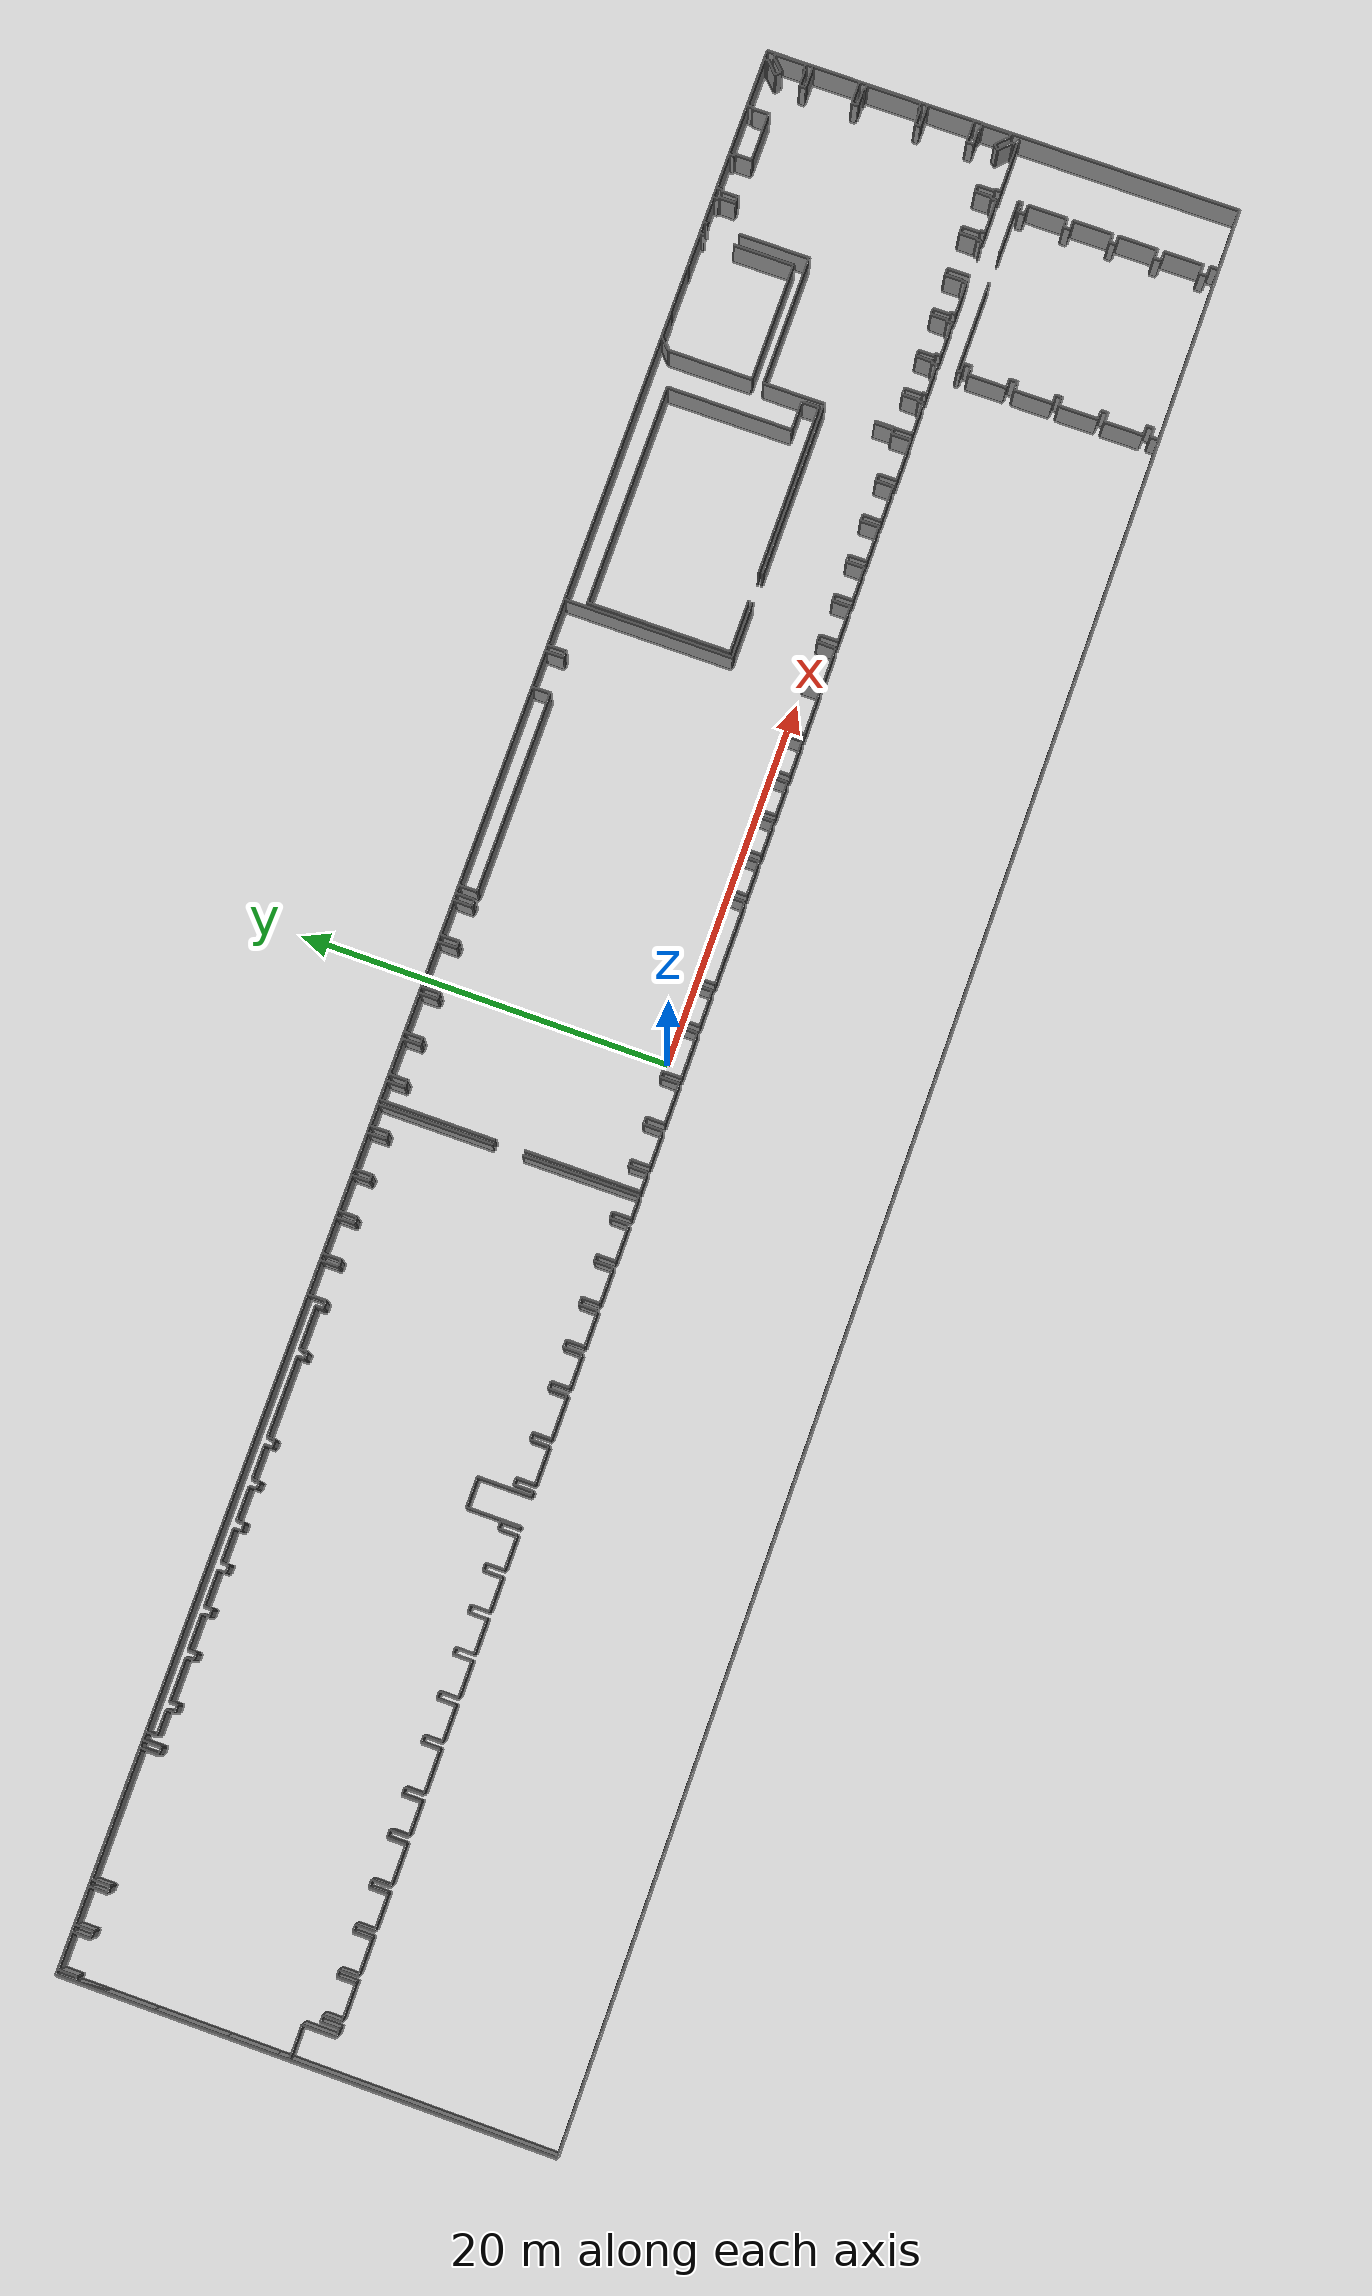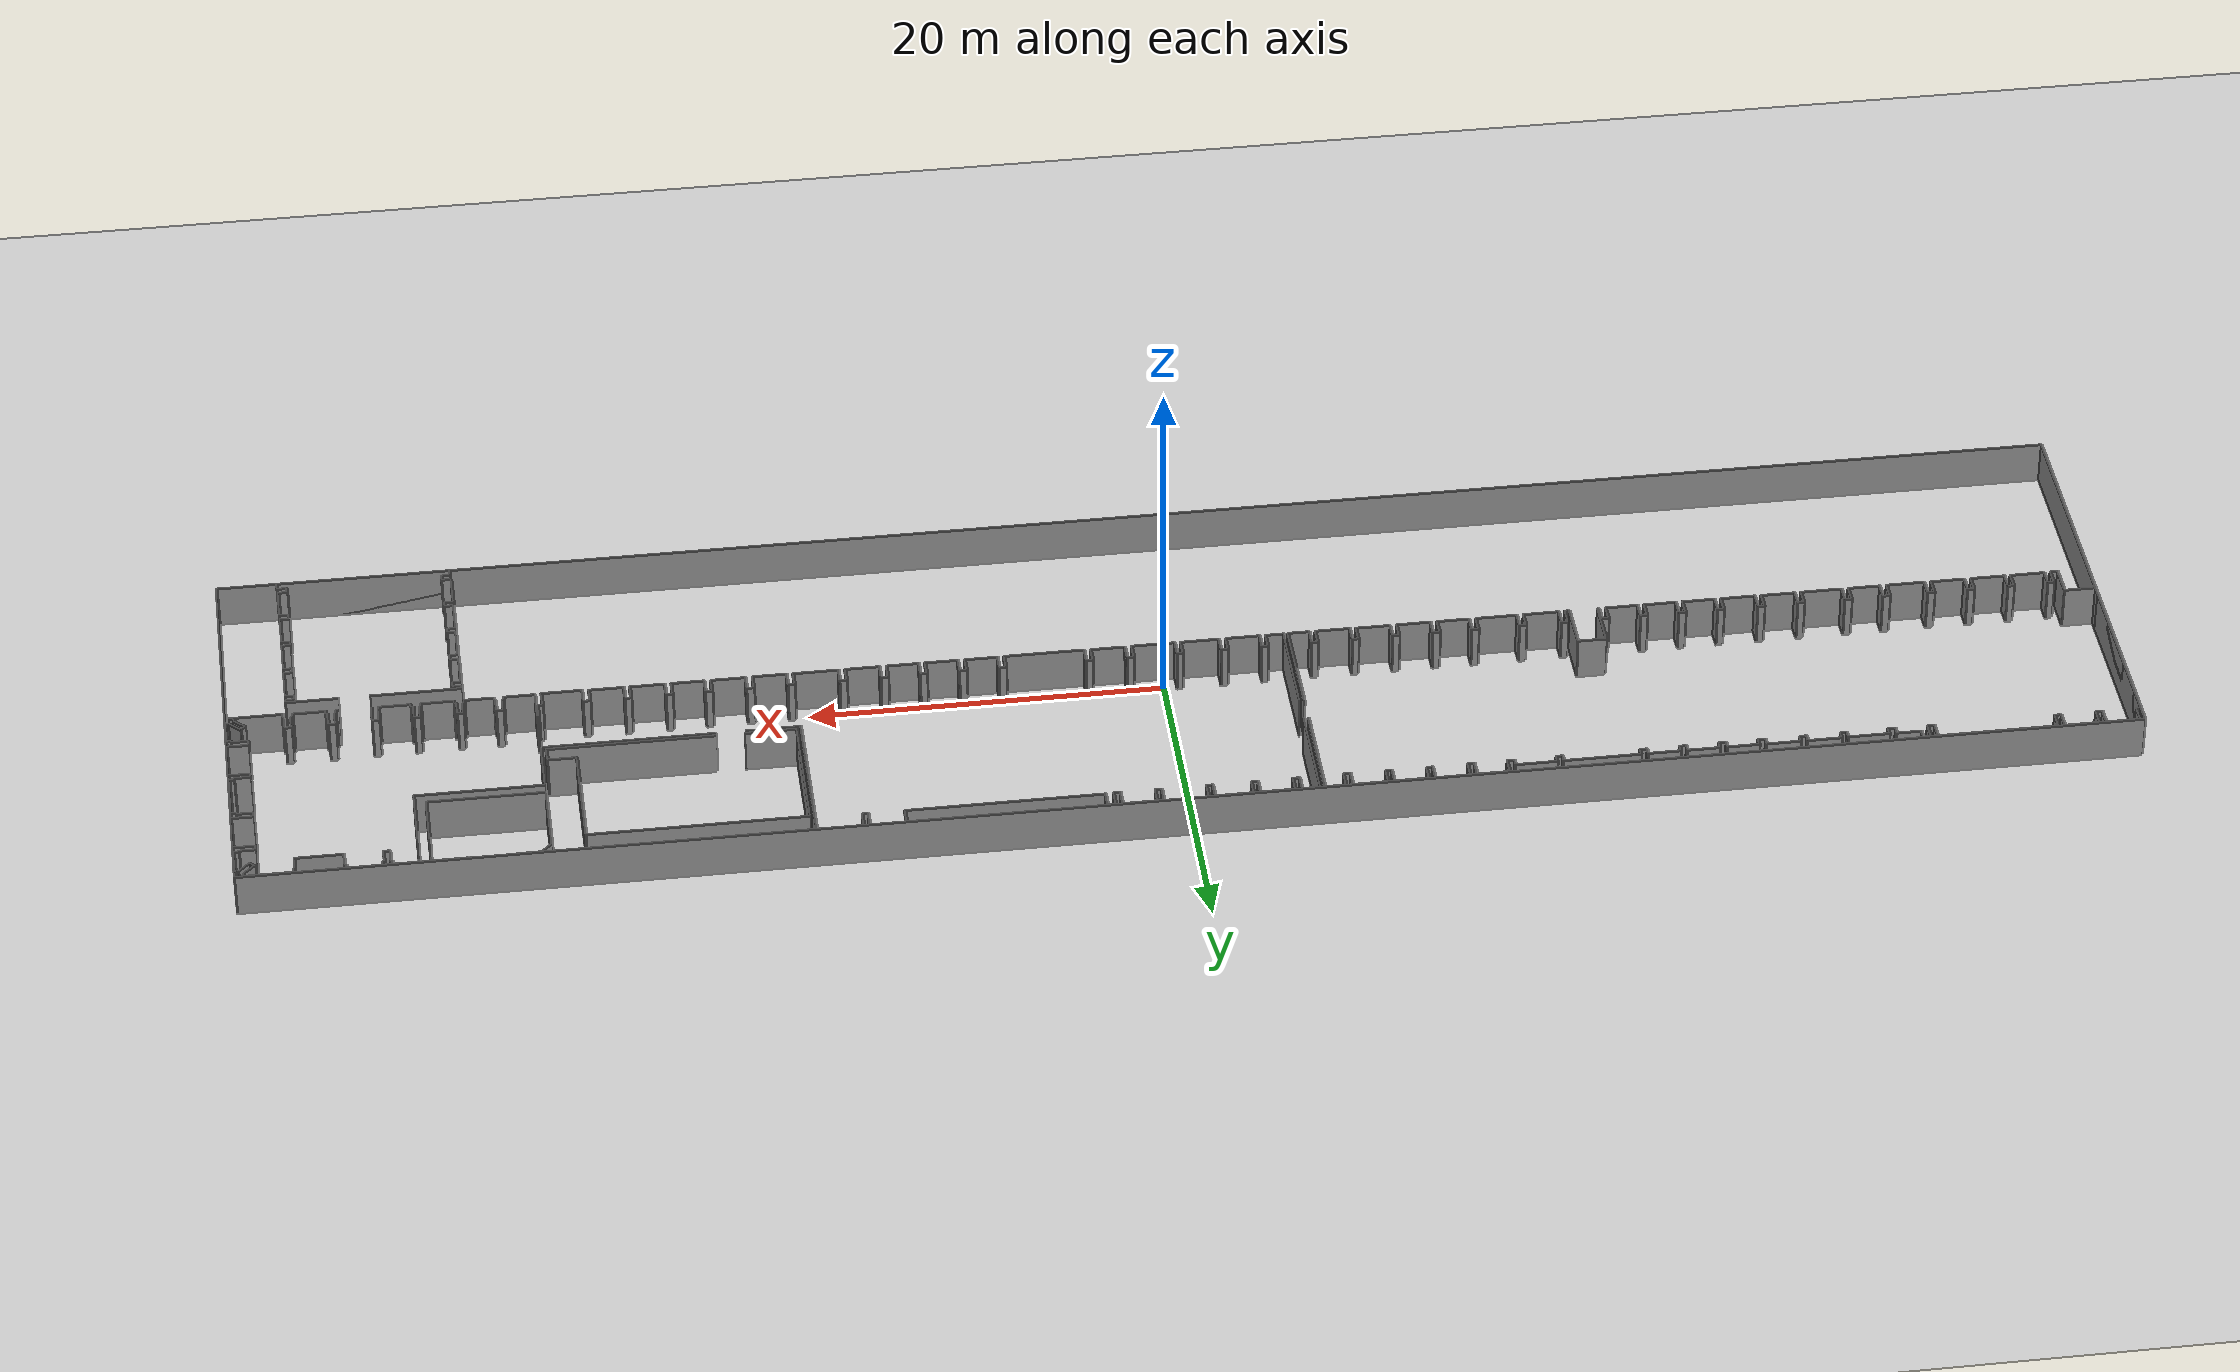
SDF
<sdf version="1.6">
  <world name="default">
    <light name="sun" type="directional">
      <cast_shadows>1</cast_shadows>
      <pose frame="">0 0 10 0 -0 0</pose>
      <diffuse>0.8 0.8 0.8 1</diffuse>
      <specular>0.1 0.1 0.1 1</specular>
      <attenuation>
        <range>1000</range>
        <constant>0.9</constant>
        <linear>0.01</linear>
        <quadratic>0.001</quadratic>
      </attenuation>
      <direction>-0.5 0.5 -1</direction>
    </light>
    <model name="ground_plane">
      <static>1</static>
      <link name="link">
        <collision name="collision">
          <geometry>
            <plane>
              <normal>0 0 1</normal>
              <size>100 100</size>
            </plane>
          </geometry>
          <surface>
            <friction>
              <ode>
                <mu>100</mu>
                <mu2>50</mu2>
              </ode>
              <torsional>
                <ode />
              </torsional>
            </friction>
            <contact>
              <ode />
            </contact>
            <bounce />
          </surface>
          <max_contacts>10</max_contacts>
        </collision>
        <visual name="visual">
          <cast_shadows>0</cast_shadows>
          <geometry>
            <plane>
              <normal>0 0 1</normal>
              <size>100 100</size>
            </plane>
          </geometry>
          <material>
            <script>
              <uri>file://media/materials/scripts/gazebo.material</uri>
              <name>Gazebo/Grey</name>
            </script>
          </material>
        </visual>
        <self_collide>0</self_collide>
        <kinematic>0</kinematic>
        <gravity>1</gravity>
      </link>
    </model>
    <gravity>0 0 -9.8</gravity>
    <magnetic_field>6e-06 2.3e-05 -4.2e-05</magnetic_field>
    <atmosphere type="adiabatic" />
    <physics default="0" name="default_physics" type="ode">
      <max_step_size>0.001</max_step_size>
      <real_time_factor>1</real_time_factor>
      <real_time_update_rate>1000</real_time_update_rate>
    </physics>
    <scene>
      <ambient>0.4 0.4 0.4 1</ambient>
      <background>0.7 0.7 0.7 1</background>
      <shadows>1</shadows>
    </scene>
    <spherical_coordinates>
      <surface_model>EARTH_WGS84</surface_model>
      <latitude_deg>0</latitude_deg>
      <longitude_deg>0</longitude_deg>
      <elevation>0</elevation>
      <heading_deg>0</heading_deg>
    </spherical_coordinates>
  <model name="50010541">
		<static>1</static>
		<link name="Wall_0">
			<collision name="Wall_0_Collision">
				<geometry>
					<box>
						<size>1.21209043708 0.1 2.5</size>
					</box>
				</geometry>
				<pose frame="">0.606045218539 0 1.25 0 0 0</pose>
			</collision>
			<visual name="Wall_0_Visual">
				<pose frame="">0.606045218539 0 1.25 0 0 0</pose>
				<geometry>
					<box>
						<size>1.21209043708 0.1 2.5</size>
					</box>
				</geometry>
				<material>
					<script>
						<uri>file://media/materials/scripts/gazebo.material</uri>
						<name>Gazebo/Grey</name>
					</script>
					<ambient>1 1 1 1</ambient>
				</material>
			</visual>
			<pose frame="">45.8285199243 -14.0414862961 0 0 0 3.14159265359</pose>
		</link>
		<link name="Wall_1">
			<collision name="Wall_1_Collision">
				<geometry>
					<box>
						<size>1.00897515646 0.1 2.5</size>
					</box>
				</geometry>
				<pose frame="">0.504487578231 0 1.25 0 0 0</pose>
			</collision>
			<visual name="Wall_1_Visual">
				<pose frame="">0.504487578231 0 1.25 0 0 0</pose>
				<geometry>
					<box>
						<size>1.00897515646 0.1 2.5</size>
					</box>
				</geometry>
				<material>
					<script>
						<uri>file://media/materials/scripts/gazebo.material</uri>
						<name>Gazebo/Grey</name>
					</script>
					<ambient>1 1 1 1</ambient>
				</material>
			</visual>
			<pose frame="">44.6164294873 -14.0414862961 0 0 0 1.57079632679</pose>
		</link>
		<link name="Wall_2">
			<collision name="Wall_2_Collision">
				<geometry>
					<box>
						<size>0.333997689564 0.1 2.5</size>
					</box>
				</geometry>
				<pose frame="">0.166998844782 0 1.25 0 0 0</pose>
			</collision>
			<visual name="Wall_2_Visual">
				<pose frame="">0.166998844782 0 1.25 0 0 0</pose>
				<geometry>
					<box>
						<size>0.333997689564 0.1 2.5</size>
					</box>
				</geometry>
				<material>
					<script>
						<uri>file://media/materials/scripts/gazebo.material</uri>
						<name>Gazebo/Grey</name>
					</script>
					<ambient>1 1 1 1</ambient>
				</material>
			</visual>
			<pose frame="">44.6164294873 -13.0325111396 0 0 0 3.14159265359</pose>
		</link>
		<link name="Wall_3">
			<collision name="Wall_3_Collision">
				<geometry>
					<box>
						<size>1.00161222754 0.1 2.5</size>
					</box>
				</geometry>
				<pose frame="">0.50080611377 0 1.25 0 0 0</pose>
			</collision>
			<visual name="Wall_3_Visual">
				<pose frame="">0.50080611377 0 1.25 0 0 0</pose>
				<geometry>
					<box>
						<size>1.00161222754 0.1 2.5</size>
					</box>
				</geometry>
				<material>
					<script>
						<uri>file://media/materials/scripts/gazebo.material</uri>
						<name>Gazebo/Grey</name>
					</script>
					<ambient>1 1 1 1</ambient>
				</material>
			</visual>
			<pose frame="">44.2824317977 -13.0325111396 0 0 0 -1.57079632679</pose>
		</link>
		<link name="Wall_4">
			<collision name="Wall_4_Collision">
				<geometry>
					<box>
						<size>1.96691759867 0.1 2.5</size>
					</box>
				</geometry>
				<pose frame="">0.983458799335 0 1.25 0 0 0</pose>
			</collision>
			<visual name="Wall_4_Visual">
				<pose frame="">0.983458799335 0 1.25 0 0 0</pose>
				<geometry>
					<box>
						<size>1.96691759867 0.1 2.5</size>
					</box>
				</geometry>
				<material>
					<script>
						<uri>file://media/materials/scripts/gazebo.material</uri>
						<name>Gazebo/Grey</name>
					</script>
					<ambient>1 1 1 1</ambient>
				</material>
			</visual>
			<pose frame="">44.2824317977 -14.0341233671 0 0 0 3.14159265359</pose>
		</link>
		<link name="Wall_5">
			<collision name="Wall_5_Collision">
				<geometry>
					<box>
						<size>1.01608419128 0.1 2.5</size>
					</box>
				</geometry>
				<pose frame="">0.508042095642 0 1.25 0 0 0</pose>
			</collision>
			<visual name="Wall_5_Visual">
				<pose frame="">0.508042095642 0 1.25 0 0 0</pose>
				<geometry>
					<box>
						<size>1.01608419128 0.1 2.5</size>
					</box>
				</geometry>
				<material>
					<script>
						<uri>file://media/materials/scripts/gazebo.material</uri>
						<name>Gazebo/Grey</name>
					</script>
					<ambient>1 1 1 1</ambient>
				</material>
			</visual>
			<pose frame="">42.315514199 -14.0341233671 0 0 0 1.57079632679</pose>
		</link>
		<link name="Wall_6">
			<collision name="Wall_6_Collision">
				<geometry>
					<box>
						<size>0.337298312874 0.1 2.5</size>
					</box>
				</geometry>
				<pose frame="">0.168649156437 0 1.25 0 0 0</pose>
			</collision>
			<visual name="Wall_6_Visual">
				<pose frame="">0.168649156437 0 1.25 0 0 0</pose>
				<geometry>
					<box>
						<size>0.337298312874 0.1 2.5</size>
					</box>
				</geometry>
				<material>
					<script>
						<uri>file://media/materials/scripts/gazebo.material</uri>
						<name>Gazebo/Grey</name>
					</script>
					<ambient>1 1 1 1</ambient>
				</material>
			</visual>
			<pose frame="">42.315514199 -13.0180391759 0 0 0 3.14159265359</pose>
		</link>
		<link name="Wall_7">
			<collision name="Wall_7_Collision">
				<geometry>
					<box>
						<size>0.991583410559 0.1 2.5</size>
					</box>
				</geometry>
				<pose frame="">0.49579170528 0 1.25 0 0 0</pose>
			</collision>
			<visual name="Wall_7_Visual">
				<pose frame="">0.49579170528 0 1.25 0 0 0</pose>
				<geometry>
					<box>
						<size>0.991583410559 0.1 2.5</size>
					</box>
				</geometry>
				<material>
					<script>
						<uri>file://media/materials/scripts/gazebo.material</uri>
						<name>Gazebo/Grey</name>
					</script>
					<ambient>1 1 1 1</ambient>
				</material>
			</visual>
			<pose frame="">41.9782158862 -13.0180391759 0 0 0 -1.57079632679</pose>
		</link>
		<link name="Wall_8">
			<collision name="Wall_8_Collision">
				<geometry>
					<box>
						<size>1.94228987089 0.1 2.5</size>
					</box>
				</geometry>
				<pose frame="">0.971144935447 0 1.25 0 0 0</pose>
			</collision>
			<visual name="Wall_8_Visual">
				<pose frame="">0.971144935447 0 1.25 0 0 0</pose>
				<geometry>
					<box>
						<size>1.94228987089 0.1 2.5</size>
					</box>
				</geometry>
				<material>
					<script>
						<uri>file://media/materials/scripts/gazebo.material</uri>
						<name>Gazebo/Grey</name>
					</script>
					<ambient>1 1 1 1</ambient>
				</material>
			</visual>
			<pose frame="">41.9782158862 -14.0096225864 0 0 0 3.14159265359</pose>
		</link>
		<link name="Wall_9">
			<collision name="Wall_9_Collision">
				<geometry>
					<box>
						<size>0.973556929405 0.1 2.5</size>
					</box>
				</geometry>
				<pose frame="">0.486778464702 0 1.25 0 0 0</pose>
			</collision>
			<visual name="Wall_9_Visual">
				<pose frame="">0.486778464702 0 1.25 0 0 0</pose>
				<geometry>
					<box>
						<size>0.973556929405 0.1 2.5</size>
					</box>
				</geometry>
				<material>
					<script>
						<uri>file://media/materials/scripts/gazebo.material</uri>
						<name>Gazebo/Grey</name>
					</script>
					<ambient>1 1 1 1</ambient>
				</material>
			</visual>
			<pose frame="">40.0359260153 -14.0096225864 0 0 0 1.57079632679</pose>
		</link>
		<link name="Wall_10">
			<collision name="Wall_10_Collision">
				<geometry>
					<box>
						<size>0.37233569878 0.1 2.5</size>
					</box>
				</geometry>
				<pose frame="">0.18616784939 0 1.25 0 0 0</pose>
			</collision>
			<visual name="Wall_10_Visual">
				<pose frame="">0.18616784939 0 1.25 0 0 0</pose>
				<geometry>
					<box>
						<size>0.37233569878 0.1 2.5</size>
					</box>
				</geometry>
				<material>
					<script>
						<uri>file://media/materials/scripts/gazebo.material</uri>
						<name>Gazebo/Grey</name>
					</script>
					<ambient>1 1 1 1</ambient>
				</material>
			</visual>
			<pose frame="">40.0359260153 -13.036065657 0 0 0 3.14159265359</pose>
		</link>
		<link name="Wall_11">
			<collision name="Wall_11_Collision">
				<geometry>
					<box>
						<size>0.983077958184 0.1 2.5</size>
					</box>
				</geometry>
				<pose frame="">0.491538979092 0 1.25 0 0 0</pose>
			</collision>
			<visual name="Wall_11_Visual">
				<pose frame="">0.491538979092 0 1.25 0 0 0</pose>
				<geometry>
					<box>
						<size>0.983077958184 0.1 2.5</size>
					</box>
				</geometry>
				<material>
					<script>
						<uri>file://media/materials/scripts/gazebo.material</uri>
						<name>Gazebo/Grey</name>
					</script>
					<ambient>1 1 1 1</ambient>
				</material>
			</visual>
			<pose frame="">39.6635903165 -13.036065657 0 0 0 -1.57079632679</pose>
		</link>
		<link name="Wall_12">
			<collision name="Wall_12_Collision">
				<geometry>
					<box>
						<size>1.91385373161 0.1 2.5</size>
					</box>
				</geometry>
				<pose frame="">0.956926865804 0 1.25 0 0 0</pose>
			</collision>
			<visual name="Wall_12_Visual">
				<pose frame="">0.956926865804 0 1.25 0 0 0</pose>
				<geometry>
					<box>
						<size>1.91385373161 0.1 2.5</size>
					</box>
				</geometry>
				<material>
					<script>
						<uri>file://media/materials/scripts/gazebo.material</uri>
						<name>Gazebo/Grey</name>
					</script>
					<ambient>1 1 1 1</ambient>
				</material>
			</visual>
			<pose frame="">39.6635903165 -14.0191436152 0 0 0 3.14159265359</pose>
		</link>
		<link name="Wall_13">
			<collision name="Wall_13_Collision">
				<geometry>
					<box>
						<size>0.991583410559 0.1 2.5</size>
					</box>
				</geometry>
				<pose frame="">0.49579170528 0 1.25 0 0 0</pose>
			</collision>
			<visual name="Wall_13_Visual">
				<pose frame="">0.49579170528 0 1.25 0 0 0</pose>
				<geometry>
					<box>
						<size>0.991583410559 0.1 2.5</size>
					</box>
				</geometry>
				<material>
					<script>
						<uri>file://media/materials/scripts/gazebo.material</uri>
						<name>Gazebo/Grey</name>
					</script>
					<ambient>1 1 1 1</ambient>
				</material>
			</visual>
			<pose frame="">37.7497365849 -14.0191436152 0 0 0 1.57079632679</pose>
		</link>
		<link name="Wall_14">
			<collision name="Wall_14_Collision">
				<geometry>
					<box>
						<size>0.381856727559 0.1 2.5</size>
					</box>
				</geometry>
				<pose frame="">0.190928363779 0 1.25 0 0 0</pose>
			</collision>
			<visual name="Wall_14_Visual">
				<pose frame="">0.190928363779 0 1.25 0 0 0</pose>
				<geometry>
					<box>
						<size>0.381856727559 0.1 2.5</size>
					</box>
				</geometry>
				<material>
					<script>
						<uri>file://media/materials/scripts/gazebo.material</uri>
						<name>Gazebo/Grey</name>
					</script>
					<ambient>1 1 1 1</ambient>
				</material>
			</visual>
			<pose frame="">37.7497365849 -13.0275602046 0 0 0 3.14159265359</pose>
		</link>
		<link name="Wall_15">
			<collision name="Wall_15_Collision">
				<geometry>
					<box>
						<size>0.99183730466 0.1 2.5</size>
					</box>
				</geometry>
				<pose frame="">0.49591865233 0 1.25 0 0 0</pose>
			</collision>
			<visual name="Wall_15_Visual">
				<pose frame="">0.49591865233 0 1.25 0 0 0</pose>
				<geometry>
					<box>
						<size>0.99183730466 0.1 2.5</size>
					</box>
				</geometry>
				<material>
					<script>
						<uri>file://media/materials/scripts/gazebo.material</uri>
						<name>Gazebo/Grey</name>
					</script>
					<ambient>1 1 1 1</ambient>
				</material>
			</visual>
			<pose frame="">37.3678798573 -13.0275602046 0 0 0 -1.57079632679</pose>
		</link>
		<link name="Wall_16">
			<collision name="Wall_16_Collision">
				<geometry>
					<box>
						<size>1.82664110799 0.1 2.5</size>
					</box>
				</geometry>
				<pose frame="">0.913320553997 0 1.25 0 0 0</pose>
			</collision>
			<visual name="Wall_16_Visual">
				<pose frame="">0.913320553997 0 1.25 0 0 0</pose>
				<geometry>
					<box>
						<size>1.82664110799 0.1 2.5</size>
					</box>
				</geometry>
				<material>
					<script>
						<uri>file://media/materials/scripts/gazebo.material</uri>
						<name>Gazebo/Grey</name>
					</script>
					<ambient>1 1 1 1</ambient>
				</material>
			</visual>
			<pose frame="">37.3678798573 -14.0193975093 0 0 0 3.14159265359</pose>
		</link>
		<link name="Wall_17">
			<collision name="Wall_17_Collision">
				<geometry>
					<box>
						<size>1.00224696279 0.1 2.5</size>
					</box>
				</geometry>
				<pose frame="">0.501123481396 0 1.25 0 0 0</pose>
			</collision>
			<visual name="Wall_17_Visual">
				<pose frame="">0.501123481396 0 1.25 0 0 0</pose>
				<geometry>
					<box>
						<size>1.00224696279 0.1 2.5</size>
					</box>
				</geometry>
				<material>
					<script>
						<uri>file://media/materials/scripts/gazebo.material</uri>
						<name>Gazebo/Grey</name>
					</script>
					<ambient>1 1 1 1</ambient>
				</material>
			</visual>
			<pose frame="">35.5412387493 -14.0193975093 0 0 0 1.57079632679</pose>
		</link>
		<link name="Wall_18">
			<collision name="Wall_18_Collision">
				<geometry>
					<box>
						<size>0.373224328133 0.1 2.5</size>
					</box>
				</geometry>
				<pose frame="">0.186612164066 0 1.25 0 0 0</pose>
			</collision>
			<visual name="Wall_18_Visual">
				<pose frame="">0.186612164066 0 1.25 0 0 0</pose>
				<geometry>
					<box>
						<size>0.373224328133 0.1 2.5</size>
					</box>
				</geometry>
				<material>
					<script>
						<uri>file://media/materials/scripts/gazebo.material</uri>
						<name>Gazebo/Grey</name>
					</script>
					<ambient>1 1 1 1</ambient>
				</material>
			</visual>
			<pose frame="">35.5412387493 -13.0171505465 0 0 0 3.14159265359</pose>
		</link>
		<link name="Wall_19">
			<collision name="Wall_19_Collision">
				<geometry>
					<box>
						<size>0.998946339482 0.1 2.5</size>
					</box>
				</geometry>
				<pose frame="">0.499473169741 0 1.25 0 0 0</pose>
			</collision>
			<visual name="Wall_19_Visual">
				<pose frame="">0.499473169741 0 1.25 0 0 0</pose>
				<geometry>
					<box>
						<size>0.998946339482 0.1 2.5</size>
					</box>
				</geometry>
				<material>
					<script>
						<uri>file://media/materials/scripts/gazebo.material</uri>
						<name>Gazebo/Grey</name>
					</script>
					<ambient>1 1 1 1</ambient>
				</material>
			</visual>
			<pose frame="">35.1680144212 -13.0171505465 0 0 0 -1.57079632679</pose>
		</link>
		<link name="Wall_20">
			<collision name="Wall_20_Collision">
				<geometry>
					<box>
						<size>2.33798382695 0.1 2.5</size>
					</box>
				</geometry>
				<pose frame="">1.16899191347 0 1.25 0 0 0</pose>
			</collision>
			<visual name="Wall_20_Visual">
				<pose frame="">1.16899191347 0 1.25 0 0 0</pose>
				<geometry>
					<box>
						<size>2.33798382695 0.1 2.5</size>
					</box>
				</geometry>
				<material>
					<script>
						<uri>file://media/materials/scripts/gazebo.material</uri>
						<name>Gazebo/Grey</name>
					</script>
					<ambient>1 1 1 1</ambient>
				</material>
			</visual>
			<pose frame="">35.1680144212 -14.016096886 0 0 0 3.14159265359</pose>
		</link>
		<link name="Wall_21">
			<collision name="Wall_21_Collision">
				<geometry>
					<box>
						<size>0.998946339482 0.1 2.5</size>
					</box>
				</geometry>
				<pose frame="">0.499473169741 0 1.25 0 0 0</pose>
			</collision>
			<visual name="Wall_21_Visual">
				<pose frame="">0.499473169741 0 1.25 0 0 0</pose>
				<geometry>
					<box>
						<size>0.998946339482 0.1 2.5</size>
					</box>
				</geometry>
				<material>
					<script>
						<uri>file://media/materials/scripts/gazebo.material</uri>
						<name>Gazebo/Grey</name>
					</script>
					<ambient>1 1 1 1</ambient>
				</material>
			</visual>
			<pose frame="">32.8300305942 -14.016096886 0 0 0 1.57079632679</pose>
		</link>
		<link name="Wall_22">
			<collision name="Wall_22_Collision">
				<geometry>
					<box>
						<size>0.373224328133 0.1 2.5</size>
					</box>
				</geometry>
				<pose frame="">0.186612164066 0 1.25 0 0 0</pose>
			</collision>
			<visual name="Wall_22_Visual">
				<pose frame="">0.186612164066 0 1.25 0 0 0</pose>
				<geometry>
					<box>
						<size>0.373224328133 0.1 2.5</size>
					</box>
				</geometry>
				<material>
					<script>
						<uri>file://media/materials/scripts/gazebo.material</uri>
						<name>Gazebo/Grey</name>
					</script>
					<ambient>1 1 1 1</ambient>
				</material>
			</visual>
			<pose frame="">32.8300305942 -13.0171505465 0 0 0 3.14159265359</pose>
		</link>
		<link name="Wall_23">
			<collision name="Wall_23_Collision">
				<geometry>
					<box>
						<size>0.998946339482 0.1 2.5</size>
					</box>
				</geometry>
				<pose frame="">0.499473169741 0 1.25 0 0 0</pose>
			</collision>
			<visual name="Wall_23_Visual">
				<pose frame="">0.499473169741 0 1.25 0 0 0</pose>
				<geometry>
					<box>
						<size>0.998946339482 0.1 2.5</size>
					</box>
				</geometry>
				<material>
					<script>
						<uri>file://media/materials/scripts/gazebo.material</uri>
						<name>Gazebo/Grey</name>
					</script>
					<ambient>1 1 1 1</ambient>
				</material>
			</visual>
			<pose frame="">32.4568062661 -13.0171505465 0 0 0 -1.57079632679</pose>
		</link>
		<link name="Wall_24">
			<collision name="Wall_24_Collision">
				<geometry>
					<box>
						<size>2.01972757163 0.1 2.5</size>
					</box>
				</geometry>
				<pose frame="">1.00986378581 0 1.25 0 0 0</pose>
			</collision>
			<visual name="Wall_24_Visual">
				<pose frame="">1.00986378581 0 1.25 0 0 0</pose>
				<geometry>
					<box>
						<size>2.01972757163 0.1 2.5</size>
					</box>
				</geometry>
				<material>
					<script>
						<uri>file://media/materials/scripts/gazebo.material</uri>
						<name>Gazebo/Grey</name>
					</script>
					<ambient>1 1 1 1</ambient>
				</material>
			</visual>
			<pose frame="">32.4568062661 -14.016096886 0 0 0 3.14159265359</pose>
		</link>
		<link name="Wall_25">
			<collision name="Wall_25_Collision">
				<geometry>
					<box>
						<size>1.00440506265 0.1 2.5</size>
					</box>
				</geometry>
				<pose frame="">0.502202531324 0 1.25 0 0 0</pose>
			</collision>
			<visual name="Wall_25_Visual">
				<pose frame="">0.502202531324 0 1.25 0 0 0</pose>
				<geometry>
					<box>
						<size>1.00440506265 0.1 2.5</size>
					</box>
				</geometry>
				<material>
					<script>
						<uri>file://media/materials/scripts/gazebo.material</uri>
						<name>Gazebo/Grey</name>
					</script>
					<ambient>1 1 1 1</ambient>
				</material>
			</visual>
			<pose frame="">30.4370786945 -14.016096886 0 0 0 1.57079632679</pose>
		</link>
		<link name="Wall_26">
			<collision name="Wall_26_Collision">
				<geometry>
					<box>
						<size>0.367638657916 0.1 2.5</size>
					</box>
				</geometry>
				<pose frame="">0.183819328958 0 1.25 0 0 0</pose>
			</collision>
			<visual name="Wall_26_Visual">
				<pose frame="">0.183819328958 0 1.25 0 0 0</pose>
				<geometry>
					<box>
						<size>0.367638657916 0.1 2.5</size>
					</box>
				</geometry>
				<material>
					<script>
						<uri>file://media/materials/scripts/gazebo.material</uri>
						<name>Gazebo/Grey</name>
					</script>
					<ambient>1 1 1 1</ambient>
				</material>
			</visual>
			<pose frame="">30.4370786945 -13.0116918233 0 0 0 3.14159265359</pose>
		</link>
		<link name="Wall_27">
			<collision name="Wall_27_Collision">
				<geometry>
					<box>
						<size>1.02078123215 0.1 2.5</size>
					</box>
				</geometry>
				<pose frame="">0.510390616074 0 1.25 0 0 0</pose>
			</collision>
			<visual name="Wall_27_Visual">
				<pose frame="">0.510390616074 0 1.25 0 0 0</pose>
				<geometry>
					<box>
						<size>1.02078123215 0.1 2.5</size>
					</box>
				</geometry>
				<material>
					<script>
						<uri>file://media/materials/scripts/gazebo.material</uri>
						<name>Gazebo/Grey</name>
					</script>
					<ambient>1 1 1 1</ambient>
				</material>
			</visual>
			<pose frame="">30.0694400366 -13.0116918233 0 0 0 -1.57079632679</pose>
		</link>
		<link name="Wall_28">
			<collision name="Wall_28_Collision">
				<geometry>
					<box>
						<size>0.241580236883 0.1 2.5</size>
					</box>
				</geometry>
				<pose frame="">0.120790118442 0 1.25 0 0 0</pose>
			</collision>
			<visual name="Wall_28_Visual">
				<pose frame="">0.120790118442 0 1.25 0 0 0</pose>
				<geometry>
					<box>
						<size>0.241580236883 0.1 2.5</size>
					</box>
				</geometry>
				<material>
					<script>
						<uri>file://media/materials/scripts/gazebo.material</uri>
						<name>Gazebo/Grey</name>
					</script>
					<ambient>1 1 1 1</ambient>
				</material>
			</visual>
			<pose frame="">30.0694400366 -14.0324730555 0 0 0 3.14159265359</pose>
		</link>
		<link name="Wall_29">
			<collision name="Wall_29_Collision">
				<geometry>
					<box>
						<size>2.85935536288 0.1 2.5</size>
					</box>
				</geometry>
				<pose frame="">1.42967768144 0 1.25 0 0 0</pose>
			</collision>
			<visual name="Wall_29_Visual">
				<pose frame="">1.42967768144 0 1.25 0 0 0</pose>
				<geometry>
					<box>
						<size>2.85935536288 0.1 2.5</size>
					</box>
				</geometry>
				<material>
					<script>
						<uri>file://media/materials/scripts/gazebo.material</uri>
						<name>Gazebo/Grey</name>
					</script>
					<ambient>1 1 1 1</ambient>
				</material>
			</visual>
			<pose frame="">29.8278597997 -14.0324730555 0 0 0 1.57079632679</pose>
		</link>
		<link name="Wall_30">
			<collision name="Wall_30_Collision">
				<geometry>
					<box>
						<size>1.60803828723 0.1 2.5</size>
					</box>
				</geometry>
				<pose frame="">0.804019143615 0 1.25 0 0 0</pose>
			</collision>
			<visual name="Wall_30_Visual">
				<pose frame="">0.804019143615 0 1.25 0 0 0</pose>
				<geometry>
					<box>
						<size>1.60803828723 0.1 2.5</size>
					</box>
				</geometry>
				<material>
					<script>
						<uri>file://media/materials/scripts/gazebo.material</uri>
						<name>Gazebo/Grey</name>
					</script>
					<ambient>1 1 1 1</ambient>
				</material>
			</visual>
			<pose frame="">29.8278597997 -11.1731176926 0 0 0 3.14159265359</pose>
		</link>
		<link name="Wall_31">
			<collision name="Wall_31_Collision">
				<geometry>
					<box>
						<size>2.84843791655 0.1 2.5</size>
					</box>
				</geometry>
				<pose frame="">1.42421895827 0 1.25 0 0 0</pose>
			</collision>
			<visual name="Wall_31_Visual">
				<pose frame="">1.42421895827 0 1.25 0 0 0</pose>
				<geometry>
					<box>
						<size>2.84843791655 0.1 2.5</size>
					</box>
				</geometry>
				<material>
					<script>
						<uri>file://media/materials/scripts/gazebo.material</uri>
						<name>Gazebo/Grey</name>
					</script>
					<ambient>1 1 1 1</ambient>
				</material>
			</visual>
			<pose frame="">28.2198215124 -11.1731176926 0 0 0 -1.57079632679</pose>
		</link>
		<link name="Wall_32">
			<collision name="Wall_32_Collision">
				<geometry>
					<box>
						<size>0.0808652710954 0.1 2.5</size>
					</box>
				</geometry>
				<pose frame="">0.0404326355477 0 1.25 0 0 0</pose>
			</collision>
			<visual name="Wall_32_Visual">
				<pose frame="">0.0404326355477 0 1.25 0 0 0</pose>
				<geometry>
					<box>
						<size>0.0808652710954 0.1 2.5</size>
					</box>
				</geometry>
				<material>
					<script>
						<uri>file://media/materials/scripts/gazebo.material</uri>
						<name>Gazebo/Grey</name>
					</script>
					<ambient>1 1 1 1</ambient>
				</material>
			</visual>
			<pose frame="">28.2198215124 -14.0215556092 0 0 0 3.14159265359</pose>
		</link>
		<link name="Wall_33">
			<collision name="Wall_33_Collision">
				<geometry>
					<box>
						<size>0.990948675308 0.1 2.5</size>
					</box>
				</geometry>
				<pose frame="">0.495474337654 0 1.25 0 0 0</pose>
			</collision>
			<visual name="Wall_33_Visual">
				<pose frame="">0.495474337654 0 1.25 0 0 0</pose>
				<geometry>
					<box>
						<size>0.990948675308 0.1 2.5</size>
					</box>
				</geometry>
				<material>
					<script>
						<uri>file://media/materials/scripts/gazebo.material</uri>
						<name>Gazebo/Grey</name>
					</script>
					<ambient>1 1 1 1</ambient>
				</material>
			</visual>
			<pose frame="">28.1389562414 -14.0215556092 0 0 0 1.57079632679</pose>
		</link>
		<link name="Wall_34">
			<collision name="Wall_34_Collision">
				<geometry>
					<box>
						<size>0.378683051299 0.1 2.5</size>
					</box>
				</geometry>
				<pose frame="">0.18934152565 0 1.25 0 0 0</pose>
			</collision>
			<visual name="Wall_34_Visual">
				<pose frame="">0.18934152565 0 1.25 0 0 0</pose>
				<geometry>
					<box>
						<size>0.378683051299 0.1 2.5</size>
					</box>
				</geometry>
				<material>
					<script>
						<uri>file://media/materials/scripts/gazebo.material</uri>
						<name>Gazebo/Grey</name>
					</script>
					<ambient>1 1 1 1</ambient>
				</material>
			</visual>
			<pose frame="">28.1389562414 -13.0306069338 0 0 0 3.14159265359</pose>
		</link>
		<link name="Wall_35">
			<collision name="Wall_35_Collision">
				<geometry>
					<box>
						<size>0.990948675308 0.1 2.5</size>
					</box>
				</geometry>
				<pose frame="">0.495474337654 0 1.25 0 0 0</pose>
			</collision>
			<visual name="Wall_35_Visual">
				<pose frame="">0.495474337654 0 1.25 0 0 0</pose>
				<geometry>
					<box>
						<size>0.990948675308 0.1 2.5</size>
					</box>
				</geometry>
				<material>
					<script>
						<uri>file://media/materials/scripts/gazebo.material</uri>
						<name>Gazebo/Grey</name>
					</script>
					<ambient>1 1 1 1</ambient>
				</material>
			</visual>
			<pose frame="">27.7602731901 -13.0306069338 0 0 0 -1.57079632679</pose>
		</link>
		<link name="Wall_36">
			<collision name="Wall_36_Collision">
				<geometry>
					<box>
						<size>1.83044951951 0.1 2.5</size>
					</box>
				</geometry>
				<pose frame="">0.915224759753 0 1.25 0 0 0</pose>
			</collision>
			<visual name="Wall_36_Visual">
				<pose frame="">0.915224759753 0 1.25 0 0 0</pose>
				<geometry>
					<box>
						<size>1.83044951951 0.1 2.5</size>
					</box>
				</geometry>
				<material>
					<script>
						<uri>file://media/materials/scripts/gazebo.material</uri>
						<name>Gazebo/Grey</name>
					</script>
					<ambient>1 1 1 1</ambient>
				</material>
			</visual>
			<pose frame="">27.7602731901 -14.0215556092 0 0 0 3.14159265359</pose>
		</link>
		<link name="Wall_37">
			<collision name="Wall_37_Collision">
				<geometry>
					<box>
						<size>1.00986378581 0.1 2.5</size>
					</box>
				</geometry>
				<pose frame="">0.504931892907 0 1.25 0 0 0</pose>
			</collision>
			<visual name="Wall_37_Visual">
				<pose frame="">0.504931892907 0 1.25 0 0 0</pose>
				<geometry>
					<box>
						<size>1.00986378581 0.1 2.5</size>
					</box>
				</geometry>
				<material>
					<script>
						<uri>file://media/materials/scripts/gazebo.material</uri>
						<name>Gazebo/Grey</name>
					</script>
					<ambient>1 1 1 1</ambient>
				</material>
			</visual>
			<pose frame="">25.9298236705 -14.0215556092 0 0 0 1.57079632679</pose>
		</link>
		<link name="Wall_38">
			<collision name="Wall_38_Collision">
				<geometry>
					<box>
						<size>0.365988346261 0.1 2.5</size>
					</box>
				</geometry>
				<pose frame="">0.18299417313 0 1.25 0 0 0</pose>
			</collision>
			<visual name="Wall_38_Visual">
				<pose frame="">0.18299417313 0 1.25 0 0 0</pose>
				<geometry>
					<box>
						<size>0.365988346261 0.1 2.5</size>
					</box>
				</geometry>
				<material>
					<script>
						<uri>file://media/materials/scripts/gazebo.material</uri>
						<name>Gazebo/Grey</name>
					</script>
					<ambient>1 1 1 1</ambient>
				</material>
			</visual>
			<pose frame="">25.9298236705 -13.0116918233 0 0 0 3.14159265359</pose>
		</link>
		<link name="Wall_39">
			<collision name="Wall_39_Collision">
				<geometry>
					<box>
						<size>1.00986378581 0.1 2.5</size>
					</box>
				</geometry>
				<pose frame="">0.504931892907 0 1.25 0 0 0</pose>
			</collision>
			<visual name="Wall_39_Visual">
				<pose frame="">0.504931892907 0 1.25 0 0 0</pose>
				<geometry>
					<box>
						<size>1.00986378581 0.1 2.5</size>
					</box>
				</geometry>
				<material>
					<script>
						<uri>file://media/materials/scripts/gazebo.material</uri>
						<name>Gazebo/Grey</name>
					</script>
					<ambient>1 1 1 1</ambient>
				</material>
			</visual>
			<pose frame="">25.5638353243 -13.0116918233 0 0 0 -1.57079632679</pose>
		</link>
		<link name="Wall_40">
			<collision name="Wall_40_Collision">
				<geometry>
					<box>
						<size>1.82410216699 0.1 2.5</size>
					</box>
				</geometry>
				<pose frame="">0.912051083493 0 1.25 0 0 0</pose>
			</collision>
			<visual name="Wall_40_Visual">
				<pose frame="">0.912051083493 0 1.25 0 0 0</pose>
				<geometry>
					<box>
						<size>1.82410216699 0.1 2.5</size>
					</box>
				</geometry>
				<material>
					<script>
						<uri>file://media/materials/scripts/gazebo.material</uri>
						<name>Gazebo/Grey</name>
					</script>
					<ambient>1 1 1 1</ambient>
				</material>
			</visual>
			<pose frame="">25.5638353243 -14.0215556092 0 0 0 3.14159265359</pose>
		</link>
		<link name="Wall_41">
			<collision name="Wall_41_Collision">
				<geometry>
					<box>
						<size>1.0035164333 0.1 2.5</size>
					</box>
				</geometry>
				<pose frame="">0.501758216648 0 1.25 0 0 0</pose>
			</collision>
			<visual name="Wall_41_Visual">
				<pose frame="">0.501758216648 0 1.25 0 0 0</pose>
				<geometry>
					<box>
						<size>1.0035164333 0.1 2.5</size>
					</box>
				</geometry>
				<material>
					<script>
						<uri>file://media/materials/scripts/gazebo.material</uri>
						<name>Gazebo/Grey</name>
					</script>
					<ambient>1 1 1 1</ambient>
				</material>
			</visual>
			<pose frame="">23.7397331573 -14.0215556092 0 0 0 1.57079632679</pose>
		</link>
		<link name="Wall_42">
			<collision name="Wall_42_Collision">
				<geometry>
					<box>
						<size>0.37233569878 0.1 2.5</size>
					</box>
				</geometry>
				<pose frame="">0.18616784939 0 1.25 0 0 0</pose>
			</collision>
			<visual name="Wall_42_Visual">
				<pose frame="">0.18616784939 0 1.25 0 0 0</pose>
				<geometry>
					<box>
						<size>0.37233569878 0.1 2.5</size>
					</box>
				</geometry>
				<material>
					<script>
						<uri>file://media/materials/scripts/gazebo.material</uri>
						<name>Gazebo/Grey</name>
					</script>
					<ambient>1 1 1 1</ambient>
				</material>
			</visual>
			<pose frame="">23.7397331573 -13.0180391759 0 0 0 3.14159265359</pose>
		</link>
		<link name="Wall_43">
			<collision name="Wall_43_Collision">
				<geometry>
					<box>
						<size>0.997169080776 0.1 2.5</size>
					</box>
				</geometry>
				<pose frame="">0.498584540388 0 1.25 0 0 0</pose>
			</collision>
			<visual name="Wall_43_Visual">
				<pose frame="">0.498584540388 0 1.25 0 0 0</pose>
				<geometry>
					<box>
						<size>0.997169080776 0.1 2.5</size>
					</box>
				</geometry>
				<material>
					<script>
						<uri>file://media/materials/scripts/gazebo.material</uri>
						<name>Gazebo/Grey</name>
					</script>
					<ambient>1 1 1 1</ambient>
				</material>
			</visual>
			<pose frame="">23.3673974585 -13.0180391759 0 0 0 -1.57079632679</pose>
		</link>
		<link name="Wall_44">
			<collision name="Wall_44_Collision">
				<geometry>
					<box>
						<size>1.84301727749 0.1 2.5</size>
					</box>
				</geometry>
				<pose frame="">0.921508638747 0 1.25 0 0 0</pose>
			</collision>
			<visual name="Wall_44_Visual">
				<pose frame="">0.921508638747 0 1.25 0 0 0</pose>
				<geometry>
					<box>
						<size>1.84301727749 0.1 2.5</size>
					</box>
				</geometry>
				<material>
					<script>
						<uri>file://media/materials/scripts/gazebo.material</uri>
						<name>Gazebo/Grey</name>
					</script>
					<ambient>1 1 1 1</ambient>
				</material>
			</visual>
			<pose frame="">23.3673974585 -14.0152082566 0 0 0 3.14159265359</pose>
		</link>
		<link name="Wall_45">
			<collision name="Wall_45_Collision">
				<geometry>
					<box>
						<size>0.984601322788 0.1 2.5</size>
					</box>
				</geometry>
				<pose frame="">0.492300661394 0 1.25 0 0 0</pose>
			</collision>
			<visual name="Wall_45_Visual">
				<pose frame="">0.492300661394 0 1.25 0 0 0</pose>
				<geometry>
					<box>
						<size>0.984601322788 0.1 2.5</size>
					</box>
				</geometry>
				<material>
					<script>
						<uri>file://media/materials/scripts/gazebo.material</uri>
						<name>Gazebo/Grey</name>
					</script>
					<ambient>1 1 1 1</ambient>
				</material>
			</visual>
			<pose frame="">21.524380181 -14.0152082566 0 0 0 1.57079632679</pose>
		</link>
		<link name="Wall_46">
			<collision name="Wall_46_Collision">
				<geometry>
					<box>
						<size>0.347073235753 0.1 2.5</size>
					</box>
				</geometry>
				<pose frame="">0.173536617877 0 1.25 0 0 0</pose>
			</collision>
			<visual name="Wall_46_Visual">
				<pose frame="">0.173536617877 0 1.25 0 0 0</pose>
				<geometry>
					<box>
						<size>0.347073235753 0.1 2.5</size>
					</box>
				</geometry>
				<material>
					<script>
						<uri>file://media/materials/scripts/gazebo.material</uri>
						<name>Gazebo/Grey</name>
					</script>
					<ambient>1 1 1 1</ambient>
				</material>
			</visual>
			<pose frame="">21.524380181 -13.0306069338 0 0 0 3.14159265359</pose>
		</link>
		<link name="Wall_47">
			<collision name="Wall_47_Collision">
				<geometry>
					<box>
						<size>0.984601322788 0.1 2.5</size>
					</box>
				</geometry>
				<pose frame="">0.492300661394 0 1.25 0 0 0</pose>
			</collision>
			<visual name="Wall_47_Visual">
				<pose frame="">0.492300661394 0 1.25 0 0 0</pose>
				<geometry>
					<box>
						<size>0.984601322788 0.1 2.5</size>
					</box>
				</geometry>
				<material>
					<script>
						<uri>file://media/materials/scripts/gazebo.material</uri>
						<name>Gazebo/Grey</name>
					</script>
					<ambient>1 1 1 1</ambient>
				</material>
			</visual>
			<pose frame="">21.1773069453 -13.0306069338 0 0 0 -1.57079632679</pose>
		</link>
		<link name="Wall_48">
			<collision name="Wall_48_Collision">
				<geometry>
					<box>
						<size>1.95815825219 0.1 2.5</size>
					</box>
				</geometry>
				<pose frame="">0.979079126097 0 1.25 0 0 0</pose>
			</collision>
			<visual name="Wall_48_Visual">
				<pose frame="">0.979079126097 0 1.25 0 0 0</pose>
				<geometry>
					<box>
						<size>1.95815825219 0.1 2.5</size>
					</box>
				</geometry>
				<material>
					<script>
						<uri>file://media/materials/scripts/gazebo.material</uri>
						<name>Gazebo/Grey</name>
					</script>
					<ambient>1 1 1 1</ambient>
				</material>
			</visual>
			<pose frame="">21.1773069453 -14.0152082566 0 0 0 3.14159265359</pose>
		</link>
		<link name="Wall_49">
			<collision name="Wall_49_Collision">
				<geometry>
					<box>
						<size>0.992472039912 0.1 2.5</size>
					</box>
				</geometry>
				<pose frame="">0.496236019956 0 1.25 0 0 0</pose>
			</collision>
			<visual name="Wall_49_Visual">
				<pose frame="">0.496236019956 0 1.25 0 0 0</pose>
				<geometry>
					<box>
						<size>0.992472039912 0.1 2.5</size>
					</box>
				</geometry>
				<material>
					<script>
						<uri>file://media/materials/scripts/gazebo.material</uri>
						<name>Gazebo/Grey</name>
					</script>
					<ambient>1 1 1 1</ambient>
				</material>
			</visual>
			<pose frame="">19.2191486931 -14.0152082566 0 0 0 1.57079632679</pose>
		</link>
		<link name="Wall_50">
			<collision name="Wall_50_Collision">
				<geometry>
					<box>
						<size>0.3623068818 0.1 2.5</size>
					</box>
				</geometry>
				<pose frame="">0.1811534409 0 1.25 0 0 0</pose>
			</collision>
			<visual name="Wall_50_Visual">
				<pose frame="">0.1811534409 0 1.25 0 0 0</pose>
				<geometry>
					<box>
						<size>0.3623068818 0.1 2.5</size>
					</box>
				</geometry>
				<material>
					<script>
						<uri>file://media/materials/scripts/gazebo.material</uri>
						<name>Gazebo/Grey</name>
					</script>
					<ambient>1 1 1 1</ambient>
				</material>
			</visual>
			<pose frame="">19.2191486931 -13.0227362167 0 0 0 3.14159265359</pose>
		</link>
		<link name="Wall_51">
			<collision name="Wall_51_Collision">
				<geometry>
					<box>
						<size>0.982316275881 0.1 2.5</size>
					</box>
				</geometry>
				<pose frame="">0.491158137941 0 1.25 0 0 0</pose>
			</collision>
			<visual name="Wall_51_Visual">
				<pose frame="">0.491158137941 0 1.25 0 0 0</pose>
				<geometry>
					<box>
						<size>0.982316275881 0.1 2.5</size>
					</box>
				</geometry>
				<material>
					<script>
						<uri>file://media/materials/scripts/gazebo.material</uri>
						<name>Gazebo/Grey</name>
					</script>
					<ambient>1 1 1 1</ambient>
				</material>
			</visual>
			<pose frame="">18.8568418113 -13.0227362167 0 0 0 -1.57079632679</pose>
		</link>
		<link name="Wall_52">
			<collision name="Wall_52_Collision">
				<geometry>
					<box>
						<size>1.9264214896 0.1 2.5</size>
					</box>
				</geometry>
				<pose frame="">0.963210744798 0 1.25 0 0 0</pose>
			</collision>
			<visual name="Wall_52_Visual">
				<pose frame="">0.963210744798 0 1.25 0 0 0</pose>
				<geometry>
					<box>
						<size>1.9264214896 0.1 2.5</size>
					</box>
				</geometry>
				<material>
					<script>
						<uri>file://media/materials/scripts/gazebo.material</uri>
						<name>Gazebo/Grey</name>
					</script>
					<ambient>1 1 1 1</ambient>
				</material>
			</visual>
			<pose frame="">18.8568418113 -14.0050524926 0 0 0 3.14159265359</pose>
		</link>
		<link name="Wall_53">
			<collision name="Wall_53_Collision">
				<geometry>
					<box>
						<size>0.965940106382 0.1 2.5</size>
					</box>
				</geometry>
				<pose frame="">0.482970053191 0 1.25 0 0 0</pose>
			</collision>
			<visual name="Wall_53_Visual">
				<pose frame="">0.482970053191 0 1.25 0 0 0</pose>
				<geometry>
					<box>
						<size>0.965940106382 0.1 2.5</size>
					</box>
				</geometry>
				<material>
					<script>
						<uri>file://media/materials/scripts/gazebo.material</uri>
						<name>Gazebo/Grey</name>
					</script>
					<ambient>1 1 1 1</ambient>
				</material>
			</visual>
			<pose frame="">16.9304203217 -14.0050524926 0 0 0 1.57079632679</pose>
		</link>
		<link name="Wall_54">
			<collision name="Wall_54_Collision">
				<geometry>
					<box>
						<size>0.356721211583 0.1 2.5</size>
					</box>
				</geometry>
				<pose frame="">0.178360605791 0 1.25 0 0 0</pose>
			</collision>
			<visual name="Wall_54_Visual">
				<pose frame="">0.178360605791 0 1.25 0 0 0</pose>
				<geometry>
					<box>
						<size>0.356721211583 0.1 2.5</size>
					</box>
				</geometry>
				<material>
					<script>
						<uri>file://media/materials/scripts/gazebo.material</uri>
						<name>Gazebo/Grey</name>
					</script>
					<ambient>1 1 1 1</ambient>
				</material>
			</visual>
			<pose frame="">16.9304203217 -13.0391123862 0 0 0 3.14159265359</pose>
		</link>
		<link name="Wall_55">
			<collision name="Wall_55_Collision">
				<geometry>
					<box>
						<size>0.971525776599 0.1 2.5</size>
					</box>
				</geometry>
				<pose frame="">0.485762888299 0 1.25 0 0 0</pose>
			</collision>
			<visual name="Wall_55_Visual">
				<pose frame="">0.485762888299 0 1.25 0 0 0</pose>
				<geometry>
					<box>
						<size>0.971525776599 0.1 2.5</size>
					</box>
				</geometry>
				<material>
					<script>
						<uri>file://media/materials/scripts/gazebo.material</uri>
						<name>Gazebo/Grey</name>
					</script>
					<ambient>1 1 1 1</ambient>
				</material>
			</visual>
			<pose frame="">16.5736991101 -13.0391123862 0 0 0 -1.57079632679</pose>
		</link>
		<link name="Wall_56">
			<collision name="Wall_56_Collision">
				<geometry>
					<box>
						<size>2.33798382695 0.1 2.5</size>
					</box>
				</geometry>
				<pose frame="">1.16899191347 0 1.25 0 0 0</pose>
			</collision>
			<visual name="Wall_56_Visual">
				<pose frame="">1.16899191347 0 1.25 0 0 0</pose>
				<geometry>
					<box>
						<size>2.33798382695 0.1 2.5</size>
					</box>
				</geometry>
				<material>
					<script>
						<uri>file://media/materials/scripts/gazebo.material</uri>
						<name>Gazebo/Grey</name>
					</script>
					<ambient>1 1 1 1</ambient>
				</material>
			</visual>
			<pose frame="">16.5736991101 -14.0106381628 0 0 0 3.14159265359</pose>
		</link>
		<link name="Wall_57">
			<collision name="Wall_57_Collision">
				<geometry>
					<box>
						<size>0.993487616315 0.1 2.5</size>
					</box>
				</geometry>
				<pose frame="">0.496743808158 0 1.25 0 0 0</pose>
			</collision>
			<visual name="Wall_57_Visual">
				<pose frame="">0.496743808158 0 1.25 0 0 0</pose>
				<geometry>
					<box>
						<size>0.993487616315 0.1 2.5</size>
					</box>
				</geometry>
				<material>
					<script>
						<uri>file://media/materials/scripts/gazebo.material</uri>
						<name>Gazebo/Grey</name>
					</script>
					<ambient>1 1 1 1</ambient>
				</material>
			</visual>
			<pose frame="">14.2357152832 -14.0106381628 0 0 0 1.57079632679</pose>
		</link>
		<link name="Wall_58">
			<collision name="Wall_58_Collision">
				<geometry>
					<box>
						<size>0.378683051299 0.1 2.5</size>
					</box>
				</geometry>
				<pose frame="">0.18934152565 0 1.25 0 0 0</pose>
			</collision>
			<visual name="Wall_58_Visual">
				<pose frame="">0.18934152565 0 1.25 0 0 0</pose>
				<geometry>
					<box>
						<size>0.378683051299 0.1 2.5</size>
					</box>
				</geometry>
				<material>
					<script>
						<uri>file://media/materials/scripts/gazebo.material</uri>
						<name>Gazebo/Grey</name>
					</script>
					<ambient>1 1 1 1</ambient>
				</material>
			</visual>
			<pose frame="">14.2357152832 -13.0171505465 0 0 0 3.14159265359</pose>
		</link>
		<link name="Wall_59">
			<collision name="Wall_59_Collision">
				<geometry>
					<box>
						<size>0.993487616315 0.1 2.5</size>
					</box>
				</geometry>
				<pose frame="">0.496743808158 0 1.25 0 0 0</pose>
			</collision>
			<visual name="Wall_59_Visual">
				<pose frame="">0.496743808158 0 1.25 0 0 0</pose>
				<geometry>
					<box>
						<size>0.993487616315 0.1 2.5</size>
					</box>
				</geometry>
				<material>
					<script>
						<uri>file://media/materials/scripts/gazebo.material</uri>
						<name>Gazebo/Grey</name>
					</script>
					<ambient>1 1 1 1</ambient>
				</material>
			</visual>
			<pose frame="">13.8570322319 -13.0171505465 0 0 0 -1.57079632679</pose>
		</link>
		<link name="Wall_60">
			<collision name="Wall_60_Collision">
				<geometry>
					<box>
						<size>1.80556789763 0.1 2.5</size>
					</box>
				</geometry>
				<pose frame="">0.902783948815 0 1.25 0 0 0</pose>
			</collision>
			<visual name="Wall_60_Visual">
				<pose frame="">0.902783948815 0 1.25 0 0 0</pose>
				<geometry>
					<box>
						<size>1.80556789763 0.1 2.5</size>
					</box>
				</geometry>
				<material>
					<script>
						<uri>file://media/materials/scripts/gazebo.material</uri>
						<name>Gazebo/Grey</name>
					</script>
					<ambient>1 1 1 1</ambient>
				</material>
			</visual>
			<pose frame="">13.8570322319 -14.0106381628 0 0 0 3.14159265359</pose>
		</link>
		<link name="Wall_61">
			<collision name="Wall_61_Collision">
				<geometry>
					<box>
						<size>0.976984499765 0.1 2.5</size>
					</box>
				</geometry>
				<pose frame="">0.488492249883 0 1.25 0 0 0</pose>
			</collision>
			<visual name="Wall_61_Visual">
				<pose frame="">0.488492249883 0 1.25 0 0 0</pose>
				<geometry>
					<box>
						<size>0.976984499765 0.1 2.5</size>
					</box>
				</geometry>
				<material>
					<script>
						<uri>file://media/materials/scripts/gazebo.material</uri>
						<name>Gazebo/Grey</name>
					</script>
					<ambient>1 1 1 1</ambient>
				</material>
			</visual>
			<pose frame="">12.0514643342 -14.0106381628 0 0 0 1.57079632679</pose>
		</link>
		<link name="Wall_62">
			<collision name="Wall_62_Collision">
				<geometry>
					<box>
						<size>0.395186167849 0.1 2.5</size>
					</box>
				</geometry>
				<pose frame="">0.197593083925 0 1.25 0 0 0</pose>
			</collision>
			<visual name="Wall_62_Visual">
				<pose frame="">0.197593083925 0 1.25 0 0 0</pose>
				<geometry>
					<box>
						<size>0.395186167849 0.1 2.5</size>
					</box>
				</geometry>
				<material>
					<script>
						<uri>file://media/materials/scripts/gazebo.material</uri>
						<name>Gazebo/Grey</name>
					</script>
					<ambient>1 1 1 1</ambient>
				</material>
			</visual>
			<pose frame="">12.0514643342 -13.0336536631 0 0 0 3.14159265359</pose>
		</link>
		<link name="Wall_63">
			<collision name="Wall_63_Collision">
				<geometry>
					<box>
						<size>0.987901946098 0.1 2.5</size>
					</box>
				</geometry>
				<pose frame="">0.493950973049 0 1.25 0 0 0</pose>
			</collision>
			<visual name="Wall_63_Visual">
				<pose frame="">0.493950973049 0 1.25 0 0 0</pose>
				<geometry>
					<box>
						<size>0.987901946098 0.1 2.5</size>
					</box>
				</geometry>
				<material>
					<script>
						<uri>file://media/materials/scripts/gazebo.material</uri>
						<name>Gazebo/Grey</name>
					</script>
					<ambient>1 1 1 1</ambient>
				</material>
			</visual>
			<pose frame="">11.6562781664 -13.0336536631 0 0 0 -1.57079632679</pose>
		</link>
		<link name="Wall_64">
			<collision name="Wall_64_Collision">
				<geometry>
					<box>
						<size>2.17891917281 0.1 2.5</size>
					</box>
				</geometry>
				<pose frame="">1.08945958641 0 1.25 0 0 0</pose>
			</collision>
			<visual name="Wall_64_Visual">
				<pose frame="">1.08945958641 0 1.25 0 0 0</pose>
				<geometry>
					<box>
						<size>2.17891917281 0.1 2.5</size>
					</box>
				</geometry>
				<material>
					<script>
						<uri>file://media/materials/scripts/gazebo.material</uri>
						<name>Gazebo/Grey</name>
					</script>
					<ambient>1 1 1 1</ambient>
				</material>
			</visual>
			<pose frame="">11.6562781664 -14.0215556092 0 0 0 3.14159265359</pose>
		</link>
		<link name="Wall_65">
			<collision name="Wall_65_Collision">
				<geometry>
					<box>
						<size>0.993360669265 0.1 2.5</size>
					</box>
				</geometry>
				<pose frame="">0.496680334632 0 1.25 0 0 0</pose>
			</collision>
			<visual name="Wall_65_Visual">
				<pose frame="">0.496680334632 0 1.25 0 0 0</pose>
				<geometry>
					<box>
						<size>0.993360669265 0.1 2.5</size>
					</box>
				</geometry>
				<material>
					<script>
						<uri>file://media/materials/scripts/gazebo.material</uri>
						<name>Gazebo/Grey</name>
					</script>
					<ambient>1 1 1 1</ambient>
				</material>
			</visual>
			<pose frame="">9.47735899356 -14.0215556092 0 0 0 1.57079632679</pose>
		</link>
		<link name="Wall_66">
			<collision name="Wall_66_Collision">
				<geometry>
					<box>
						<size>0.384141774466 0.1 2.5</size>
					</box>
				</geometry>
				<pose frame="">0.192070887233 0 1.25 0 0 0</pose>
			</collision>
			<visual name="Wall_66_Visual">
				<pose frame="">0.192070887233 0 1.25 0 0 0</pose>
				<geometry>
					<box>
						<size>0.384141774466 0.1 2.5</size>
					</box>
				</geometry>
				<material>
					<script>
						<uri>file://media/materials/scripts/gazebo.material</uri>
						<name>Gazebo/Grey</name>
					</script>
					<ambient>1 1 1 1</ambient>
				</material>
			</visual>
			<pose frame="">9.47735899356 -13.0281949399 0 0 0 3.14159265359</pose>
		</link>
		<link name="Wall_67">
			<collision name="Wall_67_Collision">
				<geometry>
					<box>
						<size>0.982443222932 0.1 2.5</size>
					</box>
				</geometry>
				<pose frame="">0.491221611466 0 1.25 0 0 0</pose>
			</collision>
			<visual name="Wall_67_Visual">
				<pose frame="">0.491221611466 0 1.25 0 0 0</pose>
				<geometry>
					<box>
						<size>0.982443222932 0.1 2.5</size>
					</box>
				</geometry>
				<material>
					<script>
						<uri>file://media/materials/scripts/gazebo.material</uri>
						<name>Gazebo/Grey</name>
					</script>
					<ambient>1 1 1 1</ambient>
				</material>
			</visual>
			<pose frame="">9.0932172191 -13.0281949399 0 0 0 -1.57079632679</pose>
		</link>
		<link name="Wall_68">
			<collision name="Wall_68_Collision">
				<geometry>
					<box>
						<size>1.91537709621 0.1 2.5</size>
					</box>
				</geometry>
				<pose frame="">0.957688548107 0 1.25 0 0 0</pose>
			</collision>
			<visual name="Wall_68_Visual">
				<pose frame="">0.957688548107 0 1.25 0 0 0</pose>
				<geometry>
					<box>
						<size>1.91537709621 0.1 2.5</size>
					</box>
				</geometry>
				<material>
					<script>
						<uri>file://media/materials/scripts/gazebo.material</uri>
						<name>Gazebo/Grey</name>
					</script>
					<ambient>1 1 1 1</ambient>
				</material>
			</visual>
			<pose frame="">9.0932172191 -14.0106381628 0 0 0 3.14159265359</pose>
		</link>
		<link name="Wall_69">
			<collision name="Wall_69_Collision">
				<geometry>
					<box>
						<size>0.987901946098 0.1 2.5</size>
					</box>
				</geometry>
				<pose frame="">0.493950973049 0 1.25 0 0 0</pose>
			</collision>
			<visual name="Wall_69_Visual">
				<pose frame="">0.493950973049 0 1.25 0 0 0</pose>
				<geometry>
					<box>
						<size>0.987901946098 0.1 2.5</size>
					</box>
				</geometry>
				<material>
					<script>
						<uri>file://media/materials/scripts/gazebo.material</uri>
						<name>Gazebo/Grey</name>
					</script>
					<ambient>1 1 1 1</ambient>
				</material>
			</visual>
			<pose frame="">7.17784012288 -14.0106381628 0 0 0 1.57079632679</pose>
		</link>
		<link name="Wall_70">
			<collision name="Wall_70_Collision">
				<geometry>
					<box>
						<size>0.367765604966 0.1 2.5</size>
					</box>
				</geometry>
				<pose frame="">0.183882802483 0 1.25 0 0 0</pose>
			</collision>
			<visual name="Wall_70_Visual">
				<pose frame="">0.183882802483 0 1.25 0 0 0</pose>
				<geometry>
					<box>
						<size>0.367765604966 0.1 2.5</size>
					</box>
				</geometry>
				<material>
					<script>
						<uri>file://media/materials/scripts/gazebo.material</uri>
						<name>Gazebo/Grey</name>
					</script>
					<ambient>1 1 1 1</ambient>
				</material>
			</visual>
			<pose frame="">7.17784012288 -13.0227362167 0 0 0 3.14159265359</pose>
		</link>
		<link name="Wall_71">
			<collision name="Wall_71_Collision">
				<geometry>
					<box>
						<size>0.982316275881 0.1 2.5</size>
					</box>
				</geometry>
				<pose frame="">0.491158137941 0 1.25 0 0 0</pose>
			</collision>
			<visual name="Wall_71_Visual">
				<pose frame="">0.491158137941 0 1.25 0 0 0</pose>
				<geometry>
					<box>
						<size>0.982316275881 0.1 2.5</size>
					</box>
				</geometry>
				<material>
					<script>
						<uri>file://media/materials/scripts/gazebo.material</uri>
						<name>Gazebo/Grey</name>
					</script>
					<ambient>1 1 1 1</ambient>
				</material>
			</visual>
			<pose frame="">6.81007451792 -13.0227362167 0 0 0 -1.57079632679</pose>
		</link>
		<link name="Wall_72">
			<collision name="Wall_72_Collision">
				<geometry>
					<box>
						<size>1.95384205248 0.1 2.5</size>
					</box>
				</geometry>
				<pose frame="">0.97692102624 0 1.25 0 0 0</pose>
			</collision>
			<visual name="Wall_72_Visual">
				<pose frame="">0.97692102624 0 1.25 0 0 0</pose>
				<geometry>
					<box>
						<size>1.95384205248 0.1 2.5</size>
					</box>
				</geometry>
				<material>
					<script>
						<uri>file://media/materials/scripts/gazebo.material</uri>
						<name>Gazebo/Grey</name>
					</script>
					<ambient>1 1 1 1</ambient>
				</material>
			</visual>
			<pose frame="">6.81007451792 -14.0050524926 0 0 0 3.14159265359</pose>
		</link>
		<link name="Wall_73">
			<collision name="Wall_73_Collision">
				<geometry>
					<box>
						<size>0.982316275881 0.1 2.5</size>
					</box>
				</geometry>
				<pose frame="">0.491158137941 0 1.25 0 0 0</pose>
			</collision>
			<visual name="Wall_73_Visual">
				<pose frame="">0.491158137941 0 1.25 0 0 0</pose>
				<geometry>
					<box>
						<size>0.982316275881 0.1 2.5</size>
					</box>
				</geometry>
				<material>
					<script>
						<uri>file://media/materials/scripts/gazebo.material</uri>
						<name>Gazebo/Grey</name>
					</script>
					<ambient>1 1 1 1</ambient>
				</material>
			</visual>
			<pose frame="">4.85623246544 -14.0050524926 0 0 0 1.57079632679</pose>
		</link>
		<link name="Wall_74">
			<collision name="Wall_74_Collision">
				<geometry>
					<box>
						<size>0.334759371866 0.1 2.5</size>
					</box>
				</geometry>
				<pose frame="">0.167379685933 0 1.25 0 0 0</pose>
			</collision>
			<visual name="Wall_74_Visual">
				<pose frame="">0.167379685933 0 1.25 0 0 0</pose>
				<geometry>
					<box>
						<size>0.334759371866 0.1 2.5</size>
					</box>
				</geometry>
				<material>
					<script>
						<uri>file://media/materials/scripts/gazebo.material</uri>
						<name>Gazebo/Grey</name>
					</script>
					<ambient>1 1 1 1</ambient>
				</material>
			</visual>
			<pose frame="">4.85623246544 -13.0227362167 0 0 0 3.14159265359</pose>
		</link>
		<link name="Wall_75">
			<collision name="Wall_75_Collision">
				<geometry>
					<box>
						<size>0.982316275881 0.1 2.5</size>
					</box>
				</geometry>
				<pose frame="">0.491158137941 0 1.25 0 0 0</pose>
			</collision>
			<visual name="Wall_75_Visual">
				<pose frame="">0.491158137941 0 1.25 0 0 0</pose>
				<geometry>
					<box>
						<size>0.982316275881 0.1 2.5</size>
					</box>
				</geometry>
				<material>
					<script>
						<uri>file://media/materials/scripts/gazebo.material</uri>
						<name>Gazebo/Grey</name>
					</script>
					<ambient>1 1 1 1</ambient>
				</material>
			</visual>
			<pose frame="">4.52147309357 -13.0227362167 0 0 0 -1.57079632679</pose>
		</link>
		<link name="Wall_76">
			<collision name="Wall_76_Collision">
				<geometry>
					<box>
						<size>1.97021822198 0.1 2.5</size>
					</box>
				</geometry>
				<pose frame="">0.98510911099 0 1.25 0 0 0</pose>
			</collision>
			<visual name="Wall_76_Visual">
				<pose frame="">0.98510911099 0 1.25 0 0 0</pose>
				<geometry>
					<box>
						<size>1.97021822198 0.1 2.5</size>
					</box>
				</geometry>
				<material>
					<script>
						<uri>file://media/materials/scripts/gazebo.material</uri>
						<name>Gazebo/Grey</name>
					</script>
					<ambient>1 1 1 1</ambient>
				</material>
			</visual>
			<pose frame="">4.52147309357 -14.0050524926 0 0 0 3.14159265359</pose>
		</link>
		<link name="Wall_77">
			<collision name="Wall_77_Collision">
				<geometry>
					<box>
						<size>0.976857552715 0.1 2.5</size>
					</box>
				</geometry>
				<pose frame="">0.488428776357 0 1.25 0 0 0</pose>
			</collision>
			<visual name="Wall_77_Visual">
				<pose frame="">0.488428776357 0 1.25 0 0 0</pose>
				<geometry>
					<box>
						<size>0.976857552715 0.1 2.5</size>
					</box>
				</geometry>
				<material>
					<script>
						<uri>file://media/materials/scripts/gazebo.material</uri>
						<name>Gazebo/Grey</name>
					</script>
					<ambient>1 1 1 1</ambient>
				</material>
			</visual>
			<pose frame="">2.55125487159 -14.0050524926 0 0 0 1.57079632679</pose>
		</link>
		<link name="Wall_78">
			<collision name="Wall_78_Collision">
				<geometry>
					<box>
						<size>0.34580376525 0.1 2.5</size>
					</box>
				</geometry>
				<pose frame="">0.172901882625 0 1.25 0 0 0</pose>
			</collision>
			<visual name="Wall_78_Visual">
				<pose frame="">0.172901882625 0 1.25 0 0 0</pose>
				<geometry>
					<box>
						<size>0.34580376525 0.1 2.5</size>
					</box>
				</geometry>
				<material>
					<script>
						<uri>file://media/materials/scripts/gazebo.material</uri>
						<name>Gazebo/Grey</name>
					</script>
					<ambient>1 1 1 1</ambient>
				</material>
			</visual>
			<pose frame="">2.55125487159 -13.0281949399 0 0 0 3.14159265359</pose>
		</link>
		<link name="Wall_79">
			<collision name="Wall_79_Collision">
				<geometry>
					<box>
						<size>0.987901946098 0.1 2.5</size>
					</box>
				</geometry>
				<pose frame="">0.493950973049 0 1.25 0 0 0</pose>
			</collision>
			<visual name="Wall_79_Visual">
				<pose frame="">0.493950973049 0 1.25 0 0 0</pose>
				<geometry>
					<box>
						<size>0.987901946098 0.1 2.5</size>
					</box>
				</geometry>
				<material>
					<script>
						<uri>file://media/materials/scripts/gazebo.material</uri>
						<name>Gazebo/Grey</name>
					</script>
					<ambient>1 1 1 1</ambient>
				</material>
			</visual>
			<pose frame="">2.20545110634 -13.0281949399 0 0 0 -1.57079632679</pose>
		</link>
		<link name="Wall_80">
			<collision name="Wall_80_Collision">
				<geometry>
					<box>
						<size>0.422606730733 0.1 2.5</size>
					</box>
				</geometry>
				<pose frame="">0.211303365366 0 1.25 0 0 0</pose>
			</collision>
			<visual name="Wall_80_Visual">
				<pose frame="">0.211303365366 0 1.25 0 0 0</pose>
				<geometry>
					<box>
						<size>0.422606730733 0.1 2.5</size>
					</box>
				</geometry>
				<material>
					<script>
						<uri>file://media/materials/scripts/gazebo.material</uri>
						<name>Gazebo/Grey</name>
					</script>
					<ambient>1 1 1 1</ambient>
				</material>
			</visual>
			<pose frame="">2.20545110634 -14.016096886 0 0 0 3.14159265359</pose>
		</link>
		<link name="Wall_81">
			<collision name="Wall_81_Collision">
				<geometry>
					<box>
						<size>1.7956660277 0.1 2.5</size>
					</box>
				</geometry>
				<pose frame="">0.89783301385 0 1.25 0 0 0</pose>
			</collision>
			<visual name="Wall_81_Visual">
				<pose frame="">0.89783301385 0 1.25 0 0 0</pose>
				<geometry>
					<box>
						<size>1.7956660277 0.1 2.5</size>
					</box>
				</geometry>
				<material>
					<script>
						<uri>file://media/materials/scripts/gazebo.material</uri>
						<name>Gazebo/Grey</name>
					</script>
					<ambient>1 1 1 1</ambient>
				</material>
			</visual>
			<pose frame="">1.78284437561 -14.016096886 0 0 0 1.57079632679</pose>
		</link>
		<link name="Wall_82">
			<collision name="Wall_82_Collision">
				<geometry>
					<box>
						<size>1.78284437561 0.1 2.5</size>
					</box>
				</geometry>
				<pose frame="">0.891422187805 0 1.25 0 0 0</pose>
			</collision>
			<visual name="Wall_82_Visual">
				<pose frame="">0.891422187805 0 1.25 0 0 0</pose>
				<geometry>
					<box>
						<size>1.78284437561 0.1 2.5</size>
					</box>
				</geometry>
				<material>
					<script>
						<uri>file://media/materials/scripts/gazebo.material</uri>
						<name>Gazebo/Grey</name>
					</script>
					<ambient>1 1 1 1</ambient>
				</material>
			</visual>
			<pose frame="">1.78284437561 -12.2204308583 0 0 0 3.14159265359</pose>
		</link>
		<link name="Wall_83">
			<collision name="Wall_83_Collision">
				<geometry>
					<box>
						<size>0.639559239841 0.1 2.5</size>
					</box>
				</geometry>
				<pose frame="">0.319779619921 0 1.25 0 0 0</pose>
			</collision>
			<visual name="Wall_83_Visual">
				<pose frame="">0.319779619921 0 1.25 0 0 0</pose>
				<geometry>
					<box>
						<size>0.639559239841 0.1 2.5</size>
					</box>
				</geometry>
				<material>
					<script>
						<uri>file://media/materials/scripts/gazebo.material</uri>
						<name>Gazebo/Grey</name>
					</script>
					<ambient>1 1 1 1</ambient>
				</material>
			</visual>
			<pose frame="">0.0 -12.2204308583 0 0 0 1.57079632679</pose>
		</link>
		<link name="Wall_84">
			<collision name="Wall_84_Collision">
				<geometry>
					<box>
						<size>3.81539359933 0.1 2.5</size>
					</box>
				</geometry>
				<pose frame="">1.90769679966 0 1.25 0 0 0</pose>
			</collision>
			<visual name="Wall_84_Visual">
				<pose frame="">1.90769679966 0 1.25 0 0 0</pose>
				<geometry>
					<box>
						<size>3.81539359933 0.1 2.5</size>
					</box>
				</geometry>
				<material>
					<script>
						<uri>file://media/materials/scripts/gazebo.material</uri>
						<name>Gazebo/Grey</name>
					</script>
					<ambient>1 1 1 1</ambient>
				</material>
			</visual>
			<pose frame="">0.0 -8.96690490396 0 0 0 1.57079632679</pose>
		</link>
		<link name="Wall_85">
			<collision name="Wall_85_Collision">
				<geometry>
					<box>
						<size>1.55459357902 0.1 2.5</size>
					</box>
				</geometry>
				<pose frame="">0.777296789509 0 1.25 0 0 0</pose>
			</collision>
			<visual name="Wall_85_Visual">
				<pose frame="">0.777296789509 0 1.25 0 0 0</pose>
				<geometry>
					<box>
						<size>1.55459357902 0.1 2.5</size>
					</box>
				</geometry>
				<material>
					<script>
						<uri>file://media/materials/scripts/gazebo.material</uri>
						<name>Gazebo/Grey</name>
					</script>
					<ambient>1 1 1 1</ambient>
				</material>
			</visual>
			<pose frame="">0.0 -2.57854848743 0 0 0 1.57079632679</pose>
		</link>
		<link name="Wall_86">
			<collision name="Wall_86_Collision">
				<geometry>
					<box>
						<size>0.253005471418 0.1 2.5</size>
					</box>
				</geometry>
				<pose frame="">0.126502735709 0 1.25 0 0 0</pose>
			</collision>
			<visual name="Wall_86_Visual">
				<pose frame="">0.126502735709 0 1.25 0 0 0</pose>
				<geometry>
					<box>
						<size>0.253005471418 0.1 2.5</size>
					</box>
				</geometry>
				<material>
					<script>
						<uri>file://media/materials/scripts/gazebo.material</uri>
						<name>Gazebo/Grey</name>
					</script>
					<ambient>1 1 1 1</ambient>
				</material>
			</visual>
			<pose frame="">0.0 -1.02395490841 0 0 0 0.0</pose>
		</link>
		<link name="Wall_87">
			<collision name="Wall_87_Collision">
				<geometry>
					<box>
						<size>0.992725934013 0.1 2.5</size>
					</box>
				</geometry>
				<pose frame="">0.496362967006 0 1.25 0 0 0</pose>
			</collision>
			<visual name="Wall_87_Visual">
				<pose frame="">0.496362967006 0 1.25 0 0 0</pose>
				<geometry>
					<box>
						<size>0.992725934013 0.1 2.5</size>
					</box>
				</geometry>
				<material>
					<script>
						<uri>file://media/materials/scripts/gazebo.material</uri>
						<name>Gazebo/Grey</name>
					</script>
					<ambient>1 1 1 1</ambient>
				</material>
			</visual>
			<pose frame="">0.253005471418 -1.02395490841 0 0 0 1.57079632679</pose>
		</link>
		<link name="Wall_88">
			<collision name="Wall_88_Collision">
				<geometry>
					<box>
						<size>1.93289578917 0.1 2.5</size>
					</box>
				</geometry>
				<pose frame="">0.966447894583 0 1.25 0 0 0</pose>
			</collision>
			<visual name="Wall_88_Visual">
				<pose frame="">0.966447894583 0 1.25 0 0 0</pose>
				<geometry>
					<box>
						<size>1.93289578917 0.1 2.5</size>
					</box>
				</geometry>
				<material>
					<script>
						<uri>file://media/materials/scripts/gazebo.material</uri>
						<name>Gazebo/Grey</name>
					</script>
					<ambient>1 1 1 1</ambient>
				</material>
			</visual>
			<pose frame="">0.253005471418 -0.0312289743948 0 0 0 0.0</pose>
		</link>
		<link name="Wall_89">
			<collision name="Wall_89_Collision">
				<geometry>
					<box>
						<size>0.964035900626 0.1 2.5</size>
					</box>
				</geometry>
				<pose frame="">0.482017950313 0 1.25 0 0 0</pose>
			</collision>
			<visual name="Wall_89_Visual">
				<pose frame="">0.482017950313 0 1.25 0 0 0</pose>
				<geometry>
					<box>
						<size>0.964035900626 0.1 2.5</size>
					</box>
				</geometry>
				<material>
					<script>
						<uri>file://media/materials/scripts/gazebo.material</uri>
						<name>Gazebo/Grey</name>
					</script>
					<ambient>1 1 1 1</ambient>
				</material>
			</visual>
			<pose frame="">2.18590126058 -0.0312289743948 0 0 0 -1.57079632679</pose>
		</link>
		<link name="Wall_90">
			<collision name="Wall_90_Collision">
				<geometry>
					<box>
						<size>0.37220875173 0.1 2.5</size>
					</box>
				</geometry>
				<pose frame="">0.186104375865 0 1.25 0 0 0</pose>
			</collision>
			<visual name="Wall_90_Visual">
				<pose frame="">0.186104375865 0 1.25 0 0 0</pose>
				<geometry>
					<box>
						<size>0.37220875173 0.1 2.5</size>
					</box>
				</geometry>
				<material>
					<script>
						<uri>file://media/materials/scripts/gazebo.material</uri>
						<name>Gazebo/Grey</name>
					</script>
					<ambient>1 1 1 1</ambient>
				</material>
			</visual>
			<pose frame="">2.18590126058 -0.995264875021 0 0 0 0.0</pose>
		</link>
		<link name="Wall_91">
			<collision name="Wall_91_Collision">
				<geometry>
					<box>
						<size>0.959211912711 0.1 2.5</size>
					</box>
				</geometry>
				<pose frame="">0.479605956356 0 1.25 0 0 0</pose>
			</collision>
			<visual name="Wall_91_Visual">
				<pose frame="">0.479605956356 0 1.25 0 0 0</pose>
				<geometry>
					<box>
						<size>0.959211912711 0.1 2.5</size>
					</box>
				</geometry>
				<material>
					<script>
						<uri>file://media/materials/scripts/gazebo.material</uri>
						<name>Gazebo/Grey</name>
					</script>
					<ambient>1 1 1 1</ambient>
				</material>
			</visual>
			<pose frame="">2.55811001231 -0.995264875021 0 0 0 1.57079632679</pose>
		</link>
		<link name="Wall_92">
			<collision name="Wall_92_Collision">
				<geometry>
					<box>
						<size>1.95676183464 0.1 2.5</size>
					</box>
				</geometry>
				<pose frame="">0.978380917319 0 1.25 0 0 0</pose>
			</collision>
			<visual name="Wall_92_Visual">
				<pose frame="">0.978380917319 0 1.25 0 0 0</pose>
				<geometry>
					<box>
						<size>1.95676183464 0.1 2.5</size>
					</box>
				</geometry>
				<material>
					<script>
						<uri>file://media/materials/scripts/gazebo.material</uri>
						<name>Gazebo/Grey</name>
					</script>
					<ambient>1 1 1 1</ambient>
				</material>
			</visual>
			<pose frame="">2.55811001231 -0.0360529623094 0 0 0 0.0</pose>
		</link>
		<link name="Wall_93">
			<collision name="Wall_93_Collision">
				<geometry>
					<box>
						<size>0.964035900626 0.1 2.5</size>
					</box>
				</geometry>
				<pose frame="">0.482017950313 0 1.25 0 0 0</pose>
			</collision>
			<visual name="Wall_93_Visual">
				<pose frame="">0.482017950313 0 1.25 0 0 0</pose>
				<geometry>
					<box>
						<size>0.964035900626 0.1 2.5</size>
					</box>
				</geometry>
				<material>
					<script>
						<uri>file://media/materials/scripts/gazebo.material</uri>
						<name>Gazebo/Grey</name>
					</script>
					<ambient>1 1 1 1</ambient>
				</material>
			</visual>
			<pose frame="">4.51487184695 -0.0360529623094 0 0 0 -1.57079632679</pose>
		</link>
		<link name="Wall_94">
			<collision name="Wall_94_Collision">
				<geometry>
					<box>
						<size>0.362687722951 0.1 2.5</size>
					</box>
				</geometry>
				<pose frame="">0.181343861475 0 1.25 0 0 0</pose>
			</collision>
			<visual name="Wall_94_Visual">
				<pose frame="">0.181343861475 0 1.25 0 0 0</pose>
				<geometry>
					<box>
						<size>0.362687722951 0.1 2.5</size>
					</box>
				</geometry>
				<material>
					<script>
						<uri>file://media/materials/scripts/gazebo.material</uri>
						<name>Gazebo/Grey</name>
					</script>
					<ambient>1 1 1 1</ambient>
				</material>
			</visual>
			<pose frame="">4.51487184695 -1.00008886294 0 0 0 0.0</pose>
		</link>
		<link name="Wall_95">
			<collision name="Wall_95_Collision">
				<geometry>
					<box>
						<size>0.959338859762 0.1 2.5</size>
					</box>
				</geometry>
				<pose frame="">0.479669429881 0 1.25 0 0 0</pose>
			</collision>
			<visual name="Wall_95_Visual">
				<pose frame="">0.479669429881 0 1.25 0 0 0</pose>
				<geometry>
					<box>
						<size>0.959338859762 0.1 2.5</size>
					</box>
				</geometry>
				<material>
					<script>
						<uri>file://media/materials/scripts/gazebo.material</uri>
						<name>Gazebo/Grey</name>
					</script>
					<ambient>1 1 1 1</ambient>
				</material>
			</visual>
			<pose frame="">4.8775595699 -1.00008886294 0 0 0 1.57079632679</pose>
		</link>
		<link name="Wall_96">
			<collision name="Wall_96_Collision">
				<geometry>
					<box>
						<size>6.78201921978 0.1 2.5</size>
					</box>
				</geometry>
				<pose frame="">3.39100960989 0 1.25 0 0 0</pose>
			</collision>
			<visual name="Wall_96_Visual">
				<pose frame="">3.39100960989 0 1.25 0 0 0</pose>
				<geometry>
					<box>
						<size>6.78201921978 0.1 2.5</size>
					</box>
				</geometry>
				<material>
					<script>
						<uri>file://media/materials/scripts/gazebo.material</uri>
						<name>Gazebo/Grey</name>
					</script>
					<ambient>1 1 1 1</ambient>
				</material>
			</visual>
			<pose frame="">4.8775595699 -0.0407500031737 0 0 0 0.0</pose>
		</link>
		<link name="Wall_97">
			<collision name="Wall_97_Collision">
				<geometry>
					<box>
						<size>0.960100542064 0.1 2.5</size>
					</box>
				</geometry>
				<pose frame="">0.480050271032 0 1.25 0 0 0</pose>
			</collision>
			<visual name="Wall_97_Visual">
				<pose frame="">0.480050271032 0 1.25 0 0 0</pose>
				<geometry>
					<box>
						<size>0.960100542064 0.1 2.5</size>
					</box>
				</geometry>
				<material>
					<script>
						<uri>file://media/materials/scripts/gazebo.material</uri>
						<name>Gazebo/Grey</name>
					</script>
					<ambient>1 1 1 1</ambient>
				</material>
			</visual>
			<pose frame="">11.6595787897 -0.0407500031737 0 0 0 -1.57079632679</pose>
		</link>
		<link name="Wall_98">
			<collision name="Wall_98_Collision">
				<geometry>
					<box>
						<size>0.391250809287 0.1 2.5</size>
					</box>
				</geometry>
				<pose frame="">0.195625404644 0 1.25 0 0 0</pose>
			</collision>
			<visual name="Wall_98_Visual">
				<pose frame="">0.195625404644 0 1.25 0 0 0</pose>
				<geometry>
					<box>
						<size>0.391250809287 0.1 2.5</size>
					</box>
				</geometry>
				<material>
					<script>
						<uri>file://media/materials/scripts/gazebo.material</uri>
						<name>Gazebo/Grey</name>
					</script>
					<ambient>1 1 1 1</ambient>
				</material>
			</visual>
			<pose frame="">11.6595787897 -1.00085054524 0 0 0 0.0</pose>
		</link>
		<link name="Wall_99">
			<collision name="Wall_99_Collision">
				<geometry>
					<box>
						<size>0.978253970269 0.1 2.5</size>
					</box>
				</geometry>
				<pose frame="">0.489126985134 0 1.25 0 0 0</pose>
			</collision>
			<visual name="Wall_99_Visual">
				<pose frame="">0.489126985134 0 1.25 0 0 0</pose>
				<geometry>
					<box>
						<size>0.978253970269 0.1 2.5</size>
					</box>
				</geometry>
				<material>
					<script>
						<uri>file://media/materials/scripts/gazebo.material</uri>
						<name>Gazebo/Grey</name>
					</script>
					<ambient>1 1 1 1</ambient>
				</material>
			</visual>
			<pose frame="">12.050829599 -1.00085054524 0 0 0 1.57079632679</pose>
		</link>
		<link name="Wall_100">
			<collision name="Wall_100_Collision">
				<geometry>
					<box>
						<size>0.435555329872 0.1 2.5</size>
					</box>
				</geometry>
				<pose frame="">0.217777664936 0 1.25 0 0 0</pose>
			</collision>
			<visual name="Wall_100_Visual">
				<pose frame="">0.217777664936 0 1.25 0 0 0</pose>
				<geometry>
					<box>
						<size>0.435555329872 0.1 2.5</size>
					</box>
				</geometry>
				<material>
					<script>
						<uri>file://media/materials/scripts/gazebo.material</uri>
						<name>Gazebo/Grey</name>
					</script>
					<ambient>1 1 1 1</ambient>
				</material>
			</visual>
			<pose frame="">12.050829599 -0.0225965749686 0 0 0 0.0</pose>
		</link>
		<link name="Wall_101">
			<collision name="Wall_101_Collision">
				<geometry>
					<box>
						<size>0.555393345436 0.1 2.5</size>
					</box>
				</geometry>
				<pose frame="">0.277696672718 0 1.25 0 0 0</pose>
			</collision>
			<visual name="Wall_101_Visual">
				<pose frame="">0.277696672718 0 1.25 0 0 0</pose>
				<geometry>
					<box>
						<size>0.555393345436 0.1 2.5</size>
					</box>
				</geometry>
				<material>
					<script>
						<uri>file://media/materials/scripts/gazebo.material</uri>
						<name>Gazebo/Grey</name>
					</script>
					<ambient>1 1 1 1</ambient>
				</material>
			</visual>
			<pose frame="">12.4863849288 -0.0225965749686 0 0 0 -1.57079632679</pose>
		</link>
		<link name="Wall_102">
			<collision name="Wall_102_Collision">
				<geometry>
					<box>
						<size>1.36328437409 0.1 2.5</size>
					</box>
				</geometry>
				<pose frame="">0.681642187044 0 1.25 0 0 0</pose>
			</collision>
			<visual name="Wall_102_Visual">
				<pose frame="">0.681642187044 0 1.25 0 0 0</pose>
				<geometry>
					<box>
						<size>1.36328437409 0.1 2.5</size>
					</box>
				</geometry>
				<material>
					<script>
						<uri>file://media/materials/scripts/gazebo.material</uri>
						<name>Gazebo/Grey</name>
					</script>
					<ambient>1 1 1 1</ambient>
				</material>
			</visual>
			<pose frame="">12.4863849288 -0.577989920404 0 0 0 0.0</pose>
		</link>
		<link name="Wall_103">
			<collision name="Wall_103_Collision">
				<geometry>
					<box>
						<size>0.44812308786 0.1 2.5</size>
					</box>
				</geometry>
				<pose frame="">0.22406154393 0 1.25 0 0 0</pose>
			</collision>
			<visual name="Wall_103_Visual">
				<pose frame="">0.22406154393 0 1.25 0 0 0</pose>
				<geometry>
					<box>
						<size>0.44812308786 0.1 2.5</size>
					</box>
				</geometry>
				<material>
					<script>
						<uri>file://media/materials/scripts/gazebo.material</uri>
						<name>Gazebo/Grey</name>
					</script>
					<ambient>1 1 1 1</ambient>
				</material>
			</visual>
			<pose frame="">13.8496693029 -0.577989920404 0 0 0 -1.57079632679</pose>
		</link>
		<link name="Wall_104">
			<collision name="Wall_104_Collision">
				<geometry>
					<box>
						<size>0.416513272314 0.1 2.5</size>
					</box>
				</geometry>
				<pose frame="">0.208256636157 0 1.25 0 0 0</pose>
			</collision>
			<visual name="Wall_104_Visual">
				<pose frame="">0.208256636157 0 1.25 0 0 0</pose>
				<geometry>
					<box>
						<size>0.416513272314 0.1 2.5</size>
					</box>
				</geometry>
				<material>
					<script>
						<uri>file://media/materials/scripts/gazebo.material</uri>
						<name>Gazebo/Grey</name>
					</script>
					<ambient>1 1 1 1</ambient>
				</material>
			</visual>
			<pose frame="">13.8496693029 -1.02611300826 0 0 0 0.0</pose>
		</link>
		<link name="Wall_105">
			<collision name="Wall_105_Collision">
				<geometry>
					<box>
						<size>0.429081030302 0.1 2.5</size>
					</box>
				</geometry>
				<pose frame="">0.214540515151 0 1.25 0 0 0</pose>
			</collision>
			<visual name="Wall_105_Visual">
				<pose frame="">0.214540515151 0 1.25 0 0 0</pose>
				<geometry>
					<box>
						<size>0.429081030302 0.1 2.5</size>
					</box>
				</geometry>
				<material>
					<script>
						<uri>file://media/materials/scripts/gazebo.material</uri>
						<name>Gazebo/Grey</name>
					</script>
					<ambient>1 1 1 1</ambient>
				</material>
			</visual>
			<pose frame="">14.2661825752 -1.02611300826 0 0 0 1.57079632679</pose>
		</link>
		<link name="Wall_106">
			<collision name="Wall_106_Collision">
				<geometry>
					<box>
						<size>2.31157884047 0.1 2.5</size>
					</box>
				</geometry>
				<pose frame="">1.15578942023 0 1.25 0 0 0</pose>
			</collision>
			<visual name="Wall_106_Visual">
				<pose frame="">1.15578942023 0 1.25 0 0 0</pose>
				<geometry>
					<box>
						<size>2.31157884047 0.1 2.5</size>
					</box>
				</geometry>
				<material>
					<script>
						<uri>file://media/materials/scripts/gazebo.material</uri>
						<name>Gazebo/Grey</name>
					</script>
					<ambient>1 1 1 1</ambient>
				</material>
			</visual>
			<pose frame="">14.2661825752 -0.597031977962 0 0 0 0.0</pose>
		</link>
		<link name="Wall_107">
			<collision name="Wall_107_Collision">
				<geometry>
					<box>
						<size>0.415878537062 0.1 2.5</size>
					</box>
				</geometry>
				<pose frame="">0.207939268531 0 1.25 0 0 0</pose>
			</collision>
			<visual name="Wall_107_Visual">
				<pose frame="">0.207939268531 0 1.25 0 0 0</pose>
				<geometry>
					<box>
						<size>0.415878537062 0.1 2.5</size>
					</box>
				</geometry>
				<material>
					<script>
						<uri>file://media/materials/scripts/gazebo.material</uri>
						<name>Gazebo/Grey</name>
					</script>
					<ambient>1 1 1 1</ambient>
				</material>
			</visual>
			<pose frame="">16.5777614157 -0.597031977962 0 0 0 -1.57079632679</pose>
		</link>
		<link name="Wall_108">
			<collision name="Wall_108_Collision">
				<geometry>
					<box>
						<size>0.362941617052 0.1 2.5</size>
					</box>
				</geometry>
				<pose frame="">0.181470808526 0 1.25 0 0 0</pose>
			</collision>
			<visual name="Wall_108_Visual">
				<pose frame="">0.181470808526 0 1.25 0 0 0</pose>
				<geometry>
					<box>
						<size>0.362941617052 0.1 2.5</size>
					</box>
				</geometry>
				<material>
					<script>
						<uri>file://media/materials/scripts/gazebo.material</uri>
						<name>Gazebo/Grey</name>
					</script>
					<ambient>1 1 1 1</ambient>
				</material>
			</visual>
			<pose frame="">16.5777614157 -1.01291051502 0 0 0 0.0</pose>
		</link>
		<link name="Wall_109">
			<collision name="Wall_109_Collision">
				<geometry>
					<box>
						<size>0.442791311744 0.1 2.5</size>
					</box>
				</geometry>
				<pose frame="">0.221395655872 0 1.25 0 0 0</pose>
			</collision>
			<visual name="Wall_109_Visual">
				<pose frame="">0.221395655872 0 1.25 0 0 0</pose>
				<geometry>
					<box>
						<size>0.442791311744 0.1 2.5</size>
					</box>
				</geometry>
				<material>
					<script>
						<uri>file://media/materials/scripts/gazebo.material</uri>
						<name>Gazebo/Grey</name>
					</script>
					<ambient>1 1 1 1</ambient>
				</material>
			</visual>
			<pose frame="">16.9407030328 -1.01291051502 0 0 0 1.57079632679</pose>
		</link>
		<link name="Wall_110">
			<collision name="Wall_110_Collision">
				<geometry>
					<box>
						<size>1.90166681477 0.1 2.5</size>
					</box>
				</geometry>
				<pose frame="">0.950833407386 0 1.25 0 0 0</pose>
			</collision>
			<visual name="Wall_110_Visual">
				<pose frame="">0.950833407386 0 1.25 0 0 0</pose>
				<geometry>
					<box>
						<size>1.90166681477 0.1 2.5</size>
					</box>
				</geometry>
				<material>
					<script>
						<uri>file://media/materials/scripts/gazebo.material</uri>
						<name>Gazebo/Grey</name>
					</script>
					<ambient>1 1 1 1</ambient>
				</material>
			</visual>
			<pose frame="">16.9407030328 -0.57011920328 0 0 0 0.0</pose>
		</link>
		<link name="Wall_111">
			<collision name="Wall_111_Collision">
				<geometry>
					<box>
						<size>0.428319348 0.1 2.5</size>
					</box>
				</geometry>
				<pose frame="">0.214159674 0 1.25 0 0 0</pose>
			</collision>
			<visual name="Wall_111_Visual">
				<pose frame="">0.214159674 0 1.25 0 0 0</pose>
				<geometry>
					<box>
						<size>0.428319348 0.1 2.5</size>
					</box>
				</geometry>
				<material>
					<script>
						<uri>file://media/materials/scripts/gazebo.material</uri>
						<name>Gazebo/Grey</name>
					</script>
					<ambient>1 1 1 1</ambient>
				</material>
			</visual>
			<pose frame="">18.8423698475 -0.57011920328 0 0 0 -1.57079632679</pose>
		</link>
		<link name="Wall_112">
			<collision name="Wall_112_Collision">
				<geometry>
					<box>
						<size>0.397344267706 0.1 2.5</size>
					</box>
				</geometry>
				<pose frame="">0.198672133853 0 1.25 0 0 0</pose>
			</collision>
			<visual name="Wall_112_Visual">
				<pose frame="">0.198672133853 0 1.25 0 0 0</pose>
				<geometry>
					<box>
						<size>0.397344267706 0.1 2.5</size>
					</box>
				</geometry>
				<material>
					<script>
						<uri>file://media/materials/scripts/gazebo.material</uri>
						<name>Gazebo/Grey</name>
					</script>
					<ambient>1 1 1 1</ambient>
				</material>
			</visual>
			<pose frame="">18.8423698475 -0.99843855128 0 0 0 0.0</pose>
		</link>
		<link name="Wall_113">
			<collision name="Wall_113_Collision">
				<geometry>
					<box>
						<size>0.426669036345 0.1 2.5</size>
					</box>
				</geometry>
				<pose frame="">0.213334518172 0 1.25 0 0 0</pose>
			</collision>
			<visual name="Wall_113_Visual">
				<pose frame="">0.213334518172 0 1.25 0 0 0</pose>
				<geometry>
					<box>
						<size>0.426669036345 0.1 2.5</size>
					</box>
				</geometry>
				<material>
					<script>
						<uri>file://media/materials/scripts/gazebo.material</uri>
						<name>Gazebo/Grey</name>
					</script>
					<ambient>1 1 1 1</ambient>
				</material>
			</visual>
			<pose frame="">19.2397141152 -0.99843855128 0 0 0 1.57079632679</pose>
		</link>
		<link name="Wall_114">
			<collision name="Wall_114_Collision">
				<geometry>
					<box>
						<size>1.90598301448 0.1 2.5</size>
					</box>
				</geometry>
				<pose frame="">0.952991507242 0 1.25 0 0 0</pose>
			</collision>
			<visual name="Wall_114_Visual">
				<pose frame="">0.952991507242 0 1.25 0 0 0</pose>
				<geometry>
					<box>
						<size>1.90598301448 0.1 2.5</size>
					</box>
				</geometry>
				<material>
					<script>
						<uri>file://media/materials/scripts/gazebo.material</uri>
						<name>Gazebo/Grey</name>
					</script>
					<ambient>1 1 1 1</ambient>
				</material>
			</visual>
			<pose frame="">19.2397141152 -0.571769514935 0 0 0 0.0</pose>
		</link>
		<link name="Wall_115">
			<collision name="Wall_115_Collision">
				<geometry>
					<box>
						<size>0.435428382822 0.1 2.5</size>
					</box>
				</geometry>
				<pose frame="">0.217714191411 0 1.25 0 0 0</pose>
			</collision>
			<visual name="Wall_115_Visual">
				<pose frame="">0.217714191411 0 1.25 0 0 0</pose>
				<geometry>
					<box>
						<size>0.435428382822 0.1 2.5</size>
					</box>
				</geometry>
				<material>
					<script>
						<uri>file://media/materials/scripts/gazebo.material</uri>
						<name>Gazebo/Grey</name>
					</script>
					<ambient>1 1 1 1</ambient>
				</material>
			</visual>
			<pose frame="">21.1456971297 -0.571769514935 0 0 0 -1.57079632679</pose>
		</link>
		<link name="Wall_116">
			<collision name="Wall_116_Collision">
				<geometry>
					<box>
						<size>0.410292866845 0.1 2.5</size>
					</box>
				</geometry>
				<pose frame="">0.205146433423 0 1.25 0 0 0</pose>
			</collision>
			<visual name="Wall_116_Visual">
				<pose frame="">0.205146433423 0 1.25 0 0 0</pose>
				<geometry>
					<box>
						<size>0.410292866845 0.1 2.5</size>
					</box>
				</geometry>
				<material>
					<script>
						<uri>file://media/materials/scripts/gazebo.material</uri>
						<name>Gazebo/Grey</name>
					</script>
					<ambient>1 1 1 1</ambient>
				</material>
			</visual>
			<pose frame="">21.1456971297 -1.00719789776 0 0 0 0.0</pose>
		</link>
		<link name="Wall_117">
			<collision name="Wall_117_Collision">
				<geometry>
					<box>
						<size>0.410165919795 0.1 2.5</size>
					</box>
				</geometry>
				<pose frame="">0.205082959897 0 1.25 0 0 0</pose>
			</collision>
			<visual name="Wall_117_Visual">
				<pose frame="">0.205082959897 0 1.25 0 0 0</pose>
				<geometry>
					<box>
						<size>0.410165919795 0.1 2.5</size>
					</box>
				</geometry>
				<material>
					<script>
						<uri>file://media/materials/scripts/gazebo.material</uri>
						<name>Gazebo/Grey</name>
					</script>
					<ambient>1 1 1 1</ambient>
				</material>
			</visual>
			<pose frame="">21.5559899966 -1.00719789776 0 0 0 1.57079632679</pose>
		</link>
		<link name="Wall_118">
			<collision name="Wall_118_Collision">
				<geometry>
					<box>
						<size>1.79249235144 0.1 2.5</size>
					</box>
				</geometry>
				<pose frame="">0.89624617572 0 1.25 0 0 0</pose>
			</collision>
			<visual name="Wall_118_Visual">
				<pose frame="">0.89624617572 0 1.25 0 0 0</pose>
				<geometry>
					<box>
						<size>1.79249235144 0.1 2.5</size>
					</box>
				</geometry>
				<material>
					<script>
						<uri>file://media/materials/scripts/gazebo.material</uri>
						<name>Gazebo/Grey</name>
					</script>
					<ambient>1 1 1 1</ambient>
				</material>
			</visual>
			<pose frame="">21.5559899966 -0.597031977962 0 0 0 0.0</pose>
		</link>
		<link name="Wall_119">
			<collision name="Wall_119_Collision">
				<geometry>
					<box>
						<size>0.410165919795 0.1 2.5</size>
					</box>
				</geometry>
				<pose frame="">0.205082959897 0 1.25 0 0 0</pose>
			</collision>
			<visual name="Wall_119_Visual">
				<pose frame="">0.205082959897 0 1.25 0 0 0</pose>
				<geometry>
					<box>
						<size>0.410165919795 0.1 2.5</size>
					</box>
				</geometry>
				<material>
					<script>
						<uri>file://media/materials/scripts/gazebo.material</uri>
						<name>Gazebo/Grey</name>
					</script>
					<ambient>1 1 1 1</ambient>
				</material>
			</visual>
			<pose frame="">23.348482348 -0.597031977962 0 0 0 -1.57079632679</pose>
		</link>
		<link name="Wall_120">
			<collision name="Wall_120_Collision">
				<geometry>
					<box>
						<size>0.410292866845 0.1 2.5</size>
					</box>
				</geometry>
				<pose frame="">0.205146433423 0 1.25 0 0 0</pose>
			</collision>
			<visual name="Wall_120_Visual">
				<pose frame="">0.205146433423 0 1.25 0 0 0</pose>
				<geometry>
					<box>
						<size>0.410292866845 0.1 2.5</size>
					</box>
				</geometry>
				<material>
					<script>
						<uri>file://media/materials/scripts/gazebo.material</uri>
						<name>Gazebo/Grey</name>
					</script>
					<ambient>1 1 1 1</ambient>
				</material>
			</visual>
			<pose frame="">23.348482348 -1.00719789776 0 0 0 0.0</pose>
		</link>
		<link name="Wall_121">
			<collision name="Wall_121_Collision">
				<geometry>
					<box>
						<size>0.410165919795 0.1 2.5</size>
					</box>
				</geometry>
				<pose frame="">0.205082959897 0 1.25 0 0 0</pose>
			</collision>
			<visual name="Wall_121_Visual">
				<pose frame="">0.205082959897 0 1.25 0 0 0</pose>
				<geometry>
					<box>
						<size>0.410165919795 0.1 2.5</size>
					</box>
				</geometry>
				<material>
					<script>
						<uri>file://media/materials/scripts/gazebo.material</uri>
						<name>Gazebo/Grey</name>
					</script>
					<ambient>1 1 1 1</ambient>
				</material>
			</visual>
			<pose frame="">23.7587752149 -1.00719789776 0 0 0 1.57079632679</pose>
		</link>
		<link name="Wall_122">
			<collision name="Wall_122_Collision">
				<geometry>
					<box>
						<size>1.8112805149 0.1 2.5</size>
					</box>
				</geometry>
				<pose frame="">0.905640257449 0 1.25 0 0 0</pose>
			</collision>
			<visual name="Wall_122_Visual">
				<pose frame="">0.905640257449 0 1.25 0 0 0</pose>
				<geometry>
					<box>
						<size>1.8112805149 0.1 2.5</size>
					</box>
				</geometry>
				<material>
					<script>
						<uri>file://media/materials/scripts/gazebo.material</uri>
						<name>Gazebo/Grey</name>
					</script>
					<ambient>1 1 1 1</ambient>
				</material>
			</visual>
			<pose frame="">23.7587752149 -0.597031977962 0 0 0 0.0</pose>
		</link>
		<link name="Wall_123">
			<collision name="Wall_123_Collision">
				<geometry>
					<box>
						<size>0.410165919795 0.1 2.5</size>
					</box>
				</geometry>
				<pose frame="">0.205082959897 0 1.25 0 0 0</pose>
			</collision>
			<visual name="Wall_123_Visual">
				<pose frame="">0.205082959897 0 1.25 0 0 0</pose>
				<geometry>
					<box>
						<size>0.410165919795 0.1 2.5</size>
					</box>
				</geometry>
				<material>
					<script>
						<uri>file://media/materials/scripts/gazebo.material</uri>
						<name>Gazebo/Grey</name>
					</script>
					<ambient>1 1 1 1</ambient>
				</material>
			</visual>
			<pose frame="">25.5700557298 -0.597031977962 0 0 0 -1.57079632679</pose>
		</link>
		<link name="Wall_124">
			<collision name="Wall_124_Collision">
				<geometry>
					<box>
						<size>0.37220875173 0.1 2.5</size>
					</box>
				</geometry>
				<pose frame="">0.186104375865 0 1.25 0 0 0</pose>
			</collision>
			<visual name="Wall_124_Visual">
				<pose frame="">0.186104375865 0 1.25 0 0 0</pose>
				<geometry>
					<box>
						<size>0.37220875173 0.1 2.5</size>
					</box>
				</geometry>
				<material>
					<script>
						<uri>file://media/materials/scripts/gazebo.material</uri>
						<name>Gazebo/Grey</name>
					</script>
					<ambient>1 1 1 1</ambient>
				</material>
			</visual>
			<pose frame="">25.5700557298 -1.00719789776 0 0 0 0.0</pose>
		</link>
		<link name="Wall_125">
			<collision name="Wall_125_Collision">
				<geometry>
					<box>
						<size>0.404453302528 0.1 2.5</size>
					</box>
				</geometry>
				<pose frame="">0.202226651264 0 1.25 0 0 0</pose>
			</collision>
			<visual name="Wall_125_Visual">
				<pose frame="">0.202226651264 0 1.25 0 0 0</pose>
				<geometry>
					<box>
						<size>0.404453302528 0.1 2.5</size>
					</box>
				</geometry>
				<material>
					<script>
						<uri>file://media/materials/scripts/gazebo.material</uri>
						<name>Gazebo/Grey</name>
					</script>
					<ambient>1 1 1 1</ambient>
				</material>
			</visual>
			<pose frame="">25.9422644815 -1.00719789776 0 0 0 1.57079632679</pose>
		</link>
		<link name="Wall_126">
			<collision name="Wall_126_Collision">
				<geometry>
					<box>
						<size>1.82207101418 0.1 2.5</size>
					</box>
				</geometry>
				<pose frame="">0.91103550709 0 1.25 0 0 0</pose>
			</collision>
			<visual name="Wall_126_Visual">
				<pose frame="">0.91103550709 0 1.25 0 0 0</pose>
				<geometry>
					<box>
						<size>1.82207101418 0.1 2.5</size>
					</box>
				</geometry>
				<material>
					<script>
						<uri>file://media/materials/scripts/gazebo.material</uri>
						<name>Gazebo/Grey</name>
					</script>
					<ambient>1 1 1 1</ambient>
				</material>
			</visual>
			<pose frame="">25.9422644815 -0.602744595229 0 0 0 0.0</pose>
		</link>
		<link name="Wall_127">
			<collision name="Wall_127_Collision">
				<geometry>
					<box>
						<size>0.406103614183 0.1 2.5</size>
					</box>
				</geometry>
				<pose frame="">0.203051807091 0 1.25 0 0 0</pose>
			</collision>
			<visual name="Wall_127_Visual">
				<pose frame="">0.203051807091 0 1.25 0 0 0</pose>
				<geometry>
					<box>
						<size>0.406103614183 0.1 2.5</size>
					</box>
				</geometry>
				<material>
					<script>
						<uri>file://media/materials/scripts/gazebo.material</uri>
						<name>Gazebo/Grey</name>
					</script>
					<ambient>1 1 1 1</ambient>
				</material>
			</visual>
			<pose frame="">27.7643354957 -0.602744595229 0 0 0 -1.57079632679</pose>
		</link>
		<link name="Wall_128">
			<collision name="Wall_128_Collision">
				<geometry>
					<box>
						<size>0.395186167849 0.1 2.5</size>
					</box>
				</geometry>
				<pose frame="">0.197593083925 0 1.25 0 0 0</pose>
			</collision>
			<visual name="Wall_128_Visual">
				<pose frame="">0.197593083925 0 1.25 0 0 0</pose>
				<geometry>
					<box>
						<size>0.395186167849 0.1 2.5</size>
					</box>
				</geometry>
				<material>
					<script>
						<uri>file://media/materials/scripts/gazebo.material</uri>
						<name>Gazebo/Grey</name>
					</script>
					<ambient>1 1 1 1</ambient>
				</material>
			</visual>
			<pose frame="">27.7643354957 -1.00884820941 0 0 0 0.0</pose>
		</link>
		<link name="Wall_129">
			<collision name="Wall_129_Collision">
				<geometry>
					<box>
						<size>0.417148007566 0.1 2.5</size>
					</box>
				</geometry>
				<pose frame="">0.208574003783 0 1.25 0 0 0</pose>
			</collision>
			<visual name="Wall_129_Visual">
				<pose frame="">0.208574003783 0 1.25 0 0 0</pose>
				<geometry>
					<box>
						<size>0.417148007566 0.1 2.5</size>
					</box>
				</geometry>
				<material>
					<script>
						<uri>file://media/materials/scripts/gazebo.material</uri>
						<name>Gazebo/Grey</name>
					</script>
					<ambient>1 1 1 1</ambient>
				</material>
			</visual>
			<pose frame="">28.1595216635 -1.00884820941 0 0 0 1.57079632679</pose>
		</link>
		<link name="Wall_130">
			<collision name="Wall_130_Collision">
				<geometry>
					<box>
						<size>4.30909067828 0.1 2.5</size>
					</box>
				</geometry>
				<pose frame="">2.15454533914 0 1.25 0 0 0</pose>
			</collision>
			<visual name="Wall_130_Visual">
				<pose frame="">2.15454533914 0 1.25 0 0 0</pose>
				<geometry>
					<box>
						<size>4.30909067828 0.1 2.5</size>
					</box>
				</geometry>
				<material>
					<script>
						<uri>file://media/materials/scripts/gazebo.material</uri>
						<name>Gazebo/Grey</name>
					</script>
					<ambient>1 1 1 1</ambient>
				</material>
			</visual>
			<pose frame="">28.1595216635 -0.591700201846 0 0 0 0.0</pose>
		</link>
		<link name="Wall_131">
			<collision name="Wall_131_Collision">
				<geometry>
					<box>
						<size>0.42184504843 0.1 2.5</size>
					</box>
				</geometry>
				<pose frame="">0.210922524215 0 1.25 0 0 0</pose>
			</collision>
			<visual name="Wall_131_Visual">
				<pose frame="">0.210922524215 0 1.25 0 0 0</pose>
				<geometry>
					<box>
						<size>0.42184504843 0.1 2.5</size>
					</box>
				</geometry>
				<material>
					<script>
						<uri>file://media/materials/scripts/gazebo.material</uri>
						<name>Gazebo/Grey</name>
					</script>
					<ambient>1 1 1 1</ambient>
				</material>
			</visual>
			<pose frame="">32.4686123418 -0.591700201846 0 0 0 -1.57079632679</pose>
		</link>
		<link name="Wall_132">
			<collision name="Wall_132_Collision">
				<geometry>
					<box>
						<size>0.366115293311 0.1 2.5</size>
					</box>
				</geometry>
				<pose frame="">0.183057646656 0 1.25 0 0 0</pose>
			</collision>
			<visual name="Wall_132_Visual">
				<pose frame="">0.183057646656 0 1.25 0 0 0</pose>
				<geometry>
					<box>
						<size>0.366115293311 0.1 2.5</size>
					</box>
				</geometry>
				<material>
					<script>
						<uri>file://media/materials/scripts/gazebo.material</uri>
						<name>Gazebo/Grey</name>
					</script>
					<ambient>1 1 1 1</ambient>
				</material>
			</visual>
			<pose frame="">32.4686123418 -1.01354525028 0 0 0 0.0</pose>
		</link>
		<link name="Wall_133">
			<collision name="Wall_133_Collision">
				<geometry>
					<box>
						<size>0.435555329872 0.1 2.5</size>
					</box>
				</geometry>
				<pose frame="">0.217777664936 0 1.25 0 0 0</pose>
			</collision>
			<visual name="Wall_133_Visual">
				<pose frame="">0.217777664936 0 1.25 0 0 0</pose>
				<geometry>
					<box>
						<size>0.435555329872 0.1 2.5</size>
					</box>
				</geometry>
				<material>
					<script>
						<uri>file://media/materials/scripts/gazebo.material</uri>
						<name>Gazebo/Grey</name>
					</script>
					<ambient>1 1 1 1</ambient>
				</material>
			</visual>
			<pose frame="">32.8347276351 -1.01354525028 0 0 0 1.57079632679</pose>
		</link>
		<link name="Wall_134">
			<collision name="Wall_134_Collision">
				<geometry>
					<box>
						<size>2.31627588133 0.1 2.5</size>
					</box>
				</geometry>
				<pose frame="">1.15813794066 0 1.25 0 0 0</pose>
			</collision>
			<visual name="Wall_134_Visual">
				<pose frame="">1.15813794066 0 1.25 0 0 0</pose>
				<geometry>
					<box>
						<size>2.31627588133 0.1 2.5</size>
					</box>
				</geometry>
				<material>
					<script>
						<uri>file://media/materials/scripts/gazebo.material</uri>
						<name>Gazebo/Grey</name>
					</script>
					<ambient>1 1 1 1</ambient>
				</material>
			</visual>
			<pose frame="">32.8347276351 -0.577989920404 0 0 0 0.0</pose>
		</link>
		<link name="Wall_135">
			<collision name="Wall_135_Collision">
				<geometry>
					<box>
						<size>0.422860624833 0.1 2.5</size>
					</box>
				</geometry>
				<pose frame="">0.211430312417 0 1.25 0 0 0</pose>
			</collision>
			<visual name="Wall_135_Visual">
				<pose frame="">0.211430312417 0 1.25 0 0 0</pose>
				<geometry>
					<box>
						<size>0.422860624833 0.1 2.5</size>
					</box>
				</geometry>
				<material>
					<script>
						<uri>file://media/materials/scripts/gazebo.material</uri>
						<name>Gazebo/Grey</name>
					</script>
					<ambient>1 1 1 1</ambient>
				</material>
			</visual>
			<pose frame="">35.1510035164 -0.577989920404 0 0 0 -1.57079632679</pose>
		</link>
		<link name="Wall_136">
			<collision name="Wall_136_Collision">
				<geometry>
					<box>
						<size>0.410292866845 0.1 2.5</size>
					</box>
				</geometry>
				<pose frame="">0.205146433423 0 1.25 0 0 0</pose>
			</collision>
			<visual name="Wall_136_Visual">
				<pose frame="">0.205146433423 0 1.25 0 0 0</pose>
				<geometry>
					<box>
						<size>0.410292866845 0.1 2.5</size>
					</box>
				</geometry>
				<material>
					<script>
						<uri>file://media/materials/scripts/gazebo.material</uri>
						<name>Gazebo/Grey</name>
					</script>
					<ambient>1 1 1 1</ambient>
				</material>
			</visual>
			<pose frame="">35.1510035164 -1.00085054524 0 0 0 0.0</pose>
		</link>
		<link name="Wall_137">
			<collision name="Wall_137_Collision">
				<geometry>
					<box>
						<size>0.97190661775 0.1 2.5</size>
					</box>
				</geometry>
				<pose frame="">0.485953308875 0 1.25 0 0 0</pose>
			</collision>
			<visual name="Wall_137_Visual">
				<pose frame="">0.485953308875 0 1.25 0 0 0</pose>
				<geometry>
					<box>
						<size>0.97190661775 0.1 2.5</size>
					</box>
				</geometry>
				<material>
					<script>
						<uri>file://media/materials/scripts/gazebo.material</uri>
						<name>Gazebo/Grey</name>
					</script>
					<ambient>1 1 1 1</ambient>
				</material>
			</visual>
			<pose frame="">35.5612963833 -1.00085054524 0 0 0 1.57079632679</pose>
		</link>
		<link name="Wall_138">
			<collision name="Wall_138_Collision">
				<geometry>
					<box>
						<size>1.82397521994 0.1 2.5</size>
					</box>
				</geometry>
				<pose frame="">0.911987609968 0 1.25 0 0 0</pose>
			</collision>
			<visual name="Wall_138_Visual">
				<pose frame="">0.911987609968 0 1.25 0 0 0</pose>
				<geometry>
					<box>
						<size>1.82397521994 0.1 2.5</size>
					</box>
				</geometry>
				<material>
					<script>
						<uri>file://media/materials/scripts/gazebo.material</uri>
						<name>Gazebo/Grey</name>
					</script>
					<ambient>1 1 1 1</ambient>
				</material>
			</visual>
			<pose frame="">35.5612963833 -0.0289439274879 0 0 0 0.0</pose>
		</link>
		<link name="Wall_139">
			<collision name="Wall_139_Collision">
				<geometry>
					<box>
						<size>0.97190661775 0.1 2.5</size>
					</box>
				</geometry>
				<pose frame="">0.485953308875 0 1.25 0 0 0</pose>
			</collision>
			<visual name="Wall_139_Visual">
				<pose frame="">0.485953308875 0 1.25 0 0 0</pose>
				<geometry>
					<box>
						<size>0.97190661775 0.1 2.5</size>
					</box>
				</geometry>
				<material>
					<script>
						<uri>file://media/materials/scripts/gazebo.material</uri>
						<name>Gazebo/Grey</name>
					</script>
					<ambient>1 1 1 1</ambient>
				</material>
			</visual>
			<pose frame="">37.3852716032 -0.0289439274879 0 0 0 -1.57079632679</pose>
		</link>
		<link name="Wall_140">
			<collision name="Wall_140_Collision">
				<geometry>
					<box>
						<size>0.37233569878 0.1 2.5</size>
					</box>
				</geometry>
				<pose frame="">0.18616784939 0 1.25 0 0 0</pose>
			</collision>
			<visual name="Wall_140_Visual">
				<pose frame="">0.18616784939 0 1.25 0 0 0</pose>
				<geometry>
					<box>
						<size>0.37233569878 0.1 2.5</size>
					</box>
				</geometry>
				<material>
					<script>
						<uri>file://media/materials/scripts/gazebo.material</uri>
						<name>Gazebo/Grey</name>
					</script>
					<ambient>1 1 1 1</ambient>
				</material>
			</visual>
			<pose frame="">37.3852716032 -1.00085054524 0 0 0 0.0</pose>
		</link>
		<link name="Wall_141">
			<collision name="Wall_141_Collision">
				<geometry>
					<box>
						<size>0.984601322788 0.1 2.5</size>
					</box>
				</geometry>
				<pose frame="">0.492300661394 0 1.25 0 0 0</pose>
			</collision>
			<visual name="Wall_141_Visual">
				<pose frame="">0.492300661394 0 1.25 0 0 0</pose>
				<geometry>
					<box>
						<size>0.984601322788 0.1 2.5</size>
					</box>
				</geometry>
				<material>
					<script>
						<uri>file://media/materials/scripts/gazebo.material</uri>
						<name>Gazebo/Grey</name>
					</script>
					<ambient>1 1 1 1</ambient>
				</material>
			</visual>
			<pose frame="">37.757607302 -1.00085054524 0 0 0 1.57079632679</pose>
		</link>
		<link name="Wall_142">
			<collision name="Wall_142_Collision">
				<geometry>
					<box>
						<size>1.94394018255 0.1 2.5</size>
					</box>
				</geometry>
				<pose frame="">0.971970091275 0 1.25 0 0 0</pose>
			</collision>
			<visual name="Wall_142_Visual">
				<pose frame="">0.971970091275 0 1.25 0 0 0</pose>
				<geometry>
					<box>
						<size>1.94394018255 0.1 2.5</size>
					</box>
				</geometry>
				<material>
					<script>
						<uri>file://media/materials/scripts/gazebo.material</uri>
						<name>Gazebo/Grey</name>
					</script>
					<ambient>1 1 1 1</ambient>
				</material>
			</visual>
			<pose frame="">37.757607302 -0.0162492224493 0 0 0 0.0</pose>
		</link>
		<link name="Wall_143">
			<collision name="Wall_143_Collision">
				<geometry>
					<box>
						<size>0.9720335648 0.1 2.5</size>
					</box>
				</geometry>
				<pose frame="">0.4860167824 0 1.25 0 0 0</pose>
			</collision>
			<visual name="Wall_143_Visual">
				<pose frame="">0.4860167824 0 1.25 0 0 0</pose>
				<geometry>
					<box>
						<size>0.9720335648 0.1 2.5</size>
					</box>
				</geometry>
				<material>
					<script>
						<uri>file://media/materials/scripts/gazebo.material</uri>
						<name>Gazebo/Grey</name>
					</script>
					<ambient>1 1 1 1</ambient>
				</material>
			</visual>
			<pose frame="">39.7015474845 -0.0162492224493 0 0 0 -1.57079632679</pose>
		</link>
		<link name="Wall_144">
			<collision name="Wall_144_Collision">
				<geometry>
					<box>
						<size>0.347200182804 0.1 2.5</size>
					</box>
				</geometry>
				<pose frame="">0.173600091402 0 1.25 0 0 0</pose>
			</collision>
			<visual name="Wall_144_Visual">
				<pose frame="">0.173600091402 0 1.25 0 0 0</pose>
				<geometry>
					<box>
						<size>0.347200182804 0.1 2.5</size>
					</box>
				</geometry>
				<material>
					<script>
						<uri>file://media/materials/scripts/gazebo.material</uri>
						<name>Gazebo/Grey</name>
					</script>
					<ambient>1 1 1 1</ambient>
				</material>
			</visual>
			<pose frame="">39.7015474845 -0.988282787249 0 0 0 0.0</pose>
		</link>
		<link name="Wall_145">
			<collision name="Wall_145_Collision">
				<geometry>
					<box>
						<size>0.952991507242 0.1 2.5</size>
					</box>
				</geometry>
				<pose frame="">0.476495753621 0 1.25 0 0 0</pose>
			</collision>
			<visual name="Wall_145_Visual">
				<pose frame="">0.476495753621 0 1.25 0 0 0</pose>
				<geometry>
					<box>
						<size>0.952991507242 0.1 2.5</size>
					</box>
				</geometry>
				<material>
					<script>
						<uri>file://media/materials/scripts/gazebo.material</uri>
						<name>Gazebo/Grey</name>
					</script>
					<ambient>1 1 1 1</ambient>
				</material>
			</visual>
			<pose frame="">40.0487476673 -0.988282787249 0 0 0 1.57079632679</pose>
		</link>
		<link name="Wall_146">
			<collision name="Wall_146_Collision">
				<geometry>
					<box>
						<size>1.91867771952 0.1 2.5</size>
					</box>
				</geometry>
				<pose frame="">0.959338859762 0 1.25 0 0 0</pose>
			</collision>
			<visual name="Wall_146_Visual">
				<pose frame="">0.959338859762 0 1.25 0 0 0</pose>
				<geometry>
					<box>
						<size>1.91867771952 0.1 2.5</size>
					</box>
				</geometry>
				<material>
					<script>
						<uri>file://media/materials/scripts/gazebo.material</uri>
						<name>Gazebo/Grey</name>
					</script>
					<ambient>1 1 1 1</ambient>
				</material>
			</visual>
			<pose frame="">40.0487476673 -0.0352912800071 0 0 0 0.0</pose>
		</link>
		<link name="Wall_147">
			<collision name="Wall_147_Collision">
				<geometry>
					<box>
						<size>0.952991507242 0.1 2.5</size>
					</box>
				</geometry>
				<pose frame="">0.476495753621 0 1.25 0 0 0</pose>
			</collision>
			<visual name="Wall_147_Visual">
				<pose frame="">0.476495753621 0 1.25 0 0 0</pose>
				<geometry>
					<box>
						<size>0.952991507242 0.1 2.5</size>
					</box>
				</geometry>
				<material>
					<script>
						<uri>file://media/materials/scripts/gazebo.material</uri>
						<name>Gazebo/Grey</name>
					</script>
					<ambient>1 1 1 1</ambient>
				</material>
			</visual>
			<pose frame="">41.9674253869 -0.0352912800071 0 0 0 -1.57079632679</pose>
		</link>
		<link name="Wall_148">
			<collision name="Wall_148_Collision">
				<geometry>
					<box>
						<size>0.340852830285 0.1 2.5</size>
					</box>
				</geometry>
				<pose frame="">0.170426415142 0 1.25 0 0 0</pose>
			</collision>
			<visual name="Wall_148_Visual">
				<pose frame="">0.170426415142 0 1.25 0 0 0</pose>
				<geometry>
					<box>
						<size>0.340852830285 0.1 2.5</size>
					</box>
				</geometry>
				<material>
					<script>
						<uri>file://media/materials/scripts/gazebo.material</uri>
						<name>Gazebo/Grey</name>
					</script>
					<ambient>1 1 1 1</ambient>
				</material>
			</visual>
			<pose frame="">41.9674253869 -0.988282787249 0 0 0 0.0</pose>
		</link>
		<link name="Wall_149">
			<collision name="Wall_149_Collision">
				<geometry>
					<box>
						<size>0.959338859762 0.1 2.5</size>
					</box>
				</geometry>
				<pose frame="">0.479669429881 0 1.25 0 0 0</pose>
			</collision>
			<visual name="Wall_149_Visual">
				<pose frame="">0.479669429881 0 1.25 0 0 0</pose>
				<geometry>
					<box>
						<size>0.959338859762 0.1 2.5</size>
					</box>
				</geometry>
				<material>
					<script>
						<uri>file://media/materials/scripts/gazebo.material</uri>
						<name>Gazebo/Grey</name>
					</script>
					<ambient>1 1 1 1</ambient>
				</material>
			</visual>
			<pose frame="">42.3082782172 -0.988282787249 0 0 0 1.57079632679</pose>
		</link>
		<link name="Wall_150">
			<collision name="Wall_150_Collision">
				<geometry>
					<box>
						<size>1.95117616442 0.1 2.5</size>
					</box>
				</geometry>
				<pose frame="">0.975588082211 0 1.25 0 0 0</pose>
			</collision>
			<visual name="Wall_150_Visual">
				<pose frame="">0.975588082211 0 1.25 0 0 0</pose>
				<geometry>
					<box>
						<size>1.95117616442 0.1 2.5</size>
					</box>
				</geometry>
				<material>
					<script>
						<uri>file://media/materials/scripts/gazebo.material</uri>
						<name>Gazebo/Grey</name>
					</script>
					<ambient>1 1 1 1</ambient>
				</material>
			</visual>
			<pose frame="">42.3082782172 -0.0289439274879 0 0 0 0.0</pose>
		</link>
		<link name="Wall_151">
			<collision name="Wall_151_Collision">
				<geometry>
					<box>
						<size>0.980665964226 0.1 2.5</size>
					</box>
				</geometry>
				<pose frame="">0.490332982113 0 1.25 0 0 0</pose>
			</collision>
			<visual name="Wall_151_Visual">
				<pose frame="">0.490332982113 0 1.25 0 0 0</pose>
				<geometry>
					<box>
						<size>0.980665964226 0.1 2.5</size>
					</box>
				</geometry>
				<material>
					<script>
						<uri>file://media/materials/scripts/gazebo.material</uri>
						<name>Gazebo/Grey</name>
					</script>
					<ambient>1 1 1 1</ambient>
				</material>
			</visual>
			<pose frame="">44.2594543816 -0.0289439274879 0 0 0 -1.57079632679</pose>
		</link>
		<link name="Wall_152">
			<collision name="Wall_152_Collision">
				<geometry>
					<box>
						<size>0.381729780509 0.1 2.5</size>
					</box>
				</geometry>
				<pose frame="">0.190864890254 0 1.25 0 0 0</pose>
			</collision>
			<visual name="Wall_152_Visual">
				<pose frame="">0.190864890254 0 1.25 0 0 0</pose>
				<geometry>
					<box>
						<size>0.381729780509 0.1 2.5</size>
					</box>
				</geometry>
				<material>
					<script>
						<uri>file://media/materials/scripts/gazebo.material</uri>
						<name>Gazebo/Grey</name>
					</script>
					<ambient>1 1 1 1</ambient>
				</material>
			</visual>
			<pose frame="">44.2594543816 -1.00960989171 0 0 0 0.0</pose>
		</link>
		<link name="Wall_153">
			<collision name="Wall_153_Collision">
				<geometry>
					<box>
						<size>0.973556929405 0.1 2.5</size>
					</box>
				</geometry>
				<pose frame="">0.486778464702 0 1.25 0 0 0</pose>
			</collision>
			<visual name="Wall_153_Visual">
				<pose frame="">0.486778464702 0 1.25 0 0 0</pose>
				<geometry>
					<box>
						<size>0.973556929405 0.1 2.5</size>
					</box>
				</geometry>
				<material>
					<script>
						<uri>file://media/materials/scripts/gazebo.material</uri>
						<name>Gazebo/Grey</name>
					</script>
					<ambient>1 1 1 1</ambient>
				</material>
			</visual>
			<pose frame="">44.6411841621 -1.00960989171 0 0 0 1.57079632679</pose>
		</link>
		<link name="Wall_154">
			<collision name="Wall_154_Collision">
				<geometry>
					<box>
						<size>1.1693092811 0.1 2.5</size>
					</box>
				</geometry>
				<pose frame="">0.584654640549 0 1.25 0 0 0</pose>
			</collision>
			<visual name="Wall_154_Visual">
				<pose frame="">0.584654640549 0 1.25 0 0 0</pose>
				<geometry>
					<box>
						<size>1.1693092811 0.1 2.5</size>
					</box>
				</geometry>
				<material>
					<script>
						<uri>file://media/materials/scripts/gazebo.material</uri>
						<name>Gazebo/Grey</name>
					</script>
					<ambient>1 1 1 1</ambient>
				</material>
			</visual>
			<pose frame="">44.6411841621 -0.0360529623094 0 0 0 0.0</pose>
		</link>
		<link name="Wall_155">
			<collision name="Wall_155_Collision">
				<geometry>
					<box>
						<size>6.17406979549 0.1 2.5</size>
					</box>
				</geometry>
				<pose frame="">3.08703489774 0 1.25 0 0 0</pose>
			</collision>
			<visual name="Wall_155_Visual">
				<pose frame="">3.08703489774 0 1.25 0 0 0</pose>
				<geometry>
					<box>
						<size>6.17406979549 0.1 2.5</size>
					</box>
				</geometry>
				<material>
					<script>
						<uri>file://media/materials/scripts/gazebo.material</uri>
						<name>Gazebo/Grey</name>
					</script>
					<ambient>1 1 1 1</ambient>
				</material>
			</visual>
			<pose frame="">45.8104934432 -0.0360529623094 0 0 0 -1.57079632679</pose>
		</link>
		<link name="Wall_156">
			<collision name="Wall_156_Collision">
				<geometry>
					<box>
						<size>6.25381852363 0.1 2.5</size>
					</box>
				</geometry>
				<pose frame="">3.12690926182 0 1.25 0 0 0</pose>
			</collision>
			<visual name="Wall_156_Visual">
				<pose frame="">3.12690926182 0 1.25 0 0 0</pose>
				<geometry>
					<box>
						<size>6.25381852363 0.1 2.5</size>
					</box>
				</geometry>
				<material>
					<script>
						<uri>file://media/materials/scripts/gazebo.material</uri>
						<name>Gazebo/Grey</name>
					</script>
					<ambient>1 1 1 1</ambient>
				</material>
			</visual>
			<pose frame="">45.8104934432 -7.78769375294 0 0 0 -1.56791384691</pose>
		</link>
		<link name="Wall_157">
			<collision name="Wall_157_Collision">
				<geometry>
					<box>
						<size>2.2736216724 0.1 2.5</size>
					</box>
				</geometry>
				<pose frame="">1.1368108362 0 1.25 0 0 0</pose>
			</collision>
			<visual name="Wall_157_Visual">
				<pose frame="">1.1368108362 0 1.25 0 0 0</pose>
				<geometry>
					<box>
						<size>2.2736216724 0.1 2.5</size>
					</box>
				</geometry>
				<material>
					<script>
						<uri>file://media/materials/scripts/gazebo.material</uri>
						<name>Gazebo/Grey</name>
					</script>
					<ambient>1 1 1 1</ambient>
				</material>
			</visual>
			<pose frame="">87.7014967057 -14.0532923718 0 0 0 3.14159265359</pose>
		</link>
		<link name="Wall_158">
			<collision name="Wall_158_Collision">
				<geometry>
					<box>
						<size>1.00567453315 0.1 2.5</size>
					</box>
				</geometry>
				<pose frame="">0.502837266576 0 1.25 0 0 0</pose>
			</collision>
			<visual name="Wall_158_Visual">
				<pose frame="">0.502837266576 0 1.25 0 0 0</pose>
				<geometry>
					<box>
						<size>1.00567453315 0.1 2.5</size>
					</box>
				</geometry>
				<material>
					<script>
						<uri>file://media/materials/scripts/gazebo.material</uri>
						<name>Gazebo/Grey</name>
					</script>
					<ambient>1 1 1 1</ambient>
				</material>
			</visual>
			<pose frame="">85.4278750333 -14.0532923718 0 0 0 1.57079632679</pose>
		</link>
		<link name="Wall_159">
			<collision name="Wall_159_Collision">
				<geometry>
					<box>
						<size>0.380841151156 0.1 2.5</size>
					</box>
				</geometry>
				<pose frame="">0.190420575578 0 1.25 0 0 0</pose>
			</collision>
			<visual name="Wall_159_Visual">
				<pose frame="">0.190420575578 0 1.25 0 0 0</pose>
				<geometry>
					<box>
						<size>0.380841151156 0.1 2.5</size>
					</box>
				</geometry>
				<material>
					<script>
						<uri>file://media/materials/scripts/gazebo.material</uri>
						<name>Gazebo/Grey</name>
					</script>
					<ambient>1 1 1 1</ambient>
				</material>
			</visual>
			<pose frame="">85.4278750333 -13.0476178386 0 0 0 3.14159265359</pose>
		</link>
		<link name="Wall_160">
			<collision name="Wall_160_Collision">
				<geometry>
					<box>
						<size>0.964797582928 0.1 2.5</size>
					</box>
				</geometry>
				<pose frame="">0.482398791464 0 1.25 0 0 0</pose>
			</collision>
			<visual name="Wall_160_Visual">
				<pose frame="">0.482398791464 0 1.25 0 0 0</pose>
				<geometry>
					<box>
						<size>0.964797582928 0.1 2.5</size>
					</box>
				</geometry>
				<material>
					<script>
						<uri>file://media/materials/scripts/gazebo.material</uri>
						<name>Gazebo/Grey</name>
					</script>
					<ambient>1 1 1 1</ambient>
				</material>
			</visual>
			<pose frame="">85.0470338822 -13.0476178386 0 0 0 -1.57079632679</pose>
		</link>
		<link name="Wall_161">
			<collision name="Wall_161_Collision">
				<geometry>
					<box>
						<size>1.94228987089 0.1 2.5</size>
					</box>
				</geometry>
				<pose frame="">0.971144935447 0 1.25 0 0 0</pose>
			</collision>
			<visual name="Wall_161_Visual">
				<pose frame="">0.971144935447 0 1.25 0 0 0</pose>
				<geometry>
					<box>
						<size>1.94228987089 0.1 2.5</size>
					</box>
				</geometry>
				<material>
					<script>
						<uri>file://media/materials/scripts/gazebo.material</uri>
						<name>Gazebo/Grey</name>
					</script>
					<ambient>1 1 1 1</ambient>
				</material>
			</visual>
			<pose frame="">85.0470338822 -14.0124154215 0 0 0 3.14159265359</pose>
		</link>
		<link name="Wall_162">
			<collision name="Wall_162_Collision">
				<geometry>
					<box>
						<size>1.00288169804 0.1 2.5</size>
					</box>
				</geometry>
				<pose frame="">0.501440849022 0 1.25 0 0 0</pose>
			</collision>
			<visual name="Wall_162_Visual">
				<pose frame="">0.501440849022 0 1.25 0 0 0</pose>
				<geometry>
					<box>
						<size>1.00288169804 0.1 2.5</size>
					</box>
				</geometry>
				<material>
					<script>
						<uri>file://media/materials/scripts/gazebo.material</uri>
						<name>Gazebo/Grey</name>
					</script>
					<ambient>1 1 1 1</ambient>
				</material>
			</visual>
			<pose frame="">83.1047440113 -14.0124154215 0 0 0 1.57079632679</pose>
		</link>
		<link name="Wall_163">
			<collision name="Wall_163_Collision">
				<geometry>
					<box>
						<size>0.330062331002 0.1 2.5</size>
					</box>
				</geometry>
				<pose frame="">0.165031165501 0 1.25 0 0 0</pose>
			</collision>
			<visual name="Wall_163_Visual">
				<pose frame="">0.165031165501 0 1.25 0 0 0</pose>
				<geometry>
					<box>
						<size>0.330062331002 0.1 2.5</size>
					</box>
				</geometry>
				<material>
					<script>
						<uri>file://media/materials/scripts/gazebo.material</uri>
						<name>Gazebo/Grey</name>
					</script>
					<ambient>1 1 1 1</ambient>
				</material>
			</visual>
			<pose frame="">83.1047440113 -13.0095337235 0 0 0 3.14159265359</pose>
		</link>
		<link name="Wall_164">
			<collision name="Wall_164_Collision">
				<geometry>
					<box>
						<size>1.00288169804 0.1 2.5</size>
					</box>
				</geometry>
				<pose frame="">0.501440849022 0 1.25 0 0 0</pose>
			</collision>
			<visual name="Wall_164_Visual">
				<pose frame="">0.501440849022 0 1.25 0 0 0</pose>
				<geometry>
					<box>
						<size>1.00288169804 0.1 2.5</size>
					</box>
				</geometry>
				<material>
					<script>
						<uri>file://media/materials/scripts/gazebo.material</uri>
						<name>Gazebo/Grey</name>
					</script>
					<ambient>1 1 1 1</ambient>
				</material>
			</visual>
			<pose frame="">82.7746816803 -13.0095337235 0 0 0 -1.57079632679</pose>
		</link>
		<link name="Wall_165">
			<collision name="Wall_165_Collision">
				<geometry>
					<box>
						<size>1.95358815838 0.1 2.5</size>
					</box>
				</geometry>
				<pose frame="">0.97679407919 0 1.25 0 0 0</pose>
			</collision>
			<visual name="Wall_165_Visual">
				<pose frame="">0.97679407919 0 1.25 0 0 0</pose>
				<geometry>
					<box>
						<size>1.95358815838 0.1 2.5</size>
					</box>
				</geometry>
				<material>
					<script>
						<uri>file://media/materials/scripts/gazebo.material</uri>
						<name>Gazebo/Grey</name>
					</script>
					<ambient>1 1 1 1</ambient>
				</material>
			</visual>
			<pose frame="">82.7746816803 -14.0124154215 0 0 0 3.14159265359</pose>
		</link>
		<link name="Wall_166">
			<collision name="Wall_166_Collision">
				<geometry>
					<box>
						<size>0.98180848768 0.1 2.5</size>
					</box>
				</geometry>
				<pose frame="">0.49090424384 0 1.25 0 0 0</pose>
			</collision>
			<visual name="Wall_166_Visual">
				<pose frame="">0.49090424384 0 1.25 0 0 0</pose>
				<geometry>
					<box>
						<size>0.98180848768 0.1 2.5</size>
					</box>
				</geometry>
				<material>
					<script>
						<uri>file://media/materials/scripts/gazebo.material</uri>
						<name>Gazebo/Grey</name>
					</script>
					<ambient>1 1 1 1</ambient>
				</material>
			</visual>
			<pose frame="">80.8210935219 -14.0124154215 0 0 0 1.57079632679</pose>
		</link>
		<link name="Wall_167">
			<collision name="Wall_167_Collision">
				<geometry>
					<box>
						<size>0.347073235753 0.1 2.5</size>
					</box>
				</geometry>
				<pose frame="">0.173536617877 0 1.25 0 0 0</pose>
			</collision>
			<visual name="Wall_167_Visual">
				<pose frame="">0.173536617877 0 1.25 0 0 0</pose>
				<geometry>
					<box>
						<size>0.347073235753 0.1 2.5</size>
					</box>
				</geometry>
				<material>
					<script>
						<uri>file://media/materials/scripts/gazebo.material</uri>
						<name>Gazebo/Grey</name>
					</script>
					<ambient>1 1 1 1</ambient>
				</material>
			</visual>
			<pose frame="">80.8210935219 -13.0306069338 0 0 0 3.14159265359</pose>
		</link>
		<link name="Wall_168">
			<collision name="Wall_168_Collision">
				<geometry>
					<box>
						<size>0.984601322788 0.1 2.5</size>
					</box>
				</geometry>
				<pose frame="">0.492300661394 0 1.25 0 0 0</pose>
			</collision>
			<visual name="Wall_168_Visual">
				<pose frame="">0.492300661394 0 1.25 0 0 0</pose>
				<geometry>
					<box>
						<size>0.984601322788 0.1 2.5</size>
					</box>
				</geometry>
				<material>
					<script>
						<uri>file://media/materials/scripts/gazebo.material</uri>
						<name>Gazebo/Grey</name>
					</script>
					<ambient>1 1 1 1</ambient>
				</material>
			</visual>
			<pose frame="">80.4740202861 -13.0306069338 0 0 0 -1.57079632679</pose>
		</link>
		<link name="Wall_169">
			<collision name="Wall_169_Collision">
				<geometry>
					<box>
						<size>1.84301727749 0.1 2.5</size>
					</box>
				</geometry>
				<pose frame="">0.921508638747 0 1.25 0 0 0</pose>
			</collision>
			<visual name="Wall_169_Visual">
				<pose frame="">0.921508638747 0 1.25 0 0 0</pose>
				<geometry>
					<box>
						<size>1.84301727749 0.1 2.5</size>
					</box>
				</geometry>
				<material>
					<script>
						<uri>file://media/materials/scripts/gazebo.material</uri>
						<name>Gazebo/Grey</name>
					</script>
					<ambient>1 1 1 1</ambient>
				</material>
			</visual>
			<pose frame="">80.4740202861 -14.0152082566 0 0 0 3.14159265359</pose>
		</link>
		<link name="Wall_170">
			<collision name="Wall_170_Collision">
				<geometry>
					<box>
						<size>0.978253970269 0.1 2.5</size>
					</box>
				</geometry>
				<pose frame="">0.489126985135 0 1.25 0 0 0</pose>
			</collision>
			<visual name="Wall_170_Visual">
				<pose frame="">0.489126985135 0 1.25 0 0 0</pose>
				<geometry>
					<box>
						<size>0.978253970269 0.1 2.5</size>
					</box>
				</geometry>
				<material>
					<script>
						<uri>file://media/materials/scripts/gazebo.material</uri>
						<name>Gazebo/Grey</name>
					</script>
					<ambient>1 1 1 1</ambient>
				</material>
			</visual>
			<pose frame="">78.6310030086 -14.0152082566 0 0 0 1.57079632679</pose>
		</link>
		<link name="Wall_171">
			<collision name="Wall_171_Collision">
				<geometry>
					<box>
						<size>0.366115293311 0.1 2.5</size>
					</box>
				</geometry>
				<pose frame="">0.183057646656 0 1.25 0 0 0</pose>
			</collision>
			<visual name="Wall_171_Visual">
				<pose frame="">0.183057646656 0 1.25 0 0 0</pose>
				<geometry>
					<box>
						<size>0.366115293311 0.1 2.5</size>
					</box>
				</geometry>
				<material>
					<script>
						<uri>file://media/materials/scripts/gazebo.material</uri>
						<name>Gazebo/Grey</name>
					</script>
					<ambient>1 1 1 1</ambient>
				</material>
			</visual>
			<pose frame="">78.6310030086 -13.0369542864 0 0 0 3.14159265359</pose>
		</link>
		<link name="Wall_172">
			<collision name="Wall_172_Collision">
				<geometry>
					<box>
						<size>0.9720335648 0.1 2.5</size>
					</box>
				</geometry>
				<pose frame="">0.4860167824 0 1.25 0 0 0</pose>
			</collision>
			<visual name="Wall_172_Visual">
				<pose frame="">0.4860167824 0 1.25 0 0 0</pose>
				<geometry>
					<box>
						<size>0.9720335648 0.1 2.5</size>
					</box>
				</geometry>
				<material>
					<script>
						<uri>file://media/materials/scripts/gazebo.material</uri>
						<name>Gazebo/Grey</name>
					</script>
					<ambient>1 1 1 1</ambient>
				</material>
			</visual>
			<pose frame="">78.2648877153 -13.0369542864 0 0 0 -1.57079632679</pose>
		</link>
		<link name="Wall_173">
			<collision name="Wall_173_Collision">
				<geometry>
					<box>
						<size>1.93124547751 0.1 2.5</size>
					</box>
				</geometry>
				<pose frame="">0.965622738756 0 1.25 0 0 0</pose>
			</collision>
			<visual name="Wall_173_Visual">
				<pose frame="">0.965622738756 0 1.25 0 0 0</pose>
				<geometry>
					<box>
						<size>1.93124547751 0.1 2.5</size>
					</box>
				</geometry>
				<material>
					<script>
						<uri>file://media/materials/scripts/gazebo.material</uri>
						<name>Gazebo/Grey</name>
					</script>
					<ambient>1 1 1 1</ambient>
				</material>
			</visual>
			<pose frame="">78.2648877153 -14.0089878512 0 0 0 3.14159265359</pose>
		</link>
		<link name="Wall_174">
			<collision name="Wall_174_Collision">
				<geometry>
					<box>
						<size>0.990948675308 0.1 2.5</size>
					</box>
				</geometry>
				<pose frame="">0.495474337654 0 1.25 0 0 0</pose>
			</collision>
			<visual name="Wall_174_Visual">
				<pose frame="">0.495474337654 0 1.25 0 0 0</pose>
				<geometry>
					<box>
						<size>0.990948675308 0.1 2.5</size>
					</box>
				</geometry>
				<material>
					<script>
						<uri>file://media/materials/scripts/gazebo.material</uri>
						<name>Gazebo/Grey</name>
					</script>
					<ambient>1 1 1 1</ambient>
				</material>
			</visual>
			<pose frame="">76.3336422378 -14.0089878512 0 0 0 1.57079632679</pose>
		</link>
		<link name="Wall_175">
			<collision name="Wall_175_Collision">
				<geometry>
					<box>
						<size>0.391377756338 0.1 2.5</size>
					</box>
				</geometry>
				<pose frame="">0.195688878169 0 1.25 0 0 0</pose>
			</collision>
			<visual name="Wall_175_Visual">
				<pose frame="">0.195688878169 0 1.25 0 0 0</pose>
				<geometry>
					<box>
						<size>0.391377756338 0.1 2.5</size>
					</box>
				</geometry>
				<material>
					<script>
						<uri>file://media/materials/scripts/gazebo.material</uri>
						<name>Gazebo/Grey</name>
					</script>
					<ambient>1 1 1 1</ambient>
				</material>
			</visual>
			<pose frame="">76.3336422378 -13.0180391759 0 0 0 3.14159265359</pose>
		</link>
		<link name="Wall_176">
			<collision name="Wall_176_Collision">
				<geometry>
					<box>
						<size>1.00986378581 0.1 2.5</size>
					</box>
				</geometry>
				<pose frame="">0.504931892907 0 1.25 0 0 0</pose>
			</collision>
			<visual name="Wall_176_Visual">
				<pose frame="">0.504931892907 0 1.25 0 0 0</pose>
				<geometry>
					<box>
						<size>1.00986378581 0.1 2.5</size>
					</box>
				</geometry>
				<material>
					<script>
						<uri>file://media/materials/scripts/gazebo.material</uri>
						<name>Gazebo/Grey</name>
					</script>
					<ambient>1 1 1 1</ambient>
				</material>
			</visual>
			<pose frame="">75.9422644815 -13.0180391759 0 0 0 -1.57079632679</pose>
		</link>
		<link name="Wall_177">
			<collision name="Wall_177_Collision">
				<geometry>
					<box>
						<size>1.90572912038 0.1 2.5</size>
					</box>
				</geometry>
				<pose frame="">0.952864560192 0 1.25 0 0 0</pose>
			</collision>
			<visual name="Wall_177_Visual">
				<pose frame="">0.952864560192 0 1.25 0 0 0</pose>
				<geometry>
					<box>
						<size>1.90572912038 0.1 2.5</size>
					</box>
				</geometry>
				<material>
					<script>
						<uri>file://media/materials/scripts/gazebo.material</uri>
						<name>Gazebo/Grey</name>
					</script>
					<ambient>1 1 1 1</ambient>
				</material>
			</visual>
			<pose frame="">75.9422644815 -14.0279029617 0 0 0 3.14159265359</pose>
		</link>
		<link name="Wall_178">
			<collision name="Wall_178_Collision">
				<geometry>
					<box>
						<size>1.0045320097 0.1 2.5</size>
					</box>
				</geometry>
				<pose frame="">0.502266004849 0 1.25 0 0 0</pose>
			</collision>
			<visual name="Wall_178_Visual">
				<pose frame="">0.502266004849 0 1.25 0 0 0</pose>
				<geometry>
					<box>
						<size>1.0045320097 0.1 2.5</size>
					</box>
				</geometry>
				<material>
					<script>
						<uri>file://media/materials/scripts/gazebo.material</uri>
						<name>Gazebo/Grey</name>
					</script>
					<ambient>1 1 1 1</ambient>
				</material>
			</visual>
			<pose frame="">74.0365353611 -14.0279029617 0 0 0 1.57079632679</pose>
		</link>
		<link name="Wall_179">
			<collision name="Wall_179_Collision">
				<geometry>
					<box>
						<size>0.365099716908 0.1 2.5</size>
					</box>
				</geometry>
				<pose frame="">0.182549858454 0 1.25 0 0 0</pose>
			</collision>
			<visual name="Wall_179_Visual">
				<pose frame="">0.182549858454 0 1.25 0 0 0</pose>
				<geometry>
					<box>
						<size>0.365099716908 0.1 2.5</size>
					</box>
				</geometry>
				<material>
					<script>
						<uri>file://media/materials/scripts/gazebo.material</uri>
						<name>Gazebo/Grey</name>
					</script>
					<ambient>1 1 1 1</ambient>
				</material>
			</visual>
			<pose frame="">74.0365353611 -13.023370952 0 0 0 3.14159265359</pose>
		</link>
		<link name="Wall_180">
			<collision name="Wall_180_Collision">
				<geometry>
					<box>
						<size>0.989044469552 0.1 2.5</size>
					</box>
				</geometry>
				<pose frame="">0.494522234776 0 1.25 0 0 0</pose>
			</collision>
			<visual name="Wall_180_Visual">
				<pose frame="">0.494522234776 0 1.25 0 0 0</pose>
				<geometry>
					<box>
						<size>0.989044469552 0.1 2.5</size>
					</box>
				</geometry>
				<material>
					<script>
						<uri>file://media/materials/scripts/gazebo.material</uri>
						<name>Gazebo/Grey</name>
					</script>
					<ambient>1 1 1 1</ambient>
				</material>
			</visual>
			<pose frame="">73.6714356442 -13.023370952 0 0 0 -1.57079632679</pose>
		</link>
		<link name="Wall_181">
			<collision name="Wall_181_Collision">
				<geometry>
					<box>
						<size>2.53348228454 0.1 2.5</size>
					</box>
				</geometry>
				<pose frame="">1.26674114227 0 1.25 0 0 0</pose>
			</collision>
			<visual name="Wall_181_Visual">
				<pose frame="">1.26674114227 0 1.25 0 0 0</pose>
				<geometry>
					<box>
						<size>2.53348228454 0.1 2.5</size>
					</box>
				</geometry>
				<material>
					<script>
						<uri>file://media/materials/scripts/gazebo.material</uri>
						<name>Gazebo/Grey</name>
					</script>
					<ambient>1 1 1 1</ambient>
				</material>
			</visual>
			<pose frame="">73.6714356442 -14.0124154215 0 0 0 3.14159265359</pose>
		</link>
		<link name="Wall_182">
			<collision name="Wall_182_Collision">
				<geometry>
					<box>
						<size>0.979904281924 0.1 2.5</size>
					</box>
				</geometry>
				<pose frame="">0.489952140962 0 1.25 0 0 0</pose>
			</collision>
			<visual name="Wall_182_Visual">
				<pose frame="">0.489952140962 0 1.25 0 0 0</pose>
				<geometry>
					<box>
						<size>0.979904281924 0.1 2.5</size>
					</box>
				</geometry>
				<material>
					<script>
						<uri>file://media/materials/scripts/gazebo.material</uri>
						<name>Gazebo/Grey</name>
					</script>
					<ambient>1 1 1 1</ambient>
				</material>
			</visual>
			<pose frame="">71.1379533597 -14.0124154215 0 0 0 1.57079632679</pose>
		</link>
		<link name="Wall_183">
			<collision name="Wall_183_Collision">
				<geometry>
					<box>
						<size>0.377413580795 0.1 2.5</size>
					</box>
				</geometry>
				<pose frame="">0.188706790398 0 1.25 0 0 0</pose>
			</collision>
			<visual name="Wall_183_Visual">
				<pose frame="">0.188706790398 0 1.25 0 0 0</pose>
				<geometry>
					<box>
						<size>0.377413580795 0.1 2.5</size>
					</box>
				</geometry>
				<material>
					<script>
						<uri>file://media/materials/scripts/gazebo.material</uri>
						<name>Gazebo/Grey</name>
					</script>
					<ambient>1 1 1 1</ambient>
				</material>
			</visual>
			<pose frame="">71.1379533597 -13.0325111396 0 0 0 3.14159265359</pose>
		</link>
		<link name="Wall_184">
			<collision name="Wall_184_Collision">
				<geometry>
					<box>
						<size>0.987140263796 0.1 2.5</size>
					</box>
				</geometry>
				<pose frame="">0.493570131898 0 1.25 0 0 0</pose>
			</collision>
			<visual name="Wall_184_Visual">
				<pose frame="">0.493570131898 0 1.25 0 0 0</pose>
				<geometry>
					<box>
						<size>0.987140263796 0.1 2.5</size>
					</box>
				</geometry>
				<material>
					<script>
						<uri>file://media/materials/scripts/gazebo.material</uri>
						<name>Gazebo/Grey</name>
					</script>
					<ambient>1 1 1 1</ambient>
				</material>
			</visual>
			<pose frame="">70.7605397789 -13.0325111396 0 0 0 -1.57079632679</pose>
		</link>
		<link name="Wall_185">
			<collision name="Wall_185_Collision">
				<geometry>
					<box>
						<size>1.92337476039 0.1 2.5</size>
					</box>
				</geometry>
				<pose frame="">0.961687380194 0 1.25 0 0 0</pose>
			</collision>
			<visual name="Wall_185_Visual">
				<pose frame="">0.961687380194 0 1.25 0 0 0</pose>
				<geometry>
					<box>
						<size>1.92337476039 0.1 2.5</size>
					</box>
				</geometry>
				<material>
					<script>
						<uri>file://media/materials/scripts/gazebo.material</uri>
						<name>Gazebo/Grey</name>
					</script>
					<ambient>1 1 1 1</ambient>
				</material>
			</visual>
			<pose frame="">70.7605397789 -14.0196514034 0 0 0 3.14159265359</pose>
		</link>
		<link name="Wall_186">
			<collision name="Wall_186_Collision">
				<geometry>
					<box>
						<size>0.994376245668 0.1 2.5</size>
					</box>
				</geometry>
				<pose frame="">0.497188122834 0 1.25 0 0 0</pose>
			</collision>
			<visual name="Wall_186_Visual">
				<pose frame="">0.497188122834 0 1.25 0 0 0</pose>
				<geometry>
					<box>
						<size>0.994376245668 0.1 2.5</size>
					</box>
				</geometry>
				<material>
					<script>
						<uri>file://media/materials/scripts/gazebo.material</uri>
						<name>Gazebo/Grey</name>
					</script>
					<ambient>1 1 1 1</ambient>
				</material>
			</visual>
			<pose frame="">68.8371650185 -14.0196514034 0 0 0 1.57079632679</pose>
		</link>
		<link name="Wall_187">
			<collision name="Wall_187_Collision">
				<geometry>
					<box>
						<size>0.384776509718 0.1 2.5</size>
					</box>
				</geometry>
				<pose frame="">0.192388254859 0 1.25 0 0 0</pose>
			</collision>
			<visual name="Wall_187_Visual">
				<pose frame="">0.192388254859 0 1.25 0 0 0</pose>
				<geometry>
					<box>
						<size>0.384776509718 0.1 2.5</size>
					</box>
				</geometry>
				<material>
					<script>
						<uri>file://media/materials/scripts/gazebo.material</uri>
						<name>Gazebo/Grey</name>
					</script>
					<ambient>1 1 1 1</ambient>
				</material>
			</visual>
			<pose frame="">68.8371650185 -13.0252751577 0 0 0 3.14159265359</pose>
		</link>
		<link name="Wall_188">
			<collision name="Wall_188_Collision">
				<geometry>
					<box>
						<size>0.994376245668 0.1 2.5</size>
					</box>
				</geometry>
				<pose frame="">0.497188122834 0 1.25 0 0 0</pose>
			</collision>
			<visual name="Wall_188_Visual">
				<pose frame="">0.497188122834 0 1.25 0 0 0</pose>
				<geometry>
					<box>
						<size>0.994376245668 0.1 2.5</size>
					</box>
				</geometry>
				<material>
					<script>
						<uri>file://media/materials/scripts/gazebo.material</uri>
						<name>Gazebo/Grey</name>
					</script>
					<ambient>1 1 1 1</ambient>
				</material>
			</visual>
			<pose frame="">68.4523885088 -13.0252751577 0 0 0 -1.57079632679</pose>
		</link>
		<link name="Wall_189">
			<collision name="Wall_189_Collision">
				<geometry>
					<box>
						<size>1.81953207317 0.1 2.5</size>
					</box>
				</geometry>
				<pose frame="">0.909766036586 0 1.25 0 0 0</pose>
			</collision>
			<visual name="Wall_189_Visual">
				<pose frame="">0.909766036586 0 1.25 0 0 0</pose>
				<geometry>
					<box>
						<size>1.81953207317 0.1 2.5</size>
					</box>
				</geometry>
				<material>
					<script>
						<uri>file://media/materials/scripts/gazebo.material</uri>
						<name>Gazebo/Grey</name>
					</script>
					<ambient>1 1 1 1</ambient>
				</material>
			</visual>
			<pose frame="">68.4523885088 -14.0196514034 0 0 0 3.14159265359</pose>
		</link>
		<link name="Wall_190">
			<collision name="Wall_190_Collision">
				<geometry>
					<box>
						<size>0.982697117032 0.1 2.5</size>
					</box>
				</geometry>
				<pose frame="">0.491348558516 0 1.25 0 0 0</pose>
			</collision>
			<visual name="Wall_190_Visual">
				<pose frame="">0.491348558516 0 1.25 0 0 0</pose>
				<geometry>
					<box>
						<size>0.982697117032 0.1 2.5</size>
					</box>
				</geometry>
				<material>
					<script>
						<uri>file://media/materials/scripts/gazebo.material</uri>
						<name>Gazebo/Grey</name>
					</script>
					<ambient>1 1 1 1</ambient>
				</material>
			</visual>
			<pose frame="">66.6328564356 -14.0196514034 0 0 0 1.57079632679</pose>
		</link>
		<link name="Wall_191">
			<collision name="Wall_191_Collision">
				<geometry>
					<box>
						<size>0.353547535323 0.1 2.5</size>
					</box>
				</geometry>
				<pose frame="">0.176773767662 0 1.25 0 0 0</pose>
			</collision>
			<visual name="Wall_191_Visual">
				<pose frame="">0.176773767662 0 1.25 0 0 0</pose>
				<geometry>
					<box>
						<size>0.353547535323 0.1 2.5</size>
					</box>
				</geometry>
				<material>
					<script>
						<uri>file://media/materials/scripts/gazebo.material</uri>
						<name>Gazebo/Grey</name>
					</script>
					<ambient>1 1 1 1</ambient>
				</material>
			</visual>
			<pose frame="">66.6328564356 -13.0369542864 0 0 0 3.14159265359</pose>
		</link>
		<link name="Wall_192">
			<collision name="Wall_192_Collision">
				<geometry>
					<box>
						<size>0.984601322788 0.1 2.5</size>
					</box>
				</geometry>
				<pose frame="">0.492300661394 0 1.25 0 0 0</pose>
			</collision>
			<visual name="Wall_192_Visual">
				<pose frame="">0.492300661394 0 1.25 0 0 0</pose>
				<geometry>
					<box>
						<size>0.984601322788 0.1 2.5</size>
					</box>
				</geometry>
				<material>
					<script>
						<uri>file://media/materials/scripts/gazebo.material</uri>
						<name>Gazebo/Grey</name>
					</script>
					<ambient>1 1 1 1</ambient>
				</material>
			</visual>
			<pose frame="">66.2793089003 -13.0369542864 0 0 0 -1.57079632679</pose>
		</link>
		<link name="Wall_193">
			<collision name="Wall_193_Collision">
				<geometry>
					<box>
						<size>1.84289033044 0.1 2.5</size>
					</box>
				</geometry>
				<pose frame="">0.921445165222 0 1.25 0 0 0</pose>
			</collision>
			<visual name="Wall_193_Visual">
				<pose frame="">0.921445165222 0 1.25 0 0 0</pose>
				<geometry>
					<box>
						<size>1.84289033044 0.1 2.5</size>
					</box>
				</geometry>
				<material>
					<script>
						<uri>file://media/materials/scripts/gazebo.material</uri>
						<name>Gazebo/Grey</name>
					</script>
					<ambient>1 1 1 1</ambient>
				</material>
			</visual>
			<pose frame="">66.2793089003 -14.0215556092 0 0 0 3.14159265359</pose>
		</link>
		<link name="Wall_194">
			<collision name="Wall_194_Collision">
				<geometry>
					<box>
						<size>0.990948675308 0.1 2.5</size>
					</box>
				</geometry>
				<pose frame="">0.495474337654 0 1.25 0 0 0</pose>
			</collision>
			<visual name="Wall_194_Visual">
				<pose frame="">0.495474337654 0 1.25 0 0 0</pose>
				<geometry>
					<box>
						<size>0.990948675308 0.1 2.5</size>
					</box>
				</geometry>
				<material>
					<script>
						<uri>file://media/materials/scripts/gazebo.material</uri>
						<name>Gazebo/Grey</name>
					</script>
					<ambient>1 1 1 1</ambient>
				</material>
			</visual>
			<pose frame="">64.4364185698 -14.0215556092 0 0 0 1.57079632679</pose>
		</link>
		<link name="Wall_195">
			<collision name="Wall_195_Collision">
				<geometry>
					<box>
						<size>0.385030403819 0.1 2.5</size>
					</box>
				</geometry>
				<pose frame="">0.192515201909 0 1.25 0 0 0</pose>
			</collision>
			<visual name="Wall_195_Visual">
				<pose frame="">0.192515201909 0 1.25 0 0 0</pose>
				<geometry>
					<box>
						<size>0.385030403819 0.1 2.5</size>
					</box>
				</geometry>
				<material>
					<script>
						<uri>file://media/materials/scripts/gazebo.material</uri>
						<name>Gazebo/Grey</name>
					</script>
					<ambient>1 1 1 1</ambient>
				</material>
			</visual>
			<pose frame="">64.4364185698 -13.0306069338 0 0 0 3.14159265359</pose>
		</link>
		<link name="Wall_196">
			<collision name="Wall_196_Collision">
				<geometry>
					<box>
						<size>0.984601322788 0.1 2.5</size>
					</box>
				</geometry>
				<pose frame="">0.492300661394 0 1.25 0 0 0</pose>
			</collision>
			<visual name="Wall_196_Visual">
				<pose frame="">0.492300661394 0 1.25 0 0 0</pose>
				<geometry>
					<box>
						<size>0.984601322788 0.1 2.5</size>
					</box>
				</geometry>
				<material>
					<script>
						<uri>file://media/materials/scripts/gazebo.material</uri>
						<name>Gazebo/Grey</name>
					</script>
					<ambient>1 1 1 1</ambient>
				</material>
			</visual>
			<pose frame="">64.051388166 -13.0306069338 0 0 0 -1.57079632679</pose>
		</link>
		<link name="Wall_197">
			<collision name="Wall_197_Collision">
				<geometry>
					<box>
						<size>1.83666992497 0.1 2.5</size>
					</box>
				</geometry>
				<pose frame="">0.918334962487 0 1.25 0 0 0</pose>
			</collision>
			<visual name="Wall_197_Visual">
				<pose frame="">0.918334962487 0 1.25 0 0 0</pose>
				<geometry>
					<box>
						<size>1.83666992497 0.1 2.5</size>
					</box>
				</geometry>
				<material>
					<script>
						<uri>file://media/materials/scripts/gazebo.material</uri>
						<name>Gazebo/Grey</name>
					</script>
					<ambient>1 1 1 1</ambient>
				</material>
			</visual>
			<pose frame="">64.051388166 -14.0152082566 0 0 0 3.14159265359</pose>
		</link>
		<link name="Wall_198">
			<collision name="Wall_198_Collision">
				<geometry>
					<box>
						<size>1.0035164333 0.1 2.5</size>
					</box>
				</geometry>
				<pose frame="">0.501758216648 0 1.25 0 0 0</pose>
			</collision>
			<visual name="Wall_198_Visual">
				<pose frame="">0.501758216648 0 1.25 0 0 0</pose>
				<geometry>
					<box>
						<size>1.0035164333 0.1 2.5</size>
					</box>
				</geometry>
				<material>
					<script>
						<uri>file://media/materials/scripts/gazebo.material</uri>
						<name>Gazebo/Grey</name>
					</script>
					<ambient>1 1 1 1</ambient>
				</material>
			</visual>
			<pose frame="">62.214718241 -14.0152082566 0 0 0 1.57079632679</pose>
		</link>
		<link name="Wall_199">
			<collision name="Wall_199_Collision">
				<geometry>
					<box>
						<size>0.37233569878 0.1 2.5</size>
					</box>
				</geometry>
				<pose frame="">0.18616784939 0 1.25 0 0 0</pose>
			</collision>
			<visual name="Wall_199_Visual">
				<pose frame="">0.18616784939 0 1.25 0 0 0</pose>
				<geometry>
					<box>
						<size>0.37233569878 0.1 2.5</size>
					</box>
				</geometry>
				<material>
					<script>
						<uri>file://media/materials/scripts/gazebo.material</uri>
						<name>Gazebo/Grey</name>
					</script>
					<ambient>1 1 1 1</ambient>
				</material>
			</visual>
			<pose frame="">62.214718241 -13.0116918233 0 0 0 3.14159265359</pose>
		</link>
		<link name="Wall_200">
			<collision name="Wall_200_Collision">
				<geometry>
					<box>
						<size>1.0224315438 0.1 2.5</size>
					</box>
				</geometry>
				<pose frame="">0.511215771902 0 1.25 0 0 0</pose>
			</collision>
			<visual name="Wall_200_Visual">
				<pose frame="">0.511215771902 0 1.25 0 0 0</pose>
				<geometry>
					<box>
						<size>1.0224315438 0.1 2.5</size>
					</box>
				</geometry>
				<material>
					<script>
						<uri>file://media/materials/scripts/gazebo.material</uri>
						<name>Gazebo/Grey</name>
					</script>
					<ambient>1 1 1 1</ambient>
				</material>
			</visual>
			<pose frame="">61.8423825422 -13.0116918233 0 0 0 -1.57079632679</pose>
		</link>
		<link name="Wall_201">
			<collision name="Wall_201_Collision">
				<geometry>
					<box>
						<size>4.50458913587 0.1 2.5</size>
					</box>
				</geometry>
				<pose frame="">2.25229456794 0 1.25 0 0 0</pose>
			</collision>
			<visual name="Wall_201_Visual">
				<pose frame="">2.25229456794 0 1.25 0 0 0</pose>
				<geometry>
					<box>
						<size>4.50458913587 0.1 2.5</size>
					</box>
				</geometry>
				<material>
					<script>
						<uri>file://media/materials/scripts/gazebo.material</uri>
						<name>Gazebo/Grey</name>
					</script>
					<ambient>1 1 1 1</ambient>
				</material>
			</visual>
			<pose frame="">61.8423825422 -14.0341233671 0 0 0 3.14159265359</pose>
		</link>
		<link name="Wall_202">
			<collision name="Wall_202_Collision">
				<geometry>
					<box>
						<size>0.997803816028 0.1 2.5</size>
					</box>
				</geometry>
				<pose frame="">0.498901908014 0 1.25 0 0 0</pose>
			</collision>
			<visual name="Wall_202_Visual">
				<pose frame="">0.498901908014 0 1.25 0 0 0</pose>
				<geometry>
					<box>
						<size>0.997803816028 0.1 2.5</size>
					</box>
				</geometry>
				<material>
					<script>
						<uri>file://media/materials/scripts/gazebo.material</uri>
						<name>Gazebo/Grey</name>
					</script>
					<ambient>1 1 1 1</ambient>
				</material>
			</visual>
			<pose frame="">57.3377934064 -14.0341233671 0 0 0 1.57079632679</pose>
		</link>
		<link name="Wall_203">
			<collision name="Wall_203_Collision">
				<geometry>
					<box>
						<size>0.371954857629 0.1 2.5</size>
					</box>
				</geometry>
				<pose frame="">0.185977428814 0 1.25 0 0 0</pose>
			</collision>
			<visual name="Wall_203_Visual">
				<pose frame="">0.185977428814 0 1.25 0 0 0</pose>
				<geometry>
					<box>
						<size>0.371954857629 0.1 2.5</size>
					</box>
				</geometry>
				<material>
					<script>
						<uri>file://media/materials/scripts/gazebo.material</uri>
						<name>Gazebo/Grey</name>
					</script>
					<ambient>1 1 1 1</ambient>
				</material>
			</visual>
			<pose frame="">57.3377934064 -13.0363195511 0 0 0 3.14159265359</pose>
		</link>
		<link name="Wall_204">
			<collision name="Wall_204_Collision">
				<geometry>
					<box>
						<size>0.969875464944 0.1 2.5</size>
					</box>
				</geometry>
				<pose frame="">0.484937732472 0 1.25 0 0 0</pose>
			</collision>
			<visual name="Wall_204_Visual">
				<pose frame="">0.484937732472 0 1.25 0 0 0</pose>
				<geometry>
					<box>
						<size>0.969875464944 0.1 2.5</size>
					</box>
				</geometry>
				<material>
					<script>
						<uri>file://media/materials/scripts/gazebo.material</uri>
						<name>Gazebo/Grey</name>
					</script>
					<ambient>1 1 1 1</ambient>
				</material>
			</visual>
			<pose frame="">56.9658385487 -13.0363195511 0 0 0 -1.57079632679</pose>
		</link>
		<link name="Wall_205">
			<collision name="Wall_205_Collision">
				<geometry>
					<box>
						<size>1.92807180125 0.1 2.5</size>
					</box>
				</geometry>
				<pose frame="">0.964035900626 0 1.25 0 0 0</pose>
			</collision>
			<visual name="Wall_205_Visual">
				<pose frame="">0.964035900626 0 1.25 0 0 0</pose>
				<geometry>
					<box>
						<size>1.92807180125 0.1 2.5</size>
					</box>
				</geometry>
				<material>
					<script>
						<uri>file://media/materials/scripts/gazebo.material</uri>
						<name>Gazebo/Grey</name>
					</script>
					<ambient>1 1 1 1</ambient>
				</material>
			</visual>
			<pose frame="">56.9658385487 -14.0061950161 0 0 0 3.14159265359</pose>
		</link>
		<link name="Wall_206">
			<collision name="Wall_206_Collision">
				<geometry>
					<box>
						<size>0.976603658614 0.1 2.5</size>
					</box>
				</geometry>
				<pose frame="">0.488301829307 0 1.25 0 0 0</pose>
			</collision>
			<visual name="Wall_206_Visual">
				<pose frame="">0.488301829307 0 1.25 0 0 0</pose>
				<geometry>
					<box>
						<size>0.976603658614 0.1 2.5</size>
					</box>
				</geometry>
				<material>
					<script>
						<uri>file://media/materials/scripts/gazebo.material</uri>
						<name>Gazebo/Grey</name>
					</script>
					<ambient>1 1 1 1</ambient>
				</material>
			</visual>
			<pose frame="">55.0377667475 -14.0061950161 0 0 0 1.57079632679</pose>
		</link>
		<link name="Wall_207">
			<collision name="Wall_207_Collision">
				<geometry>
					<box>
						<size>0.37563632209 0.1 2.5</size>
					</box>
				</geometry>
				<pose frame="">0.187818161045 0 1.25 0 0 0</pose>
			</collision>
			<visual name="Wall_207_Visual">
				<pose frame="">0.187818161045 0 1.25 0 0 0</pose>
				<geometry>
					<box>
						<size>0.37563632209 0.1 2.5</size>
					</box>
				</geometry>
				<material>
					<script>
						<uri>file://media/materials/scripts/gazebo.material</uri>
						<name>Gazebo/Grey</name>
					</script>
					<ambient>1 1 1 1</ambient>
				</material>
			</visual>
			<pose frame="">55.0377667475 -13.0295913574 0 0 0 3.14159265359</pose>
		</link>
		<link name="Wall_208">
			<collision name="Wall_208_Collision">
				<geometry>
					<box>
						<size>0.993360669265 0.1 2.5</size>
					</box>
				</geometry>
				<pose frame="">0.496680334632 0 1.25 0 0 0</pose>
			</collision>
			<visual name="Wall_208_Visual">
				<pose frame="">0.496680334632 0 1.25 0 0 0</pose>
				<geometry>
					<box>
						<size>0.993360669265 0.1 2.5</size>
					</box>
				</geometry>
				<material>
					<script>
						<uri>file://media/materials/scripts/gazebo.material</uri>
						<name>Gazebo/Grey</name>
					</script>
					<ambient>1 1 1 1</ambient>
				</material>
			</visual>
			<pose frame="">54.6621304254 -13.0295913574 0 0 0 -1.57079632679</pose>
		</link>
		<link name="Wall_209">
			<collision name="Wall_209_Collision">
				<geometry>
					<box>
						<size>2.44309598466 0.1 2.5</size>
					</box>
				</geometry>
				<pose frame="">1.22154799233 0 1.25 0 0 0</pose>
			</collision>
			<visual name="Wall_209_Visual">
				<pose frame="">1.22154799233 0 1.25 0 0 0</pose>
				<geometry>
					<box>
						<size>2.44309598466 0.1 2.5</size>
					</box>
				</geometry>
				<material>
					<script>
						<uri>file://media/materials/scripts/gazebo.material</uri>
						<name>Gazebo/Grey</name>
					</script>
					<ambient>1 1 1 1</ambient>
				</material>
			</visual>
			<pose frame="">54.6621304254 -14.0229520267 0 0 0 3.14159265359</pose>
		</link>
		<link name="Wall_210">
			<collision name="Wall_210_Collision">
				<geometry>
					<box>
						<size>1.00681705661 0.1 2.5</size>
					</box>
				</geometry>
				<pose frame="">0.503408528303 0 1.25 0 0 0</pose>
			</collision>
			<visual name="Wall_210_Visual">
				<pose frame="">0.503408528303 0 1.25 0 0 0</pose>
				<geometry>
					<box>
						<size>1.00681705661 0.1 2.5</size>
					</box>
				</geometry>
				<material>
					<script>
						<uri>file://media/materials/scripts/gazebo.material</uri>
						<name>Gazebo/Grey</name>
					</script>
					<ambient>1 1 1 1</ambient>
				</material>
			</visual>
			<pose frame="">52.2190344407 -14.0229520267 0 0 0 1.57079632679</pose>
		</link>
		<link name="Wall_211">
			<collision name="Wall_211_Collision">
				<geometry>
					<box>
						<size>0.320033514021 0.1 2.5</size>
					</box>
				</geometry>
				<pose frame="">0.160016757011 0 1.25 0 0 0</pose>
			</collision>
			<visual name="Wall_211_Visual">
				<pose frame="">0.160016757011 0 1.25 0 0 0</pose>
				<geometry>
					<box>
						<size>0.320033514021 0.1 2.5</size>
					</box>
				</geometry>
				<material>
					<script>
						<uri>file://media/materials/scripts/gazebo.material</uri>
						<name>Gazebo/Grey</name>
					</script>
					<ambient>1 1 1 1</ambient>
				</material>
			</visual>
			<pose frame="">52.2190344407 -13.0161349701 0 0 0 3.14159265359</pose>
		</link>
		<link name="Wall_212">
			<collision name="Wall_212_Collision">
				<geometry>
					<box>
						<size>1.0045320097 0.1 2.5</size>
					</box>
				</geometry>
				<pose frame="">0.502266004849 0 1.25 0 0 0</pose>
			</collision>
			<visual name="Wall_212_Visual">
				<pose frame="">0.502266004849 0 1.25 0 0 0</pose>
				<geometry>
					<box>
						<size>1.0045320097 0.1 2.5</size>
					</box>
				</geometry>
				<material>
					<script>
						<uri>file://media/materials/scripts/gazebo.material</uri>
						<name>Gazebo/Grey</name>
					</script>
					<ambient>1 1 1 1</ambient>
				</material>
			</visual>
			<pose frame="">51.8990009267 -13.0161349701 0 0 0 -1.57079632679</pose>
		</link>
		<link name="Wall_213">
			<collision name="Wall_213_Collision">
				<geometry>
					<box>
						<size>2.16368552677 0.1 2.5</size>
					</box>
				</geometry>
				<pose frame="">1.08184276338 0 1.25 0 0 0</pose>
			</collision>
			<visual name="Wall_213_Visual">
				<pose frame="">1.08184276338 0 1.25 0 0 0</pose>
				<geometry>
					<box>
						<size>2.16368552677 0.1 2.5</size>
					</box>
				</geometry>
				<material>
					<script>
						<uri>file://media/materials/scripts/gazebo.material</uri>
						<name>Gazebo/Grey</name>
					</script>
					<ambient>1 1 1 1</ambient>
				</material>
			</visual>
			<pose frame="">51.8990009267 -14.0206669798 0 0 0 3.14159265359</pose>
		</link>
		<link name="Wall_214">
			<collision name="Wall_214_Collision">
				<geometry>
					<box>
						<size>1.0035164333 0.1 2.5</size>
					</box>
				</geometry>
				<pose frame="">0.501758216648 0 1.25 0 0 0</pose>
			</collision>
			<visual name="Wall_214_Visual">
				<pose frame="">0.501758216648 0 1.25 0 0 0</pose>
				<geometry>
					<box>
						<size>1.0035164333 0.1 2.5</size>
					</box>
				</geometry>
				<material>
					<script>
						<uri>file://media/materials/scripts/gazebo.material</uri>
						<name>Gazebo/Grey</name>
					</script>
					<ambient>1 1 1 1</ambient>
				</material>
			</visual>
			<pose frame="">49.7353153999 -14.0206669798 0 0 0 1.57079632679</pose>
		</link>
		<link name="Wall_215">
			<collision name="Wall_215_Collision">
				<geometry>
					<box>
						<size>0.383887880365 0.1 2.5</size>
					</box>
				</geometry>
				<pose frame="">0.191943940183 0 1.25 0 0 0</pose>
			</collision>
			<visual name="Wall_215_Visual">
				<pose frame="">0.191943940183 0 1.25 0 0 0</pose>
				<geometry>
					<box>
						<size>0.383887880365 0.1 2.5</size>
					</box>
				</geometry>
				<material>
					<script>
						<uri>file://media/materials/scripts/gazebo.material</uri>
						<name>Gazebo/Grey</name>
					</script>
					<ambient>1 1 1 1</ambient>
				</material>
			</visual>
			<pose frame="">49.7353153999 -13.0171505465 0 0 0 3.14159265359</pose>
		</link>
		<link name="Wall_216">
			<collision name="Wall_216_Collision">
				<geometry>
					<box>
						<size>1.01748060884 0.1 2.5</size>
					</box>
				</geometry>
				<pose frame="">0.508740304419 0 1.25 0 0 0</pose>
			</collision>
			<visual name="Wall_216_Visual">
				<pose frame="">0.508740304419 0 1.25 0 0 0</pose>
				<geometry>
					<box>
						<size>1.01748060884 0.1 2.5</size>
					</box>
				</geometry>
				<material>
					<script>
						<uri>file://media/materials/scripts/gazebo.material</uri>
						<name>Gazebo/Grey</name>
					</script>
					<ambient>1 1 1 1</ambient>
				</material>
			</visual>
			<pose frame="">49.3514275196 -13.0171505465 0 0 0 -1.57079632679</pose>
		</link>
		<link name="Wall_217">
			<collision name="Wall_217_Collision">
				<geometry>
					<box>
						<size>1.91982024298 0.1 2.5</size>
					</box>
				</geometry>
				<pose frame="">0.959910121488 0 1.25 0 0 0</pose>
			</collision>
			<visual name="Wall_217_Visual">
				<pose frame="">0.959910121488 0 1.25 0 0 0</pose>
				<geometry>
					<box>
						<size>1.91982024298 0.1 2.5</size>
					</box>
				</geometry>
				<material>
					<script>
						<uri>file://media/materials/scripts/gazebo.material</uri>
						<name>Gazebo/Grey</name>
					</script>
					<ambient>1 1 1 1</ambient>
				</material>
			</visual>
			<pose frame="">49.3514275196 -14.0346311553 0 0 0 3.14159265359</pose>
		</link>
		<link name="Wall_218">
			<collision name="Wall_218_Collision">
				<geometry>
					<box>
						<size>1.00795958006 0.1 2.5</size>
					</box>
				</geometry>
				<pose frame="">0.50397979003 0 1.25 0 0 0</pose>
			</collision>
			<visual name="Wall_218_Visual">
				<pose frame="">0.50397979003 0 1.25 0 0 0</pose>
				<geometry>
					<box>
						<size>1.00795958006 0.1 2.5</size>
					</box>
				</geometry>
				<material>
					<script>
						<uri>file://media/materials/scripts/gazebo.material</uri>
						<name>Gazebo/Grey</name>
					</script>
					<ambient>1 1 1 1</ambient>
				</material>
			</visual>
			<pose frame="">47.4316072766 -14.0346311553 0 0 0 1.57079632679</pose>
		</link>
		<link name="Wall_219">
			<collision name="Wall_219_Collision">
				<geometry>
					<box>
						<size>0.33602884237 0.1 2.5</size>
					</box>
				</geometry>
				<pose frame="">0.168014421185 0 1.25 0 0 0</pose>
			</collision>
			<visual name="Wall_219_Visual">
				<pose frame="">0.168014421185 0 1.25 0 0 0</pose>
				<geometry>
					<box>
						<size>0.33602884237 0.1 2.5</size>
					</box>
				</geometry>
				<material>
					<script>
						<uri>file://media/materials/scripts/gazebo.material</uri>
						<name>Gazebo/Grey</name>
					</script>
					<ambient>1 1 1 1</ambient>
				</material>
			</visual>
			<pose frame="">47.4316072766 -13.0266715753 0 0 0 3.14159265359</pose>
		</link>
		<link name="Wall_220">
			<collision name="Wall_220_Collision">
				<geometry>
					<box>
						<size>0.99831160423 0.1 2.5</size>
					</box>
				</geometry>
				<pose frame="">0.499155802115 0 1.25 0 0 0</pose>
			</collision>
			<visual name="Wall_220_Visual">
				<pose frame="">0.499155802115 0 1.25 0 0 0</pose>
				<geometry>
					<box>
						<size>0.99831160423 0.1 2.5</size>
					</box>
				</geometry>
				<material>
					<script>
						<uri>file://media/materials/scripts/gazebo.material</uri>
						<name>Gazebo/Grey</name>
					</script>
					<ambient>1 1 1 1</ambient>
				</material>
			</visual>
			<pose frame="">47.0955784342 -13.0266715753 0 0 0 -1.57079632679</pose>
		</link>
		<link name="Wall_221">
			<collision name="Wall_221_Collision">
				<geometry>
					<box>
						<size>1.03664961345 0.1 2.5</size>
					</box>
				</geometry>
				<pose frame="">0.518324806723 0 1.25 0 0 0</pose>
			</collision>
			<visual name="Wall_221_Visual">
				<pose frame="">0.518324806723 0 1.25 0 0 0</pose>
				<geometry>
					<box>
						<size>1.03664961345 0.1 2.5</size>
					</box>
				</geometry>
				<material>
					<script>
						<uri>file://media/materials/scripts/gazebo.material</uri>
						<name>Gazebo/Grey</name>
					</script>
					<ambient>1 1 1 1</ambient>
				</material>
			</visual>
			<pose frame="">47.0955784342 -14.0249831795 0 0 0 3.14159265359</pose>
		</link>
		<link name="Wall_222">
			<collision name="Wall_222_Collision">
				<geometry>
					<box>
						<size>6.21050359895 0.1 2.5</size>
					</box>
				</geometry>
				<pose frame="">3.10525179947 0 1.25 0 0 0</pose>
			</collision>
			<visual name="Wall_222_Visual">
				<pose frame="">3.10525179947 0 1.25 0 0 0</pose>
				<geometry>
					<box>
						<size>6.21050359895 0.1 2.5</size>
					</box>
				</geometry>
				<material>
					<script>
						<uri>file://media/materials/scripts/gazebo.material</uri>
						<name>Gazebo/Grey</name>
					</script>
					<ambient>1 1 1 1</ambient>
				</material>
			</visual>
			<pose frame="">46.0589288208 -14.0249831795 0 0 0 1.57079632679</pose>
		</link>
		<link name="Wall_223">
			<collision name="Wall_223_Collision">
				<geometry>
					<box>
						<size>6.22065936298 0.1 2.5</size>
					</box>
				</geometry>
				<pose frame="">3.11032968149 0 1.25 0 0 0</pose>
			</collision>
			<visual name="Wall_223_Visual">
				<pose frame="">3.11032968149 0 1.25 0 0 0</pose>
				<geometry>
					<box>
						<size>6.22065936298 0.1 2.5</size>
					</box>
				</geometry>
				<material>
					<script>
						<uri>file://media/materials/scripts/gazebo.material</uri>
						<name>Gazebo/Grey</name>
					</script>
					<ambient>1 1 1 1</ambient>
				</material>
			</visual>
			<pose frame="">46.0589288208 -6.25595064299 0 0 0 1.57079632679</pose>
		</link>
		<link name="Wall_224">
			<collision name="Wall_224_Collision">
				<geometry>
					<box>
						<size>1.01456082668 0.1 2.5</size>
					</box>
				</geometry>
				<pose frame="">0.50728041334 0 1.25 0 0 0</pose>
			</collision>
			<visual name="Wall_224_Visual">
				<pose frame="">0.50728041334 0 1.25 0 0 0</pose>
				<geometry>
					<box>
						<size>1.01456082668 0.1 2.5</size>
					</box>
				</geometry>
				<material>
					<script>
						<uri>file://media/materials/scripts/gazebo.material</uri>
						<name>Gazebo/Grey</name>
					</script>
					<ambient>1 1 1 1</ambient>
				</material>
			</visual>
			<pose frame="">46.0589288208 -0.0352912800071 0 0 0 0.0</pose>
		</link>
		<link name="Wall_225">
			<collision name="Wall_225_Collision">
				<geometry>
					<box>
						<size>0.96555926523 0.1 2.5</size>
					</box>
				</geometry>
				<pose frame="">0.482779632615 0 1.25 0 0 0</pose>
			</collision>
			<visual name="Wall_225_Visual">
				<pose frame="">0.482779632615 0 1.25 0 0 0</pose>
				<geometry>
					<box>
						<size>0.96555926523 0.1 2.5</size>
					</box>
				</geometry>
				<material>
					<script>
						<uri>file://media/materials/scripts/gazebo.material</uri>
						<name>Gazebo/Grey</name>
					</script>
					<ambient>1 1 1 1</ambient>
				</material>
			</visual>
			<pose frame="">47.0734896475 -0.0352912800071 0 0 0 -1.57079632679</pose>
		</link>
		<link name="Wall_226">
			<collision name="Wall_226_Collision">
				<geometry>
					<box>
						<size>0.37233569878 0.1 2.5</size>
					</box>
				</geometry>
				<pose frame="">0.18616784939 0 1.25 0 0 0</pose>
			</collision>
			<visual name="Wall_226_Visual">
				<pose frame="">0.18616784939 0 1.25 0 0 0</pose>
				<geometry>
					<box>
						<size>0.37233569878 0.1 2.5</size>
					</box>
				</geometry>
				<material>
					<script>
						<uri>file://media/materials/scripts/gazebo.material</uri>
						<name>Gazebo/Grey</name>
					</script>
					<ambient>1 1 1 1</ambient>
				</material>
			</visual>
			<pose frame="">47.0734896475 -1.00085054524 0 0 0 0.0</pose>
		</link>
		<link name="Wall_227">
			<collision name="Wall_227_Collision">
				<geometry>
					<box>
						<size>0.959338859762 0.1 2.5</size>
					</box>
				</geometry>
				<pose frame="">0.479669429881 0 1.25 0 0 0</pose>
			</collision>
			<visual name="Wall_227_Visual">
				<pose frame="">0.479669429881 0 1.25 0 0 0</pose>
				<geometry>
					<box>
						<size>0.959338859762 0.1 2.5</size>
					</box>
				</geometry>
				<material>
					<script>
						<uri>file://media/materials/scripts/gazebo.material</uri>
						<name>Gazebo/Grey</name>
					</script>
					<ambient>1 1 1 1</ambient>
				</material>
			</visual>
			<pose frame="">47.4458253462 -1.00085054524 0 0 0 1.57079632679</pose>
		</link>
		<link name="Wall_228">
			<collision name="Wall_228_Collision">
				<geometry>
					<box>
						<size>1.93137242456 0.1 2.5</size>
					</box>
				</geometry>
				<pose frame="">0.965686212281 0 1.25 0 0 0</pose>
			</collision>
			<visual name="Wall_228_Visual">
				<pose frame="">0.965686212281 0 1.25 0 0 0</pose>
				<geometry>
					<box>
						<size>1.93137242456 0.1 2.5</size>
					</box>
				</geometry>
				<material>
					<script>
						<uri>file://media/materials/scripts/gazebo.material</uri>
						<name>Gazebo/Grey</name>
					</script>
					<ambient>1 1 1 1</ambient>
				</material>
			</visual>
			<pose frame="">47.4458253462 -0.041511685476 0 0 0 0.0</pose>
		</link>
		<link name="Wall_229">
			<collision name="Wall_229_Collision">
				<geometry>
					<box>
						<size>0.953118454293 0.1 2.5</size>
					</box>
				</geometry>
				<pose frame="">0.476559227146 0 1.25 0 0 0</pose>
			</collision>
			<visual name="Wall_229_Visual">
				<pose frame="">0.476559227146 0 1.25 0 0 0</pose>
				<geometry>
					<box>
						<size>0.953118454293 0.1 2.5</size>
					</box>
				</geometry>
				<material>
					<script>
						<uri>file://media/materials/scripts/gazebo.material</uri>
						<name>Gazebo/Grey</name>
					</script>
					<ambient>1 1 1 1</ambient>
				</material>
			</visual>
			<pose frame="">49.3771977708 -0.041511685476 0 0 0 -1.57079632679</pose>
		</link>
		<link name="Wall_230">
			<collision name="Wall_230_Collision">
				<geometry>
					<box>
						<size>0.359640993742 0.1 2.5</size>
					</box>
				</geometry>
				<pose frame="">0.179820496871 0 1.25 0 0 0</pose>
			</collision>
			<visual name="Wall_230_Visual">
				<pose frame="">0.179820496871 0 1.25 0 0 0</pose>
				<geometry>
					<box>
						<size>0.359640993742 0.1 2.5</size>
					</box>
				</geometry>
				<material>
					<script>
						<uri>file://media/materials/scripts/gazebo.material</uri>
						<name>Gazebo/Grey</name>
					</script>
					<ambient>1 1 1 1</ambient>
				</material>
			</visual>
			<pose frame="">49.3771977708 -0.994630139769 0 0 0 0.0</pose>
		</link>
		<link name="Wall_231">
			<collision name="Wall_231_Collision">
				<geometry>
					<box>
						<size>0.965686212281 0.1 2.5</size>
					</box>
				</geometry>
				<pose frame="">0.48284310614 0 1.25 0 0 0</pose>
			</collision>
			<visual name="Wall_231_Visual">
				<pose frame="">0.48284310614 0 1.25 0 0 0</pose>
				<geometry>
					<box>
						<size>0.965686212281 0.1 2.5</size>
					</box>
				</geometry>
				<material>
					<script>
						<uri>file://media/materials/scripts/gazebo.material</uri>
						<name>Gazebo/Grey</name>
					</script>
					<ambient>1 1 1 1</ambient>
				</material>
			</visual>
			<pose frame="">49.7368387646 -0.994630139769 0 0 0 1.57079632679</pose>
		</link>
		<link name="Wall_232">
			<collision name="Wall_232_Collision">
				<geometry>
					<box>
						<size>2.13194876417 0.1 2.5</size>
					</box>
				</geometry>
				<pose frame="">1.06597438209 0 1.25 0 0 0</pose>
			</collision>
			<visual name="Wall_232_Visual">
				<pose frame="">1.06597438209 0 1.25 0 0 0</pose>
				<geometry>
					<box>
						<size>2.13194876417 0.1 2.5</size>
					</box>
				</geometry>
				<material>
					<script>
						<uri>file://media/materials/scripts/gazebo.material</uri>
						<name>Gazebo/Grey</name>
					</script>
					<ambient>1 1 1 1</ambient>
				</material>
			</visual>
			<pose frame="">49.7368387646 -0.0289439274879 0 0 0 0.0</pose>
		</link>
		<link name="Wall_233">
			<collision name="Wall_233_Collision">
				<geometry>
					<box>
						<size>0.979904281924 0.1 2.5</size>
					</box>
				</geometry>
				<pose frame="">0.489952140962 0 1.25 0 0 0</pose>
			</collision>
			<visual name="Wall_233_Visual">
				<pose frame="">0.489952140962 0 1.25 0 0 0</pose>
				<geometry>
					<box>
						<size>0.979904281924 0.1 2.5</size>
					</box>
				</geometry>
				<material>
					<script>
						<uri>file://media/materials/scripts/gazebo.material</uri>
						<name>Gazebo/Grey</name>
					</script>
					<ambient>1 1 1 1</ambient>
				</material>
			</visual>
			<pose frame="">51.8687875287 -0.0289439274879 0 0 0 -1.57079632679</pose>
		</link>
		<link name="Wall_234">
			<collision name="Wall_234_Collision">
				<geometry>
					<box>
						<size>0.34580376525 0.1 2.5</size>
					</box>
				</geometry>
				<pose frame="">0.172901882625 0 1.25 0 0 0</pose>
			</collision>
			<visual name="Wall_234_Visual">
				<pose frame="">0.172901882625 0 1.25 0 0 0</pose>
				<geometry>
					<box>
						<size>0.34580376525 0.1 2.5</size>
					</box>
				</geometry>
				<material>
					<script>
						<uri>file://media/materials/scripts/gazebo.material</uri>
						<name>Gazebo/Grey</name>
					</script>
					<ambient>1 1 1 1</ambient>
				</material>
			</visual>
			<pose frame="">51.8687875287 -1.00884820941 0 0 0 0.0</pose>
		</link>
		<link name="Wall_235">
			<collision name="Wall_235_Collision">
				<geometry>
					<box>
						<size>0.993360669265 0.1 2.5</size>
					</box>
				</geometry>
				<pose frame="">0.496680334632 0 1.25 0 0 0</pose>
			</collision>
			<visual name="Wall_235_Visual">
				<pose frame="">0.496680334632 0 1.25 0 0 0</pose>
				<geometry>
					<box>
						<size>0.993360669265 0.1 2.5</size>
					</box>
				</geometry>
				<material>
					<script>
						<uri>file://media/materials/scripts/gazebo.material</uri>
						<name>Gazebo/Grey</name>
					</script>
					<ambient>1 1 1 1</ambient>
				</material>
			</visual>
			<pose frame="">52.214591294 -1.00884820941 0 0 0 1.57079632679</pose>
		</link>
		<link name="Wall_236">
			<collision name="Wall_236_Collision">
				<geometry>
					<box>
						<size>1.00440506265 0.1 2.5</size>
					</box>
				</geometry>
				<pose frame="">0.502202531324 0 1.25 0 0 0</pose>
			</collision>
			<visual name="Wall_236_Visual">
				<pose frame="">0.502202531324 0 1.25 0 0 0</pose>
				<geometry>
					<box>
						<size>1.00440506265 0.1 2.5</size>
					</box>
				</geometry>
				<material>
					<script>
						<uri>file://media/materials/scripts/gazebo.material</uri>
						<name>Gazebo/Grey</name>
					</script>
					<ambient>1 1 1 1</ambient>
				</material>
			</visual>
			<pose frame="">54.6843461592 -0.015487540147 0 0 0 -1.57079632679</pose>
		</link>
		<link name="Wall_237">
			<collision name="Wall_237_Collision">
				<geometry>
					<box>
						<size>0.362179934749 0.1 2.5</size>
					</box>
				</geometry>
				<pose frame="">0.181089967375 0 1.25 0 0 0</pose>
			</collision>
			<visual name="Wall_237_Visual">
				<pose frame="">0.181089967375 0 1.25 0 0 0</pose>
				<geometry>
					<box>
						<size>0.362179934749 0.1 2.5</size>
					</box>
				</geometry>
				<material>
					<script>
						<uri>file://media/materials/scripts/gazebo.material</uri>
						<name>Gazebo/Grey</name>
					</script>
					<ambient>1 1 1 1</ambient>
				</material>
			</visual>
			<pose frame="">54.6843461592 -1.0198926028 0 0 0 0.0</pose>
		</link>
		<link name="Wall_238">
			<collision name="Wall_238_Collision">
				<geometry>
					<box>
						<size>0.998946339482 0.1 2.5</size>
					</box>
				</geometry>
				<pose frame="">0.499473169741 0 1.25 0 0 0</pose>
			</collision>
			<visual name="Wall_238_Visual">
				<pose frame="">0.499473169741 0 1.25 0 0 0</pose>
				<geometry>
					<box>
						<size>0.998946339482 0.1 2.5</size>
					</box>
				</geometry>
				<material>
					<script>
						<uri>file://media/materials/scripts/gazebo.material</uri>
						<name>Gazebo/Grey</name>
					</script>
					<ambient>1 1 1 1</ambient>
				</material>
			</visual>
			<pose frame="">55.046526094 -1.0198926028 0 0 0 1.57079632679</pose>
		</link>
		<link name="Wall_239">
			<collision name="Wall_239_Collision">
				<geometry>
					<box>
						<size>1.91537709621 0.1 2.5</size>
					</box>
				</geometry>
				<pose frame="">0.957688548107 0 1.25 0 0 0</pose>
			</collision>
			<visual name="Wall_239_Visual">
				<pose frame="">0.957688548107 0 1.25 0 0 0</pose>
				<geometry>
					<box>
						<size>1.91537709621 0.1 2.5</size>
					</box>
				</geometry>
				<material>
					<script>
						<uri>file://media/materials/scripts/gazebo.material</uri>
						<name>Gazebo/Grey</name>
					</script>
					<ambient>1 1 1 1</ambient>
				</material>
			</visual>
			<pose frame="">55.046526094 -0.0209462633136 0 0 0 0.0</pose>
		</link>
		<link name="Wall_240">
			<collision name="Wall_240_Collision">
				<geometry>
					<box>
						<size>0.998946339482 0.1 2.5</size>
					</box>
				</geometry>
				<pose frame="">0.499473169741 0 1.25 0 0 0</pose>
			</collision>
			<visual name="Wall_240_Visual">
				<pose frame="">0.499473169741 0 1.25 0 0 0</pose>
				<geometry>
					<box>
						<size>0.998946339482 0.1 2.5</size>
					</box>
				</geometry>
				<material>
					<script>
						<uri>file://media/materials/scripts/gazebo.material</uri>
						<name>Gazebo/Grey</name>
					</script>
					<ambient>1 1 1 1</ambient>
				</material>
			</visual>
			<pose frame="">56.9619031902 -0.0209462633136 0 0 0 -1.57079632679</pose>
		</link>
		<link name="Wall_241">
			<collision name="Wall_241_Collision">
				<geometry>
					<box>
						<size>0.373224328133 0.1 2.5</size>
					</box>
				</geometry>
				<pose frame="">0.186612164066 0 1.25 0 0 0</pose>
			</collision>
			<visual name="Wall_241_Visual">
				<pose frame="">0.186612164066 0 1.25 0 0 0</pose>
				<geometry>
					<box>
						<size>0.373224328133 0.1 2.5</size>
					</box>
				</geometry>
				<material>
					<script>
						<uri>file://media/materials/scripts/gazebo.material</uri>
						<name>Gazebo/Grey</name>
					</script>
					<ambient>1 1 1 1</ambient>
				</material>
			</visual>
			<pose frame="">56.9619031902 -1.0198926028 0 0 0 0.0</pose>
		</link>
		<link name="Wall_242">
			<collision name="Wall_242_Collision">
				<geometry>
					<box>
						<size>1.00440506265 0.1 2.5</size>
					</box>
				</geometry>
				<pose frame="">0.502202531324 0 1.25 0 0 0</pose>
			</collision>
			<visual name="Wall_242_Visual">
				<pose frame="">0.502202531324 0 1.25 0 0 0</pose>
				<geometry>
					<box>
						<size>1.00440506265 0.1 2.5</size>
					</box>
				</geometry>
				<material>
					<script>
						<uri>file://media/materials/scripts/gazebo.material</uri>
						<name>Gazebo/Grey</name>
					</script>
					<ambient>1 1 1 1</ambient>
				</material>
			</visual>
			<pose frame="">57.3351275183 -1.0198926028 0 0 0 1.57079632679</pose>
		</link>
		<link name="Wall_243">
			<collision name="Wall_243_Collision">
				<geometry>
					<box>
						<size>0.447488352608 0.1 2.5</size>
					</box>
				</geometry>
				<pose frame="">0.223744176304 0 1.25 0 0 0</pose>
			</collision>
			<visual name="Wall_243_Visual">
				<pose frame="">0.223744176304 0 1.25 0 0 0</pose>
				<geometry>
					<box>
						<size>0.447488352608 0.1 2.5</size>
					</box>
				</geometry>
				<material>
					<script>
						<uri>file://media/materials/scripts/gazebo.material</uri>
						<name>Gazebo/Grey</name>
					</script>
					<ambient>1 1 1 1</ambient>
				</material>
			</visual>
			<pose frame="">57.3351275183 -0.015487540147 0 0 0 0.0</pose>
		</link>
		<link name="Wall_244">
			<collision name="Wall_244_Collision">
				<geometry>
					<box>
						<size>0.979396493722 0.1 2.5</size>
					</box>
				</geometry>
				<pose frame="">0.489698246861 0 1.25 0 0 0</pose>
			</collision>
			<visual name="Wall_244_Visual">
				<pose frame="">0.489698246861 0 1.25 0 0 0</pose>
				<geometry>
					<box>
						<size>0.979396493722 0.1 2.5</size>
					</box>
				</geometry>
				<material>
					<script>
						<uri>file://media/materials/scripts/gazebo.material</uri>
						<name>Gazebo/Grey</name>
					</script>
					<ambient>1 1 1 1</ambient>
				</material>
			</visual>
			<pose frame="">57.7826158709 -0.015487540147 0 0 0 -1.57079632679</pose>
		</link>
		<link name="Wall_245">
			<collision name="Wall_245_Collision">
				<geometry>
					<box>
						<size>11.0058014802 0.1 2.5</size>
					</box>
				</geometry>
				<pose frame="">5.5029007401 0 1.25 0 0 0</pose>
			</collision>
			<visual name="Wall_245_Visual">
				<pose frame="">5.5029007401 0 1.25 0 0 0</pose>
				<geometry>
					<box>
						<size>11.0058014802 0.1 2.5</size>
					</box>
				</geometry>
				<material>
					<script>
						<uri>file://media/materials/scripts/gazebo.material</uri>
						<name>Gazebo/Grey</name>
					</script>
					<ambient>1 1 1 1</ambient>
				</material>
			</visual>
			<pose frame="">57.7826158709 -0.994884033869 0 0 0 0.0</pose>
		</link>
		<link name="Wall_246">
			<collision name="Wall_246_Collision">
				<geometry>
					<box>
						<size>0.993614563366 0.1 2.5</size>
					</box>
				</geometry>
				<pose frame="">0.496807281683 0 1.25 0 0 0</pose>
			</collision>
			<visual name="Wall_246_Visual">
				<pose frame="">0.496807281683 0 1.25 0 0 0</pose>
				<geometry>
					<box>
						<size>0.993614563366 0.1 2.5</size>
					</box>
				</geometry>
				<material>
					<script>
						<uri>file://media/materials/scripts/gazebo.material</uri>
						<name>Gazebo/Grey</name>
					</script>
					<ambient>1 1 1 1</ambient>
				</material>
			</visual>
			<pose frame="">68.7884173511 -0.994884033869 0 0 0 1.57079632679</pose>
		</link>
		<link name="Wall_247">
			<collision name="Wall_247_Collision">
				<geometry>
					<box>
						<size>2.0090640194 0.1 2.5</size>
					</box>
				</geometry>
				<pose frame="">1.0045320097 0 1.25 0 0 0</pose>
			</collision>
			<visual name="Wall_247_Visual">
				<pose frame="">1.0045320097 0 1.25 0 0 0</pose>
				<geometry>
					<box>
						<size>2.0090640194 0.1 2.5</size>
					</box>
				</geometry>
				<material>
					<script>
						<uri>file://media/materials/scripts/gazebo.material</uri>
						<name>Gazebo/Grey</name>
					</script>
					<ambient>1 1 1 1</ambient>
				</material>
			</visual>
			<pose frame="">68.7884173511 -0.00126947050386 0 0 0 0.0</pose>
		</link>
		<link name="Wall_248">
			<collision name="Wall_248_Collision">
				<geometry>
					<box>
						<size>0.993614563366 0.1 2.5</size>
					</box>
				</geometry>
				<pose frame="">0.496807281683 0 1.25 0 0 0</pose>
			</collision>
			<visual name="Wall_248_Visual">
				<pose frame="">0.496807281683 0 1.25 0 0 0</pose>
				<geometry>
					<box>
						<size>0.993614563366 0.1 2.5</size>
					</box>
				</geometry>
				<material>
					<script>
						<uri>file://media/materials/scripts/gazebo.material</uri>
						<name>Gazebo/Grey</name>
					</script>
					<ambient>1 1 1 1</ambient>
				</material>
			</visual>
			<pose frame="">70.7974813705 -0.00126947050386 0 0 0 -1.57079632679</pose>
		</link>
		<link name="Wall_249">
			<collision name="Wall_249_Collision">
				<geometry>
					<box>
						<size>0.333236007261 0.1 2.5</size>
					</box>
				</geometry>
				<pose frame="">0.166618003631 0 1.25 0 0 0</pose>
			</collision>
			<visual name="Wall_249_Visual">
				<pose frame="">0.166618003631 0 1.25 0 0 0</pose>
				<geometry>
					<box>
						<size>0.333236007261 0.1 2.5</size>
					</box>
				</geometry>
				<material>
					<script>
						<uri>file://media/materials/scripts/gazebo.material</uri>
						<name>Gazebo/Grey</name>
					</script>
					<ambient>1 1 1 1</ambient>
				</material>
			</visual>
			<pose frame="">70.7974813705 -0.994884033869 0 0 0 0.0</pose>
		</link>
		<link name="Wall_250">
			<collision name="Wall_250_Collision">
				<geometry>
					<box>
						<size>0.994884033869 0.1 2.5</size>
					</box>
				</geometry>
				<pose frame="">0.497442016935 0 1.25 0 0 0</pose>
			</collision>
			<visual name="Wall_250_Visual">
				<pose frame="">0.497442016935 0 1.25 0 0 0</pose>
				<geometry>
					<box>
						<size>0.994884033869 0.1 2.5</size>
					</box>
				</geometry>
				<material>
					<script>
						<uri>file://media/materials/scripts/gazebo.material</uri>
						<name>Gazebo/Grey</name>
					</script>
					<ambient>1 1 1 1</ambient>
				</material>
			</visual>
			<pose frame="">71.1307173778 -0.994884033869 0 0 0 1.57079632679</pose>
		</link>
		<link name="Wall_251">
			<collision name="Wall_251_Collision">
				<geometry>
					<box>
						<size>9.18538077768 0.1 2.5</size>
					</box>
				</geometry>
				<pose frame="">4.59269038884 0 1.25 0 0 0</pose>
			</collision>
			<visual name="Wall_251_Visual">
				<pose frame="">4.59269038884 0 1.25 0 0 0</pose>
				<geometry>
					<box>
						<size>9.18538077768 0.1 2.5</size>
					</box>
				</geometry>
				<material>
					<script>
						<uri>file://media/materials/scripts/gazebo.material</uri>
						<name>Gazebo/Grey</name>
					</script>
					<ambient>1 1 1 1</ambient>
				</material>
			</visual>
			<pose frame="">73.7015220951 -0.0 0 0 0 -1.57079632679</pose>
		</link>
		<link name="Wall_252">
			<collision name="Wall_252_Collision">
				<geometry>
					<box>
						<size>3.06805631371 0.1 2.5</size>
					</box>
				</geometry>
				<pose frame="">1.53402815686 0 1.25 0 0 0</pose>
			</collision>
			<visual name="Wall_252_Visual">
				<pose frame="">1.53402815686 0 1.25 0 0 0</pose>
				<geometry>
					<box>
						<size>3.06805631371 0.1 2.5</size>
					</box>
				</geometry>
				<material>
					<script>
						<uri>file://media/materials/scripts/gazebo.material</uri>
						<name>Gazebo/Grey</name>
					</script>
					<ambient>1 1 1 1</ambient>
				</material>
			</visual>
			<pose frame="">73.7015220951 -9.18538077768 0 0 0 0.0</pose>
		</link>
		<link name="Wall_253">
			<collision name="Wall_253_Collision">
				<geometry>
					<box>
						<size>9.58183641603 0.1 2.5</size>
					</box>
				</geometry>
				<pose frame="">4.79091820802 0 1.25 0 0 0</pose>
			</collision>
			<visual name="Wall_253_Visual">
				<pose frame="">4.79091820802 0 1.25 0 0 0</pose>
				<geometry>
					<box>
						<size>9.58183641603 0.1 2.5</size>
					</box>
				</geometry>
				<material>
					<script>
						<uri>file://media/materials/scripts/gazebo.material</uri>
						<name>Gazebo/Grey</name>
					</script>
					<ambient>1 1 1 1</ambient>
				</material>
			</visual>
			<pose frame="">78.3811712135 -9.18538077768 0 0 0 0.0</pose>
		</link>
		<link name="Wall_254">
			<collision name="Wall_254_Collision">
				<geometry>
					<box>
						<size>1.04870958323 0.1 2.5</size>
					</box>
				</geometry>
				<pose frame="">0.524354791616 0 1.25 0 0 0</pose>
			</collision>
			<visual name="Wall_254_Visual">
				<pose frame="">0.524354791616 0 1.25 0 0 0</pose>
				<geometry>
					<box>
						<size>1.04870958323 0.1 2.5</size>
					</box>
				</geometry>
				<material>
					<script>
						<uri>file://media/materials/scripts/gazebo.material</uri>
						<name>Gazebo/Grey</name>
					</script>
					<ambient>1 1 1 1</ambient>
				</material>
			</visual>
			<pose frame="">87.9630076295 -11.9558732053 0 0 0 -1.57079632679</pose>
		</link>
		<link name="Wall_255">
			<collision name="Wall_255_Collision">
				<geometry>
					<box>
						<size>0.280552981351 0.1 2.5</size>
					</box>
				</geometry>
				<pose frame="">0.140276490676 0 1.25 0 0 0</pose>
			</collision>
			<visual name="Wall_255_Visual">
				<pose frame="">0.140276490676 0 1.25 0 0 0</pose>
				<geometry>
					<box>
						<size>0.280552981351 0.1 2.5</size>
					</box>
				</geometry>
				<material>
					<script>
						<uri>file://media/materials/scripts/gazebo.material</uri>
						<name>Gazebo/Grey</name>
					</script>
					<ambient>1 1 1 1</ambient>
				</material>
			</visual>
			<pose frame="">87.9630076295 -13.0045827885 0 0 0 3.14159265359</pose>
		</link>
		<link name="Wall_256">
			<collision name="Wall_256_Collision">
				<geometry>
					<box>
						<size>1.04888244809 0.1 2.5</size>
					</box>
				</geometry>
				<pose frame="">0.524441224047 0 1.25 0 0 0</pose>
			</collision>
			<visual name="Wall_256_Visual">
				<pose frame="">0.524441224047 0 1.25 0 0 0</pose>
				<geometry>
					<box>
						<size>1.04888244809 0.1 2.5</size>
					</box>
				</geometry>
				<material>
					<script>
						<uri>file://media/materials/scripts/gazebo.material</uri>
						<name>Gazebo/Grey</name>
					</script>
					<ambient>1 1 1 1</ambient>
				</material>
			</visual>
			<pose frame="">87.6824546482 -13.0045827885 0 0 0 -1.55264071388</pose>
		</link>
		<link name="Wall_257">
			<collision name="Wall_257_Collision">
				<geometry>
					<box>
						<size>9.40169855153 0.1 2.5</size>
					</box>
				</geometry>
				<pose frame="">4.70084927577 0 1.25 0 0 0</pose>
			</collision>
			<visual name="Wall_257_Visual">
				<pose frame="">4.70084927577 0 1.25 0 0 0</pose>
				<geometry>
					<box>
						<size>9.40169855153 0.1 2.5</size>
					</box>
				</geometry>
				<material>
					<script>
						<uri>file://media/materials/scripts/gazebo.material</uri>
						<name>Gazebo/Grey</name>
					</script>
					<ambient>1 1 1 1</ambient>
				</material>
			</visual>
			<pose frame="">87.780203877 -8.97007858022 0 0 0 3.14159265359</pose>
		</link>
		<link name="Wall_258">
			<collision name="Wall_258_Collision">
				<geometry>
					<box>
						<size>2.88931486677 0.1 2.5</size>
					</box>
				</geometry>
				<pose frame="">1.44465743338 0 1.25 0 0 0</pose>
			</collision>
			<visual name="Wall_258_Visual">
				<pose frame="">1.44465743338 0 1.25 0 0 0</pose>
				<geometry>
					<box>
						<size>2.88931486677 0.1 2.5</size>
					</box>
				</geometry>
				<material>
					<script>
						<uri>file://media/materials/scripts/gazebo.material</uri>
						<name>Gazebo/Grey</name>
					</script>
					<ambient>1 1 1 1</ambient>
				</material>
			</visual>
			<pose frame="">76.8237847994 -8.97007858022 0 0 0 3.14159265359</pose>
		</link>
		<link name="Wall_259">
			<collision name="Wall_259_Collision">
				<geometry>
					<box>
						<size>7.78477397078 0.1 2.5</size>
					</box>
				</geometry>
				<pose frame="">3.89238698539 0 1.25 0 0 0</pose>
			</collision>
			<visual name="Wall_259_Visual">
				<pose frame="">3.89238698539 0 1.25 0 0 0</pose>
				<geometry>
					<box>
						<size>7.78477397078 0.1 2.5</size>
					</box>
				</geometry>
				<material>
					<script>
						<uri>file://media/materials/scripts/gazebo.material</uri>
						<name>Gazebo/Grey</name>
					</script>
					<ambient>1 1 1 1</ambient>
				</material>
			</visual>
			<pose frame="">73.9344699326 -8.97007858022 0 0 0 1.57079632679</pose>
		</link>
		<link name="Wall_260">
			<collision name="Wall_260_Collision">
				<geometry>
					<box>
						<size>12.2182727584 0.1 2.5</size>
					</box>
				</geometry>
				<pose frame="">6.10913637922 0 1.25 0 0 0</pose>
			</collision>
			<visual name="Wall_260_Visual">
				<pose frame="">6.10913637922 0 1.25 0 0 0</pose>
				<geometry>
					<box>
						<size>12.2182727584 0.1 2.5</size>
					</box>
				</geometry>
				<material>
					<script>
						<uri>file://media/materials/scripts/gazebo.material</uri>
						<name>Gazebo/Grey</name>
					</script>
					<ambient>1 1 1 1</ambient>
				</material>
			</visual>
			<pose frame="">73.9344699326 -1.18530460945 0 0 0 0.0</pose>
		</link>
		<link name="Wall_261">
			<collision name="Wall_261_Collision">
				<geometry>
					<box>
						<size>6.84993589174 0.1 2.5</size>
					</box>
				</geometry>
				<pose frame="">3.42496794587 0 1.25 0 0 0</pose>
			</collision>
			<visual name="Wall_261_Visual">
				<pose frame="">3.42496794587 0 1.25 0 0 0</pose>
				<geometry>
					<box>
						<size>6.84993589174 0.1 2.5</size>
					</box>
				</geometry>
				<material>
					<script>
						<uri>file://media/materials/scripts/gazebo.material</uri>
						<name>Gazebo/Grey</name>
					</script>
					<ambient>1 1 1 1</ambient>
				</material>
			</visual>
			<pose frame="">86.152742691 -1.18530460945 0 0 0 -1.57079632679</pose>
		</link>
		<link name="Wall_262">
			<collision name="Wall_262_Collision">
				<geometry>
					<box>
						<size>1.59953283485 0.1 2.5</size>
					</box>
				</geometry>
				<pose frame="">0.799766417427 0 1.25 0 0 0</pose>
			</collision>
			<visual name="Wall_262_Visual">
				<pose frame="">0.799766417427 0 1.25 0 0 0</pose>
				<geometry>
					<box>
						<size>1.59953283485 0.1 2.5</size>
					</box>
				</geometry>
				<material>
					<script>
						<uri>file://media/materials/scripts/gazebo.material</uri>
						<name>Gazebo/Grey</name>
					</script>
					<ambient>1 1 1 1</ambient>
				</material>
			</visual>
			<pose frame="">86.152742691 -8.03524050119 0 0 0 0.0</pose>
		</link>
		<link name="Wall_263">
			<collision name="Wall_263_Collision">
				<geometry>
					<box>
						<size>0.935255166686 0.1 2.5</size>
					</box>
				</geometry>
				<pose frame="">0.467627583343 0 1.25 0 0 0</pose>
			</collision>
			<visual name="Wall_263_Visual">
				<pose frame="">0.467627583343 0 1.25 0 0 0</pose>
				<geometry>
					<box>
						<size>0.935255166686 0.1 2.5</size>
					</box>
				</geometry>
				<material>
					<script>
						<uri>file://media/materials/scripts/gazebo.material</uri>
						<name>Gazebo/Grey</name>
					</script>
					<ambient>1 1 1 1</ambient>
				</material>
			</visual>
			<pose frame="">87.7522755259 -8.03524050119 0 0 0 -1.54093014217</pose>
		</link>
		<link name="Wall_264">
			<collision name="Wall_264_Collision">
				<geometry>
					<box>
						<size>2.94771050995 0.1 2.5</size>
					</box>
				</geometry>
				<pose frame="">1.47385525497 0 1.25 0 0 0</pose>
			</collision>
			<visual name="Wall_264_Visual">
				<pose frame="">1.47385525497 0 1.25 0 0 0</pose>
				<geometry>
					<box>
						<size>2.94771050995 0.1 2.5</size>
					</box>
				</geometry>
				<material>
					<script>
						<uri>file://media/materials/scripts/gazebo.material</uri>
						<name>Gazebo/Grey</name>
					</script>
					<ambient>1 1 1 1</ambient>
				</material>
			</visual>
			<pose frame="">104.962487147 -14.0648445533 0 0 0 3.14159265359</pose>
		</link>
		<link name="Wall_265">
			<collision name="Wall_265_Collision">
				<geometry>
					<box>
						<size>0.321049090424 0.1 2.5</size>
					</box>
				</geometry>
				<pose frame="">0.160524545212 0 1.25 0 0 0</pose>
			</collision>
			<visual name="Wall_265_Visual">
				<pose frame="">0.160524545212 0 1.25 0 0 0</pose>
				<geometry>
					<box>
						<size>0.321049090424 0.1 2.5</size>
					</box>
				</geometry>
				<material>
					<script>
						<uri>file://media/materials/scripts/gazebo.material</uri>
						<name>Gazebo/Grey</name>
					</script>
					<ambient>1 1 1 1</ambient>
				</material>
			</visual>
			<pose frame="">102.014776637 -14.0648445533 0 0 0 1.57079632679</pose>
		</link>
		<link name="Wall_266">
			<collision name="Wall_266_Collision">
				<geometry>
					<box>
						<size>0.0875934647658 0.1 2.5</size>
					</box>
				</geometry>
				<pose frame="">0.0437967323829 0 1.25 0 0 0</pose>
			</collision>
			<visual name="Wall_266_Visual">
				<pose frame="">0.0437967323829 0 1.25 0 0 0</pose>
				<geometry>
					<box>
						<size>0.0875934647658 0.1 2.5</size>
					</box>
				</geometry>
				<material>
					<script>
						<uri>file://media/materials/scripts/gazebo.material</uri>
						<name>Gazebo/Grey</name>
					</script>
					<ambient>1 1 1 1</ambient>
				</material>
			</visual>
			<pose frame="">102.014776637 -13.7437954629 0 0 0 3.14159265359</pose>
		</link>
		<link name="Wall_267">
			<collision name="Wall_267_Collision">
				<geometry>
					<box>
						<size>0.940423749254 0.1 2.5</size>
					</box>
				</geometry>
				<pose frame="">0.470211874627 0 1.25 0 0 0</pose>
			</collision>
			<visual name="Wall_267_Visual">
				<pose frame="">0.470211874627 0 1.25 0 0 0</pose>
				<geometry>
					<box>
						<size>0.940423749254 0.1 2.5</size>
					</box>
				</geometry>
				<material>
					<script>
						<uri>file://media/materials/scripts/gazebo.material</uri>
						<name>Gazebo/Grey</name>
					</script>
					<ambient>1 1 1 1</ambient>
				</material>
			</visual>
			<pose frame="">101.927183172 -13.7437954629 0 0 0 1.57079632679</pose>
		</link>
		<link name="Wall_268">
			<collision name="Wall_268_Collision">
				<geometry>
					<box>
						<size>0.360529623094 0.1 2.5</size>
					</box>
				</geometry>
				<pose frame="">0.180264811547 0 1.25 0 0 0</pose>
			</collision>
			<visual name="Wall_268_Visual">
				<pose frame="">0.180264811547 0 1.25 0 0 0</pose>
				<geometry>
					<box>
						<size>0.360529623094 0.1 2.5</size>
					</box>
				</geometry>
				<material>
					<script>
						<uri>file://media/materials/scripts/gazebo.material</uri>
						<name>Gazebo/Grey</name>
					</script>
					<ambient>1 1 1 1</ambient>
				</material>
			</visual>
			<pose frame="">101.927183172 -12.8033717137 0 0 0 3.14159265359</pose>
		</link>
		<link name="Wall_269">
			<collision name="Wall_269_Collision">
				<geometry>
					<box>
						<size>0.927855991266 0.1 2.5</size>
					</box>
				</geometry>
				<pose frame="">0.463927995633 0 1.25 0 0 0</pose>
			</collision>
			<visual name="Wall_269_Visual">
				<pose frame="">0.463927995633 0 1.25 0 0 0</pose>
				<geometry>
					<box>
						<size>0.927855991266 0.1 2.5</size>
					</box>
				</geometry>
				<material>
					<script>
						<uri>file://media/materials/scripts/gazebo.material</uri>
						<name>Gazebo/Grey</name>
					</script>
					<ambient>1 1 1 1</ambient>
				</material>
			</visual>
			<pose frame="">101.566653549 -12.8033717137 0 0 0 -1.57079632679</pose>
		</link>
		<link name="Wall_270">
			<collision name="Wall_270_Collision">
				<geometry>
					<box>
						<size>0.100288169804 0.1 2.5</size>
					</box>
				</geometry>
				<pose frame="">0.0501440849022 0 1.25 0 0 0</pose>
			</collision>
			<visual name="Wall_270_Visual">
				<pose frame="">0.0501440849022 0 1.25 0 0 0</pose>
				<geometry>
					<box>
						<size>0.100288169804 0.1 2.5</size>
					</box>
				</geometry>
				<material>
					<script>
						<uri>file://media/materials/scripts/gazebo.material</uri>
						<name>Gazebo/Grey</name>
					</script>
					<ambient>1 1 1 1</ambient>
				</material>
			</visual>
			<pose frame="">101.566653549 -13.7312277049 0 0 0 3.14159265359</pose>
		</link>
		<link name="Wall_271">
			<collision name="Wall_271_Collision">
				<geometry>
					<box>
						<size>0.290327904231 0.1 2.5</size>
					</box>
				</geometry>
				<pose frame="">0.145163952116 0 1.25 0 0 0</pose>
			</collision>
			<visual name="Wall_271_Visual">
				<pose frame="">0.145163952116 0 1.25 0 0 0</pose>
				<geometry>
					<box>
						<size>0.290327904231 0.1 2.5</size>
					</box>
				</geometry>
				<material>
					<script>
						<uri>file://media/materials/scripts/gazebo.material</uri>
						<name>Gazebo/Grey</name>
					</script>
					<ambient>1 1 1 1</ambient>
				</material>
			</visual>
			<pose frame="">101.466365379 -13.7312277049 0 0 0 -1.57079632679</pose>
		</link>
		<link name="Wall_272">
			<collision name="Wall_272_Collision">
				<geometry>
					<box>
						<size>1.84327117159 0.1 2.5</size>
					</box>
				</geometry>
				<pose frame="">0.921635585797 0 1.25 0 0 0</pose>
			</collision>
			<visual name="Wall_272_Visual">
				<pose frame="">0.921635585797 0 1.25 0 0 0</pose>
				<geometry>
					<box>
						<size>1.84327117159 0.1 2.5</size>
					</box>
				</geometry>
				<material>
					<script>
						<uri>file://media/materials/scripts/gazebo.material</uri>
						<name>Gazebo/Grey</name>
					</script>
					<ambient>1 1 1 1</ambient>
				</material>
			</visual>
			<pose frame="">101.466365379 -14.0215556092 0 0 0 3.14159265359</pose>
		</link>
		<link name="Wall_273">
			<collision name="Wall_273_Collision">
				<geometry>
					<box>
						<size>0.283980551712 0.1 2.5</size>
					</box>
				</geometry>
				<pose frame="">0.141990275856 0 1.25 0 0 0</pose>
			</collision>
			<visual name="Wall_273_Visual">
				<pose frame="">0.141990275856 0 1.25 0 0 0</pose>
				<geometry>
					<box>
						<size>0.283980551712 0.1 2.5</size>
					</box>
				</geometry>
				<material>
					<script>
						<uri>file://media/materials/scripts/gazebo.material</uri>
						<name>Gazebo/Grey</name>
					</script>
					<ambient>1 1 1 1</ambient>
				</material>
			</visual>
			<pose frame="">99.6230942074 -14.0215556092 0 0 0 1.57079632679</pose>
		</link>
		<link name="Wall_274">
			<collision name="Wall_274_Collision">
				<geometry>
					<box>
						<size>0.101557640308 0.1 2.5</size>
					</box>
				</geometry>
				<pose frame="">0.0507788201541 0 1.25 0 0 0</pose>
			</collision>
			<visual name="Wall_274_Visual">
				<pose frame="">0.0507788201541 0 1.25 0 0 0</pose>
				<geometry>
					<box>
						<size>0.101557640308 0.1 2.5</size>
					</box>
				</geometry>
				<material>
					<script>
						<uri>file://media/materials/scripts/gazebo.material</uri>
						<name>Gazebo/Grey</name>
					</script>
					<ambient>1 1 1 1</ambient>
				</material>
			</visual>
			<pose frame="">99.6230942074 -13.7375750574 0 0 0 3.14159265359</pose>
		</link>
		<link name="Wall_275">
			<collision name="Wall_275_Collision">
				<geometry>
					<box>
						<size>0.953118454293 0.1 2.5</size>
					</box>
				</geometry>
				<pose frame="">0.476559227146 0 1.25 0 0 0</pose>
			</collision>
			<visual name="Wall_275_Visual">
				<pose frame="">0.476559227146 0 1.25 0 0 0</pose>
				<geometry>
					<box>
						<size>0.953118454293 0.1 2.5</size>
					</box>
				</geometry>
				<material>
					<script>
						<uri>file://media/materials/scripts/gazebo.material</uri>
						<name>Gazebo/Grey</name>
					</script>
					<ambient>1 1 1 1</ambient>
				</material>
			</visual>
			<pose frame="">99.5215365671 -13.7375750574 0 0 0 1.57079632679</pose>
		</link>
		<link name="Wall_276">
			<collision name="Wall_276_Collision">
				<geometry>
					<box>
						<size>0.378302210148 0.1 2.5</size>
					</box>
				</geometry>
				<pose frame="">0.189151105074 0 1.25 0 0 0</pose>
			</collision>
			<visual name="Wall_276_Visual">
				<pose frame="">0.189151105074 0 1.25 0 0 0</pose>
				<geometry>
					<box>
						<size>0.378302210148 0.1 2.5</size>
					</box>
				</geometry>
				<material>
					<script>
						<uri>file://media/materials/scripts/gazebo.material</uri>
						<name>Gazebo/Grey</name>
					</script>
					<ambient>1 1 1 1</ambient>
				</material>
			</visual>
			<pose frame="">99.5215365671 -12.7844566032 0 0 0 3.14159265359</pose>
		</link>
		<link name="Wall_277">
			<collision name="Wall_277_Collision">
				<geometry>
					<box>
						<size>0.965686212281 0.1 2.5</size>
					</box>
				</geometry>
				<pose frame="">0.48284310614 0 1.25 0 0 0</pose>
			</collision>
			<visual name="Wall_277_Visual">
				<pose frame="">0.48284310614 0 1.25 0 0 0</pose>
				<geometry>
					<box>
						<size>0.965686212281 0.1 2.5</size>
					</box>
				</geometry>
				<material>
					<script>
						<uri>file://media/materials/scripts/gazebo.material</uri>
						<name>Gazebo/Grey</name>
					</script>
					<ambient>1 1 1 1</ambient>
				</material>
			</visual>
			<pose frame="">99.1432343569 -12.7844566032 0 0 0 -1.57079632679</pose>
		</link>
		<link name="Wall_278">
			<collision name="Wall_278_Collision">
				<geometry>
					<box>
						<size>0.0571261726734 0.1 2.5</size>
					</box>
				</geometry>
				<pose frame="">0.0285630863367 0 1.25 0 0 0</pose>
			</collision>
			<visual name="Wall_278_Visual">
				<pose frame="">0.0285630863367 0 1.25 0 0 0</pose>
				<geometry>
					<box>
						<size>0.0571261726734 0.1 2.5</size>
					</box>
				</geometry>
				<material>
					<script>
						<uri>file://media/materials/scripts/gazebo.material</uri>
						<name>Gazebo/Grey</name>
					</script>
					<ambient>1 1 1 1</ambient>
				</material>
			</visual>
			<pose frame="">99.1432343569 -13.7501428154 0 0 0 3.14159265359</pose>
		</link>
		<link name="Wall_279">
			<collision name="Wall_279_Collision">
				<geometry>
					<box>
						<size>0.271412793724 0.1 2.5</size>
					</box>
				</geometry>
				<pose frame="">0.135706396862 0 1.25 0 0 0</pose>
			</collision>
			<visual name="Wall_279_Visual">
				<pose frame="">0.135706396862 0 1.25 0 0 0</pose>
				<geometry>
					<box>
						<size>0.271412793724 0.1 2.5</size>
					</box>
				</geometry>
				<material>
					<script>
						<uri>file://media/materials/scripts/gazebo.material</uri>
						<name>Gazebo/Grey</name>
					</script>
					<ambient>1 1 1 1</ambient>
				</material>
			</visual>
			<pose frame="">99.0861081843 -13.7501428154 0 0 0 -1.57079632679</pose>
		</link>
		<link name="Wall_280">
			<collision name="Wall_280_Collision">
				<geometry>
					<box>
						<size>0.208193162632 0.1 2.5</size>
					</box>
				</geometry>
				<pose frame="">0.104096581316 0 1.25 0 0 0</pose>
			</collision>
			<visual name="Wall_280_Visual">
				<pose frame="">0.104096581316 0 1.25 0 0 0</pose>
				<geometry>
					<box>
						<size>0.208193162632 0.1 2.5</size>
					</box>
				</geometry>
				<material>
					<script>
						<uri>file://media/materials/scripts/gazebo.material</uri>
						<name>Gazebo/Grey</name>
					</script>
					<ambient>1 1 1 1</ambient>
				</material>
			</visual>
			<pose frame="">99.0861081843 -14.0215556092 0 0 0 3.14159265359</pose>
		</link>
		<link name="Wall_281">
			<collision name="Wall_281_Collision">
				<geometry>
					<box>
						<size>1.21564495449 0.1 2.5</size>
					</box>
				</geometry>
				<pose frame="">0.607822477245 0 1.25 0 0 0</pose>
			</collision>
			<visual name="Wall_281_Visual">
				<pose frame="">0.607822477245 0 1.25 0 0 0</pose>
				<geometry>
					<box>
						<size>1.21564495449 0.1 2.5</size>
					</box>
				</geometry>
				<material>
					<script>
						<uri>file://media/materials/scripts/gazebo.material</uri>
						<name>Gazebo/Grey</name>
					</script>
					<ambient>1 1 1 1</ambient>
				</material>
			</visual>
			<pose frame="">97.1070036688 -14.0215556092 0 0 0 1.57079632679</pose>
		</link>
		<link name="Wall_282">
			<collision name="Wall_282_Collision">
				<geometry>
					<box>
						<size>0.36560750511 0.1 2.5</size>
					</box>
				</geometry>
				<pose frame="">0.182803752555 0 1.25 0 0 0</pose>
			</collision>
			<visual name="Wall_282_Visual">
				<pose frame="">0.182803752555 0 1.25 0 0 0</pose>
				<geometry>
					<box>
						<size>0.36560750511 0.1 2.5</size>
					</box>
				</geometry>
				<material>
					<script>
						<uri>file://media/materials/scripts/gazebo.material</uri>
						<name>Gazebo/Grey</name>
					</script>
					<ambient>1 1 1 1</ambient>
				</material>
			</visual>
			<pose frame="">97.1070036688 -12.8059106547 0 0 0 3.14159265359</pose>
		</link>
		<link name="Wall_283">
			<collision name="Wall_283_Collision">
				<geometry>
					<box>
						<size>0.930648826375 0.1 2.5</size>
					</box>
				</geometry>
				<pose frame="">0.465324413187 0 1.25 0 0 0</pose>
			</collision>
			<visual name="Wall_283_Visual">
				<pose frame="">0.465324413187 0 1.25 0 0 0</pose>
				<geometry>
					<box>
						<size>0.930648826375 0.1 2.5</size>
					</box>
				</geometry>
				<material>
					<script>
						<uri>file://media/materials/scripts/gazebo.material</uri>
						<name>Gazebo/Grey</name>
					</script>
					<ambient>1 1 1 1</ambient>
				</material>
			</visual>
			<pose frame="">96.7413961637 -12.8059106547 0 0 0 -1.57079632679</pose>
		</link>
		<link name="Wall_284">
			<collision name="Wall_284_Collision">
				<geometry>
					<box>
						<size>0.0469704086426 0.1 2.5</size>
					</box>
				</geometry>
				<pose frame="">0.0234852043213 0 1.25 0 0 0</pose>
			</collision>
			<visual name="Wall_284_Visual">
				<pose frame="">0.0234852043213 0 1.25 0 0 0</pose>
				<geometry>
					<box>
						<size>0.0469704086426 0.1 2.5</size>
					</box>
				</geometry>
				<material>
					<script>
						<uri>file://media/materials/scripts/gazebo.material</uri>
						<name>Gazebo/Grey</name>
					</script>
					<ambient>1 1 1 1</ambient>
				</material>
			</visual>
			<pose frame="">96.7413961637 -13.736559481 0 0 0 3.14159265359</pose>
		</link>
		<link name="Wall_285">
			<collision name="Wall_285_Collision">
				<geometry>
					<box>
						<size>0.275855940487 0.1 2.5</size>
					</box>
				</geometry>
				<pose frame="">0.137927970244 0 1.25 0 0 0</pose>
			</collision>
			<visual name="Wall_285_Visual">
				<pose frame="">0.137927970244 0 1.25 0 0 0</pose>
				<geometry>
					<box>
						<size>0.275855940487 0.1 2.5</size>
					</box>
				</geometry>
				<material>
					<script>
						<uri>file://media/materials/scripts/gazebo.material</uri>
						<name>Gazebo/Grey</name>
					</script>
					<ambient>1 1 1 1</ambient>
				</material>
			</visual>
			<pose frame="">96.694425755 -13.736559481 0 0 0 -1.57079632679</pose>
		</link>
		<link name="Wall_286">
			<collision name="Wall_286_Collision">
				<geometry>
					<box>
						<size>1.78106711691 0.1 2.5</size>
					</box>
				</geometry>
				<pose frame="">0.890533558453 0 1.25 0 0 0</pose>
			</collision>
			<visual name="Wall_286_Visual">
				<pose frame="">0.890533558453 0 1.25 0 0 0</pose>
				<geometry>
					<box>
						<size>1.78106711691 0.1 2.5</size>
					</box>
				</geometry>
				<material>
					<script>
						<uri>file://media/materials/scripts/gazebo.material</uri>
						<name>Gazebo/Grey</name>
					</script>
					<ambient>1 1 1 1</ambient>
				</material>
			</visual>
			<pose frame="">96.694425755 -14.0124154215 0 0 0 3.14159265359</pose>
		</link>
		<link name="Wall_287">
			<collision name="Wall_287_Collision">
				<geometry>
					<box>
						<size>0.270778058472 0.1 2.5</size>
					</box>
				</geometry>
				<pose frame="">0.135389029236 0 1.25 0 0 0</pose>
			</collision>
			<visual name="Wall_287_Visual">
				<pose frame="">0.135389029236 0 1.25 0 0 0</pose>
				<geometry>
					<box>
						<size>0.270778058472 0.1 2.5</size>
					</box>
				</geometry>
				<material>
					<script>
						<uri>file://media/materials/scripts/gazebo.material</uri>
						<name>Gazebo/Grey</name>
					</script>
					<ambient>1 1 1 1</ambient>
				</material>
			</visual>
			<pose frame="">94.9133586381 -14.0124154215 0 0 0 1.57079632679</pose>
		</link>
		<link name="Wall_288">
			<collision name="Wall_288_Collision">
				<geometry>
					<box>
						<size>0.120599697866 0.1 2.5</size>
					</box>
				</geometry>
				<pose frame="">0.060299848933 0 1.25 0 0 0</pose>
			</collision>
			<visual name="Wall_288_Visual">
				<pose frame="">0.060299848933 0 1.25 0 0 0</pose>
				<geometry>
					<box>
						<size>0.120599697866 0.1 2.5</size>
					</box>
				</geometry>
				<material>
					<script>
						<uri>file://media/materials/scripts/gazebo.material</uri>
						<name>Gazebo/Grey</name>
					</script>
					<ambient>1 1 1 1</ambient>
				</material>
			</visual>
			<pose frame="">94.9133586381 -13.7416373631 0 0 0 3.14159265359</pose>
		</link>
		<link name="Wall_289">
			<collision name="Wall_289_Collision">
				<geometry>
					<box>
						<size>0.922016426948 0.1 2.5</size>
					</box>
				</geometry>
				<pose frame="">0.461008213474 0 1.25 0 0 0</pose>
			</collision>
			<visual name="Wall_289_Visual">
				<pose frame="">0.461008213474 0 1.25 0 0 0</pose>
				<geometry>
					<box>
						<size>0.922016426948 0.1 2.5</size>
					</box>
				</geometry>
				<material>
					<script>
						<uri>file://media/materials/scripts/gazebo.material</uri>
						<name>Gazebo/Grey</name>
					</script>
					<ambient>1 1 1 1</ambient>
				</material>
			</visual>
			<pose frame="">94.7927589402 -13.7416373631 0 0 0 1.57079632679</pose>
		</link>
		<link name="Wall_290">
			<collision name="Wall_290_Collision">
				<geometry>
					<box>
						<size>0.330062331002 0.1 2.5</size>
					</box>
				</geometry>
				<pose frame="">0.165031165501 0 1.25 0 0 0</pose>
			</collision>
			<visual name="Wall_290_Visual">
				<pose frame="">0.165031165501 0 1.25 0 0 0</pose>
				<geometry>
					<box>
						<size>0.330062331002 0.1 2.5</size>
					</box>
				</geometry>
				<material>
					<script>
						<uri>file://media/materials/scripts/gazebo.material</uri>
						<name>Gazebo/Grey</name>
					</script>
					<ambient>1 1 1 1</ambient>
				</material>
			</visual>
			<pose frame="">94.7927589402 -12.8196209361 0 0 0 3.14159265359</pose>
		</link>
		<link name="Wall_291">
			<collision name="Wall_291_Collision">
				<geometry>
					<box>
						<size>0.911098980615 0.1 2.5</size>
					</box>
				</geometry>
				<pose frame="">0.455549490308 0 1.25 0 0 0</pose>
			</collision>
			<visual name="Wall_291_Visual">
				<pose frame="">0.455549490308 0 1.25 0 0 0</pose>
				<geometry>
					<box>
						<size>0.911098980615 0.1 2.5</size>
					</box>
				</geometry>
				<material>
					<script>
						<uri>file://media/materials/scripts/gazebo.material</uri>
						<name>Gazebo/Grey</name>
					</script>
					<ambient>1 1 1 1</ambient>
				</material>
			</visual>
			<pose frame="">94.4626966092 -12.8196209361 0 0 0 -1.57079632679</pose>
		</link>
		<link name="Wall_292">
			<collision name="Wall_292_Collision">
				<geometry>
					<box>
						<size>0.0875934647659 0.1 2.5</size>
					</box>
				</geometry>
				<pose frame="">0.0437967323829 0 1.25 0 0 0</pose>
			</collision>
			<visual name="Wall_292_Visual">
				<pose frame="">0.0437967323829 0 1.25 0 0 0</pose>
				<geometry>
					<box>
						<size>0.0875934647659 0.1 2.5</size>
					</box>
				</geometry>
				<material>
					<script>
						<uri>file://media/materials/scripts/gazebo.material</uri>
						<name>Gazebo/Grey</name>
					</script>
					<ambient>1 1 1 1</ambient>
				</material>
			</visual>
			<pose frame="">94.4626966092 -13.7307199167 0 0 0 3.14159265359</pose>
		</link>
		<link name="Wall_293">
			<collision name="Wall_293_Collision">
				<geometry>
					<box>
						<size>0.285376969266 0.1 2.5</size>
					</box>
				</geometry>
				<pose frame="">0.142688484633 0 1.25 0 0 0</pose>
			</collision>
			<visual name="Wall_293_Visual">
				<pose frame="">0.142688484633 0 1.25 0 0 0</pose>
				<geometry>
					<box>
						<size>0.285376969266 0.1 2.5</size>
					</box>
				</geometry>
				<material>
					<script>
						<uri>file://media/materials/scripts/gazebo.material</uri>
						<name>Gazebo/Grey</name>
					</script>
					<ambient>1 1 1 1</ambient>
				</material>
			</visual>
			<pose frame="">94.3751031445 -13.7307199167 0 0 0 -1.57079632679</pose>
		</link>
		<link name="Wall_294">
			<collision name="Wall_294_Collision">
				<geometry>
					<box>
						<size>1.84707958311 0.1 2.5</size>
					</box>
				</geometry>
				<pose frame="">0.923539791553 0 1.25 0 0 0</pose>
			</collision>
			<visual name="Wall_294_Visual">
				<pose frame="">0.923539791553 0 1.25 0 0 0</pose>
				<geometry>
					<box>
						<size>1.84707958311 0.1 2.5</size>
					</box>
				</geometry>
				<material>
					<script>
						<uri>file://media/materials/scripts/gazebo.material</uri>
						<name>Gazebo/Grey</name>
					</script>
					<ambient>1 1 1 1</ambient>
				</material>
			</visual>
			<pose frame="">94.3751031445 -14.016096886 0 0 0 3.14159265359</pose>
		</link>
		<link name="Wall_295">
			<collision name="Wall_295_Collision">
				<geometry>
					<box>
						<size>0.278521828545 0.1 2.5</size>
					</box>
				</geometry>
				<pose frame="">0.139260914273 0 1.25 0 0 0</pose>
			</collision>
			<visual name="Wall_295_Visual">
				<pose frame="">0.139260914273 0 1.25 0 0 0</pose>
				<geometry>
					<box>
						<size>0.278521828545 0.1 2.5</size>
					</box>
				</geometry>
				<material>
					<script>
						<uri>file://media/materials/scripts/gazebo.material</uri>
						<name>Gazebo/Grey</name>
					</script>
					<ambient>1 1 1 1</ambient>
				</material>
			</visual>
			<pose frame="">92.5280235614 -14.016096886 0 0 0 1.57079632679</pose>
		</link>
		<link name="Wall_296">
			<collision name="Wall_296_Collision">
				<geometry>
					<box>
						<size>0.129485991393 0.1 2.5</size>
					</box>
				</geometry>
				<pose frame="">0.0647429956965 0 1.25 0 0 0</pose>
			</collision>
			<visual name="Wall_296_Visual">
				<pose frame="">0.0647429956965 0 1.25 0 0 0</pose>
				<geometry>
					<box>
						<size>0.129485991393 0.1 2.5</size>
					</box>
				</geometry>
				<material>
					<script>
						<uri>file://media/materials/scripts/gazebo.material</uri>
						<name>Gazebo/Grey</name>
					</script>
					<ambient>1 1 1 1</ambient>
				</material>
			</visual>
			<pose frame="">92.5280235614 -13.7375750574 0 0 0 3.14159265359</pose>
		</link>
		<link name="Wall_297">
			<collision name="Wall_297_Collision">
				<geometry>
					<box>
						<size>0.901958792987 0.1 2.5</size>
					</box>
				</geometry>
				<pose frame="">0.450979396494 0 1.25 0 0 0</pose>
			</collision>
			<visual name="Wall_297_Visual">
				<pose frame="">0.450979396494 0 1.25 0 0 0</pose>
				<geometry>
					<box>
						<size>0.901958792987 0.1 2.5</size>
					</box>
				</geometry>
				<material>
					<script>
						<uri>file://media/materials/scripts/gazebo.material</uri>
						<name>Gazebo/Grey</name>
					</script>
					<ambient>1 1 1 1</ambient>
				</material>
			</visual>
			<pose frame="">92.39853757 -13.7375750574 0 0 0 1.57079632679</pose>
		</link>
		<link name="Wall_298">
			<collision name="Wall_298_Collision">
				<geometry>
					<box>
						<size>0.314828684956 0.1 2.5</size>
					</box>
				</geometry>
				<pose frame="">0.157414342478 0 1.25 0 0 0</pose>
			</collision>
			<visual name="Wall_298_Visual">
				<pose frame="">0.157414342478 0 1.25 0 0 0</pose>
				<geometry>
					<box>
						<size>0.314828684956 0.1 2.5</size>
					</box>
				</geometry>
				<material>
					<script>
						<uri>file://media/materials/scripts/gazebo.material</uri>
						<name>Gazebo/Grey</name>
					</script>
					<ambient>1 1 1 1</ambient>
				</material>
			</visual>
			<pose frame="">92.39853757 -12.8356162645 0 0 0 3.14159265359</pose>
		</link>
		<link name="Wall_299">
			<collision name="Wall_299_Collision">
				<geometry>
					<box>
						<size>0.892437764209 0.1 2.5</size>
					</box>
				</geometry>
				<pose frame="">0.446218882104 0 1.25 0 0 0</pose>
			</collision>
			<visual name="Wall_299_Visual">
				<pose frame="">0.446218882104 0 1.25 0 0 0</pose>
				<geometry>
					<box>
						<size>0.892437764209 0.1 2.5</size>
					</box>
				</geometry>
				<material>
					<script>
						<uri>file://media/materials/scripts/gazebo.material</uri>
						<name>Gazebo/Grey</name>
					</script>
					<ambient>1 1 1 1</ambient>
				</material>
			</visual>
			<pose frame="">92.083708885 -12.8356162645 0 0 0 -1.57079632679</pose>
		</link>
		<link name="Wall_300">
			<collision name="Wall_300_Collision">
				<geometry>
					<box>
						<size>0.109174463331 0.1 2.5</size>
					</box>
				</geometry>
				<pose frame="">0.0545872316657 0 1.25 0 0 0</pose>
			</collision>
			<visual name="Wall_300_Visual">
				<pose frame="">0.0545872316657 0 1.25 0 0 0</pose>
				<geometry>
					<box>
						<size>0.109174463331 0.1 2.5</size>
					</box>
				</geometry>
				<material>
					<script>
						<uri>file://media/materials/scripts/gazebo.material</uri>
						<name>Gazebo/Grey</name>
					</script>
					<ambient>1 1 1 1</ambient>
				</material>
			</visual>
			<pose frame="">92.083708885 -13.7280540287 0 0 0 3.14159265359</pose>
		</link>
		<link name="Wall_301">
			<collision name="Wall_301_Collision">
				<geometry>
					<box>
						<size>0.27674456984 0.1 2.5</size>
					</box>
				</geometry>
				<pose frame="">0.13837228492 0 1.25 0 0 0</pose>
			</collision>
			<visual name="Wall_301_Visual">
				<pose frame="">0.13837228492 0 1.25 0 0 0</pose>
				<geometry>
					<box>
						<size>0.27674456984 0.1 2.5</size>
					</box>
				</geometry>
				<material>
					<script>
						<uri>file://media/materials/scripts/gazebo.material</uri>
						<name>Gazebo/Grey</name>
					</script>
					<ambient>1 1 1 1</ambient>
				</material>
			</visual>
			<pose frame="">91.9745344217 -13.7280540287 0 0 0 -1.57079632679</pose>
		</link>
		<link name="Wall_302">
			<collision name="Wall_302_Collision">
				<geometry>
					<box>
						<size>1.66554530105 0.1 2.5</size>
					</box>
				</geometry>
				<pose frame="">0.832772650527 0 1.25 0 0 0</pose>
			</collision>
			<visual name="Wall_302_Visual">
				<pose frame="">0.832772650527 0 1.25 0 0 0</pose>
				<geometry>
					<box>
						<size>1.66554530105 0.1 2.5</size>
					</box>
				</geometry>
				<material>
					<script>
						<uri>file://media/materials/scripts/gazebo.material</uri>
						<name>Gazebo/Grey</name>
					</script>
					<ambient>1 1 1 1</ambient>
				</material>
			</visual>
			<pose frame="">91.9745344217 -14.0047985985 0 0 0 3.14159265359</pose>
		</link>
		<link name="Wall_303">
			<collision name="Wall_303_Collision">
				<geometry>
					<box>
						<size>0.243357495589 0.1 2.5</size>
					</box>
				</geometry>
				<pose frame="">0.121678747794 0 1.25 0 0 0</pose>
			</collision>
			<visual name="Wall_303_Visual">
				<pose frame="">0.121678747794 0 1.25 0 0 0</pose>
				<geometry>
					<box>
						<size>0.243357495589 0.1 2.5</size>
					</box>
				</geometry>
				<material>
					<script>
						<uri>file://media/materials/scripts/gazebo.material</uri>
						<name>Gazebo/Grey</name>
					</script>
					<ambient>1 1 1 1</ambient>
				</material>
			</visual>
			<pose frame="">90.3089891206 -14.0047985985 0 0 0 1.57079632679</pose>
		</link>
		<link name="Wall_304">
			<collision name="Wall_304_Collision">
				<geometry>
					<box>
						<size>0.0672819367042 0.1 2.5</size>
					</box>
				</geometry>
				<pose frame="">0.0336409683521 0 1.25 0 0 0</pose>
			</collision>
			<visual name="Wall_304_Visual">
				<pose frame="">0.0336409683521 0 1.25 0 0 0</pose>
				<geometry>
					<box>
						<size>0.0672819367042 0.1 2.5</size>
					</box>
				</geometry>
				<material>
					<script>
						<uri>file://media/materials/scripts/gazebo.material</uri>
						<name>Gazebo/Grey</name>
					</script>
					<ambient>1 1 1 1</ambient>
				</material>
			</visual>
			<pose frame="">90.3089891206 -13.7614411029 0 0 0 3.14159265359</pose>
		</link>
		<link name="Wall_305">
			<collision name="Wall_305_Collision">
				<geometry>
					<box>
						<size>0.930648826375 0.1 2.5</size>
					</box>
				</geometry>
				<pose frame="">0.465324413187 0 1.25 0 0 0</pose>
			</collision>
			<visual name="Wall_305_Visual">
				<pose frame="">0.465324413187 0 1.25 0 0 0</pose>
				<geometry>
					<box>
						<size>0.930648826375 0.1 2.5</size>
					</box>
				</geometry>
				<material>
					<script>
						<uri>file://media/materials/scripts/gazebo.material</uri>
						<name>Gazebo/Grey</name>
					</script>
					<ambient>1 1 1 1</ambient>
				</material>
			</visual>
			<pose frame="">90.2417071839 -13.7614411029 0 0 0 1.57079632679</pose>
		</link>
		<link name="Wall_306">
			<collision name="Wall_306_Collision">
				<geometry>
					<box>
						<size>0.363068564102 0.1 2.5</size>
					</box>
				</geometry>
				<pose frame="">0.181534282051 0 1.25 0 0 0</pose>
			</collision>
			<visual name="Wall_306_Visual">
				<pose frame="">0.181534282051 0 1.25 0 0 0</pose>
				<geometry>
					<box>
						<size>0.363068564102 0.1 2.5</size>
					</box>
				</geometry>
				<material>
					<script>
						<uri>file://media/materials/scripts/gazebo.material</uri>
						<name>Gazebo/Grey</name>
					</script>
					<ambient>1 1 1 1</ambient>
				</material>
			</visual>
			<pose frame="">90.2417071839 -12.8307922765 0 0 0 3.14159265359</pose>
		</link>
		<link name="Wall_307">
			<collision name="Wall_307_Collision">
				<geometry>
					<box>
						<size>0.902085740038 0.1 2.5</size>
					</box>
				</geometry>
				<pose frame="">0.451042870019 0 1.25 0 0 0</pose>
			</collision>
			<visual name="Wall_307_Visual">
				<pose frame="">0.451042870019 0 1.25 0 0 0</pose>
				<geometry>
					<box>
						<size>0.902085740038 0.1 2.5</size>
					</box>
				</geometry>
				<material>
					<script>
						<uri>file://media/materials/scripts/gazebo.material</uri>
						<name>Gazebo/Grey</name>
					</script>
					<ambient>1 1 1 1</ambient>
				</material>
			</visual>
			<pose frame="">89.8786386198 -12.8307922765 0 0 0 -1.57079632679</pose>
		</link>
		<link name="Wall_308">
			<collision name="Wall_308_Collision">
				<geometry>
					<box>
						<size>0.0850545237581 0.1 2.5</size>
					</box>
				</geometry>
				<pose frame="">0.0425272618791 0 1.25 0 0 0</pose>
			</collision>
			<visual name="Wall_308_Visual">
				<pose frame="">0.0425272618791 0 1.25 0 0 0</pose>
				<geometry>
					<box>
						<size>0.0850545237581 0.1 2.5</size>
					</box>
				</geometry>
				<material>
					<script>
						<uri>file://media/materials/scripts/gazebo.material</uri>
						<name>Gazebo/Grey</name>
					</script>
					<ambient>1 1 1 1</ambient>
				</material>
			</visual>
			<pose frame="">89.8786386198 -13.7328780166 0 0 0 3.14159265359</pose>
		</link>
		<link name="Wall_309">
			<collision name="Wall_309_Collision">
				<geometry>
					<box>
						<size>0.271920581925 0.1 2.5</size>
					</box>
				</geometry>
				<pose frame="">0.135960290963 0 1.25 0 0 0</pose>
			</collision>
			<visual name="Wall_309_Visual">
				<pose frame="">0.135960290963 0 1.25 0 0 0</pose>
				<geometry>
					<box>
						<size>0.271920581925 0.1 2.5</size>
					</box>
				</geometry>
				<material>
					<script>
						<uri>file://media/materials/scripts/gazebo.material</uri>
						<name>Gazebo/Grey</name>
					</script>
					<ambient>1 1 1 1</ambient>
				</material>
			</visual>
			<pose frame="">89.7935840961 -13.7328780166 0 0 0 -1.57079632679</pose>
		</link>
		<link name="Wall_310">
			<collision name="Wall_310_Collision">
				<geometry>
					<box>
						<size>1.75694717733 0.1 2.5</size>
					</box>
				</geometry>
				<pose frame="">0.878473588666 0 1.25 0 0 0</pose>
			</collision>
			<visual name="Wall_310_Visual">
				<pose frame="">0.878473588666 0 1.25 0 0 0</pose>
				<geometry>
					<box>
						<size>1.75694717733 0.1 2.5</size>
					</box>
				</geometry>
				<material>
					<script>
						<uri>file://media/materials/scripts/gazebo.material</uri>
						<name>Gazebo/Grey</name>
					</script>
					<ambient>1 1 1 1</ambient>
				</material>
			</visual>
			<pose frame="">89.7935840961 -14.0047985985 0 0 0 3.14159265359</pose>
		</link>
		<link name="Wall_311">
			<collision name="Wall_311_Collision">
				<geometry>
					<box>
						<size>2.05374938113 0.1 2.5</size>
					</box>
				</geometry>
				<pose frame="">1.02687469057 0 1.25 0 0 0</pose>
			</collision>
			<visual name="Wall_311_Visual">
				<pose frame="">1.02687469057 0 1.25 0 0 0</pose>
				<geometry>
					<box>
						<size>2.05374938113 0.1 2.5</size>
					</box>
				</geometry>
				<material>
					<script>
						<uri>file://media/materials/scripts/gazebo.material</uri>
						<name>Gazebo/Grey</name>
					</script>
					<ambient>1 1 1 1</ambient>
				</material>
			</visual>
			<pose frame="">88.0366369187 -14.0047985985 0 0 0 1.57079632679</pose>
		</link>
		<link name="Wall_312">
			<collision name="Wall_312_Collision">
				<geometry>
					<box>
						<size>3.35000571262 0.1 2.5</size>
					</box>
				</geometry>
				<pose frame="">1.67500285631 0 1.25 0 0 0</pose>
			</collision>
			<visual name="Wall_312_Visual">
				<pose frame="">1.67500285631 0 1.25 0 0 0</pose>
				<geometry>
					<box>
						<size>3.35000571262 0.1 2.5</size>
					</box>
				</geometry>
				<material>
					<script>
						<uri>file://media/materials/scripts/gazebo.material</uri>
						<name>Gazebo/Grey</name>
					</script>
					<ambient>1 1 1 1</ambient>
				</material>
			</visual>
			<pose frame="">88.0366369187 -9.17751006055 0 0 0 1.57079632679</pose>
		</link>
		<link name="Wall_313">
			<collision name="Wall_313_Collision">
				<geometry>
					<box>
						<size>7.17885569929 0.1 2.5</size>
					</box>
				</geometry>
				<pose frame="">3.58942784964 0 1.25 0 0 0</pose>
			</collision>
			<visual name="Wall_313_Visual">
				<pose frame="">3.58942784964 0 1.25 0 0 0</pose>
				<geometry>
					<box>
						<size>7.17885569929 0.1 2.5</size>
					</box>
				</geometry>
				<material>
					<script>
						<uri>file://media/materials/scripts/gazebo.material</uri>
						<name>Gazebo/Grey</name>
					</script>
					<ambient>1 1 1 1</ambient>
				</material>
			</visual>
			<pose frame="">88.0366369187 -5.82750434794 0 0 0 0.0</pose>
		</link>
		<link name="Wall_314">
			<collision name="Wall_314_Collision">
				<geometry>
					<box>
						<size>3.8722658779 0.1 2.5</size>
					</box>
				</geometry>
				<pose frame="">1.93613293895 0 1.25 0 0 0</pose>
			</collision>
			<visual name="Wall_314_Visual">
				<pose frame="">1.93613293895 0 1.25 0 0 0</pose>
				<geometry>
					<box>
						<size>3.8722658779 0.1 2.5</size>
					</box>
				</geometry>
				<material>
					<script>
						<uri>file://media/materials/scripts/gazebo.material</uri>
						<name>Gazebo/Grey</name>
					</script>
					<ambient>1 1 1 1</ambient>
				</material>
			</visual>
			<pose frame="">95.215492618 -5.82750434794 0 0 0 1.57079632679</pose>
		</link>
		<link name="Wall_315">
			<collision name="Wall_315_Collision">
				<geometry>
					<box>
						<size>0.201591916012 0.1 2.5</size>
					</box>
				</geometry>
				<pose frame="">0.100795958006 0 1.25 0 0 0</pose>
			</collision>
			<visual name="Wall_315_Visual">
				<pose frame="">0.100795958006 0 1.25 0 0 0</pose>
				<geometry>
					<box>
						<size>0.201591916012 0.1 2.5</size>
					</box>
				</geometry>
				<material>
					<script>
						<uri>file://media/materials/scripts/gazebo.material</uri>
						<name>Gazebo/Grey</name>
					</script>
					<ambient>1 1 1 1</ambient>
				</material>
			</visual>
			<pose frame="">95.215492618 -0.221649549973 0 0 0 1.57079632679</pose>
		</link>
		<link name="Wall_316">
			<collision name="Wall_316_Collision">
				<geometry>
					<box>
						<size>1.4497353154 0.1 2.5</size>
					</box>
				</geometry>
				<pose frame="">0.7248676577 0 1.25 0 0 0</pose>
			</collision>
			<visual name="Wall_316_Visual">
				<pose frame="">0.7248676577 0 1.25 0 0 0</pose>
				<geometry>
					<box>
						<size>1.4497353154 0.1 2.5</size>
					</box>
				</geometry>
				<material>
					<script>
						<uri>file://media/materials/scripts/gazebo.material</uri>
						<name>Gazebo/Grey</name>
					</script>
					<ambient>1 1 1 1</ambient>
				</material>
			</visual>
			<pose frame="">95.215492618 -0.0200576339609 0 0 0 0.0</pose>
		</link>
		<link name="Wall_317">
			<collision name="Wall_317_Collision">
				<geometry>
					<box>
						<size>0.281568557755 0.1 2.5</size>
					</box>
				</geometry>
				<pose frame="">0.140784278877 0 1.25 0 0 0</pose>
			</collision>
			<visual name="Wall_317_Visual">
				<pose frame="">0.140784278877 0 1.25 0 0 0</pose>
				<geometry>
					<box>
						<size>0.281568557755 0.1 2.5</size>
					</box>
				</geometry>
				<material>
					<script>
						<uri>file://media/materials/scripts/gazebo.material</uri>
						<name>Gazebo/Grey</name>
					</script>
					<ambient>1 1 1 1</ambient>
				</material>
			</visual>
			<pose frame="">96.6652279334 -0.0200576339609 0 0 0 -1.57079632679</pose>
		</link>
		<link name="Wall_318">
			<collision name="Wall_318_Collision">
				<geometry>
					<box>
						<size>0.101557640308 0.1 2.5</size>
					</box>
				</geometry>
				<pose frame="">0.0507788201541 0 1.25 0 0 0</pose>
			</collision>
			<visual name="Wall_318_Visual">
				<pose frame="">0.0507788201541 0 1.25 0 0 0</pose>
				<geometry>
					<box>
						<size>0.101557640308 0.1 2.5</size>
					</box>
				</geometry>
				<material>
					<script>
						<uri>file://media/materials/scripts/gazebo.material</uri>
						<name>Gazebo/Grey</name>
					</script>
					<ambient>1 1 1 1</ambient>
				</material>
			</visual>
			<pose frame="">96.6652279334 -0.301626191715 0 0 0 0.0</pose>
		</link>
		<link name="Wall_319">
			<collision name="Wall_319_Collision">
				<geometry>
					<box>
						<size>0.899927640181 0.1 2.5</size>
					</box>
				</geometry>
				<pose frame="">0.449963820091 0 1.25 0 0 0</pose>
			</collision>
			<visual name="Wall_319_Visual">
				<pose frame="">0.449963820091 0 1.25 0 0 0</pose>
				<geometry>
					<box>
						<size>0.899927640181 0.1 2.5</size>
					</box>
				</geometry>
				<material>
					<script>
						<uri>file://media/materials/scripts/gazebo.material</uri>
						<name>Gazebo/Grey</name>
					</script>
					<ambient>1 1 1 1</ambient>
				</material>
			</visual>
			<pose frame="">96.7667855737 -0.301626191715 0 0 0 -1.57079632679</pose>
		</link>
		<link name="Wall_320">
			<collision name="Wall_320_Collision">
				<geometry>
					<box>
						<size>0.347834918056 0.1 2.5</size>
					</box>
				</geometry>
				<pose frame="">0.173917459028 0 1.25 0 0 0</pose>
			</collision>
			<visual name="Wall_320_Visual">
				<pose frame="">0.173917459028 0 1.25 0 0 0</pose>
				<geometry>
					<box>
						<size>0.347834918056 0.1 2.5</size>
					</box>
				</geometry>
				<material>
					<script>
						<uri>file://media/materials/scripts/gazebo.material</uri>
						<name>Gazebo/Grey</name>
					</script>
					<ambient>1 1 1 1</ambient>
				</material>
			</visual>
			<pose frame="">96.7667855737 -1.2015538319 0 0 0 0.0</pose>
		</link>
		<link name="Wall_321">
			<collision name="Wall_321_Collision">
				<geometry>
					<box>
						<size>0.892691658309 0.1 2.5</size>
					</box>
				</geometry>
				<pose frame="">0.446345829155 0 1.25 0 0 0</pose>
			</collision>
			<visual name="Wall_321_Visual">
				<pose frame="">0.446345829155 0 1.25 0 0 0</pose>
				<geometry>
					<box>
						<size>0.892691658309 0.1 2.5</size>
					</box>
				</geometry>
				<material>
					<script>
						<uri>file://media/materials/scripts/gazebo.material</uri>
						<name>Gazebo/Grey</name>
					</script>
					<ambient>1 1 1 1</ambient>
				</material>
			</visual>
			<pose frame="">97.1146204918 -1.2015538319 0 0 0 1.57079632679</pose>
		</link>
		<link name="Wall_322">
			<collision name="Wall_322_Collision">
				<geometry>
					<box>
						<size>0.095210287789 0.1 2.5</size>
					</box>
				</geometry>
				<pose frame="">0.0476051438945 0 1.25 0 0 0</pose>
			</collision>
			<visual name="Wall_322_Visual">
				<pose frame="">0.0476051438945 0 1.25 0 0 0</pose>
				<geometry>
					<box>
						<size>0.095210287789 0.1 2.5</size>
					</box>
				</geometry>
				<material>
					<script>
						<uri>file://media/materials/scripts/gazebo.material</uri>
						<name>Gazebo/Grey</name>
					</script>
					<ambient>1 1 1 1</ambient>
				</material>
			</visual>
			<pose frame="">97.1146204918 -0.308862173587 0 0 0 0.0</pose>
		</link>
		<link name="Wall_323">
			<collision name="Wall_323_Collision">
				<geometry>
					<box>
						<size>0.290327904231 0.1 2.5</size>
					</box>
				</geometry>
				<pose frame="">0.145163952116 0 1.25 0 0 0</pose>
			</collision>
			<visual name="Wall_323_Visual">
				<pose frame="">0.145163952116 0 1.25 0 0 0</pose>
				<geometry>
					<box>
						<size>0.290327904231 0.1 2.5</size>
					</box>
				</geometry>
				<material>
					<script>
						<uri>file://media/materials/scripts/gazebo.material</uri>
						<name>Gazebo/Grey</name>
					</script>
					<ambient>1 1 1 1</ambient>
				</material>
			</visual>
			<pose frame="">97.2098307796 -0.308862173587 0 0 0 1.57079632679</pose>
		</link>
		<link name="Wall_324">
			<collision name="Wall_324_Collision">
				<geometry>
					<box>
						<size>1.95244563493 0.1 2.5</size>
					</box>
				</geometry>
				<pose frame="">0.976222817463 0 1.25 0 0 0</pose>
			</collision>
			<visual name="Wall_324_Visual">
				<pose frame="">0.976222817463 0 1.25 0 0 0</pose>
				<geometry>
					<box>
						<size>1.95244563493 0.1 2.5</size>
					</box>
				</geometry>
				<material>
					<script>
						<uri>file://media/materials/scripts/gazebo.material</uri>
						<name>Gazebo/Grey</name>
					</script>
					<ambient>1 1 1 1</ambient>
				</material>
			</visual>
			<pose frame="">97.2098307796 -0.0185342693563 0 0 0 0.0</pose>
		</link>
		<link name="Wall_325">
			<collision name="Wall_325_Collision">
				<geometry>
					<box>
						<size>0.262907341348 0.1 2.5</size>
					</box>
				</geometry>
				<pose frame="">0.131453670674 0 1.25 0 0 0</pose>
			</collision>
			<visual name="Wall_325_Visual">
				<pose frame="">0.131453670674 0 1.25 0 0 0</pose>
				<geometry>
					<box>
						<size>0.262907341348 0.1 2.5</size>
					</box>
				</geometry>
				<material>
					<script>
						<uri>file://media/materials/scripts/gazebo.material</uri>
						<name>Gazebo/Grey</name>
					</script>
					<ambient>1 1 1 1</ambient>
				</material>
			</visual>
			<pose frame="">99.1622764145 -0.0185342693563 0 0 0 -1.57079632679</pose>
		</link>
		<link name="Wall_326">
			<collision name="Wall_326_Collision">
				<geometry>
					<box>
						<size>0.095210287789 0.1 2.5</size>
					</box>
				</geometry>
				<pose frame="">0.0476051438945 0 1.25 0 0 0</pose>
			</collision>
			<visual name="Wall_326_Visual">
				<pose frame="">0.0476051438945 0 1.25 0 0 0</pose>
				<geometry>
					<box>
						<size>0.095210287789 0.1 2.5</size>
					</box>
				</geometry>
				<material>
					<script>
						<uri>file://media/materials/scripts/gazebo.material</uri>
						<name>Gazebo/Grey</name>
					</script>
					<ambient>1 1 1 1</ambient>
				</material>
			</visual>
			<pose frame="">99.1622764145 -0.281441610704 0 0 0 0.0</pose>
		</link>
		<link name="Wall_327">
			<collision name="Wall_327_Collision">
				<geometry>
					<box>
						<size>0.946644154723 0.1 2.5</size>
					</box>
				</geometry>
				<pose frame="">0.473322077362 0 1.25 0 0 0</pose>
			</collision>
			<visual name="Wall_327_Visual">
				<pose frame="">0.473322077362 0 1.25 0 0 0</pose>
				<geometry>
					<box>
						<size>0.946644154723 0.1 2.5</size>
					</box>
				</geometry>
				<material>
					<script>
						<uri>file://media/materials/scripts/gazebo.material</uri>
						<name>Gazebo/Grey</name>
					</script>
					<ambient>1 1 1 1</ambient>
				</material>
			</visual>
			<pose frame="">99.2574867023 -0.281441610704 0 0 0 -1.57079632679</pose>
		</link>
		<link name="Wall_328">
			<collision name="Wall_328_Collision">
				<geometry>
					<box>
						<size>2.68493011565 0.1 2.5</size>
					</box>
				</geometry>
				<pose frame="">1.34246505782 0 1.25 0 0 0</pose>
			</collision>
			<visual name="Wall_328_Visual">
				<pose frame="">1.34246505782 0 1.25 0 0 0</pose>
				<geometry>
					<box>
						<size>2.68493011565 0.1 2.5</size>
					</box>
				</geometry>
				<material>
					<script>
						<uri>file://media/materials/scripts/gazebo.material</uri>
						<name>Gazebo/Grey</name>
					</script>
					<ambient>1 1 1 1</ambient>
				</material>
			</visual>
			<pose frame="">99.2574867023 -1.22808576543 0 0 0 0.0</pose>
		</link>
		<link name="Wall_329">
			<collision name="Wall_329_Collision">
				<geometry>
					<box>
						<size>0.904751628096 0.1 2.5</size>
					</box>
				</geometry>
				<pose frame="">0.452375814048 0 1.25 0 0 0</pose>
			</collision>
			<visual name="Wall_329_Visual">
				<pose frame="">0.452375814048 0 1.25 0 0 0</pose>
				<geometry>
					<box>
						<size>0.904751628096 0.1 2.5</size>
					</box>
				</geometry>
				<material>
					<script>
						<uri>file://media/materials/scripts/gazebo.material</uri>
						<name>Gazebo/Grey</name>
					</script>
					<ambient>1 1 1 1</ambient>
				</material>
			</visual>
			<pose frame="">101.942416818 -1.22808576543 0 0 0 1.57079632679</pose>
		</link>
		<link name="Wall_330">
			<collision name="Wall_330_Collision">
				<geometry>
					<box>
						<size>0.0647429956965 0.1 2.5</size>
					</box>
				</geometry>
				<pose frame="">0.0323714978483 0 1.25 0 0 0</pose>
			</collision>
			<visual name="Wall_330_Visual">
				<pose frame="">0.0323714978483 0 1.25 0 0 0</pose>
				<geometry>
					<box>
						<size>0.0647429956965 0.1 2.5</size>
					</box>
				</geometry>
				<material>
					<script>
						<uri>file://media/materials/scripts/gazebo.material</uri>
						<name>Gazebo/Grey</name>
					</script>
					<ambient>1 1 1 1</ambient>
				</material>
			</visual>
			<pose frame="">101.942416818 -0.323334137331 0 0 0 0.0</pose>
		</link>
		<link name="Wall_331">
			<collision name="Wall_331_Collision">
				<geometry>
					<box>
						<size>0.290327904231 0.1 2.5</size>
					</box>
				</geometry>
				<pose frame="">0.145163952116 0 1.25 0 0 0</pose>
			</collision>
			<visual name="Wall_331_Visual">
				<pose frame="">0.145163952116 0 1.25 0 0 0</pose>
				<geometry>
					<box>
						<size>0.290327904231 0.1 2.5</size>
					</box>
				</geometry>
				<material>
					<script>
						<uri>file://media/materials/scripts/gazebo.material</uri>
						<name>Gazebo/Grey</name>
					</script>
					<ambient>1 1 1 1</ambient>
				</material>
			</visual>
			<pose frame="">102.007159814 -0.323334137331 0 0 0 1.57079632679</pose>
		</link>
		<link name="Wall_332">
			<collision name="Wall_332_Collision">
				<geometry>
					<box>
						<size>2.76363728689 0.1 2.5</size>
					</box>
				</geometry>
				<pose frame="">1.38181864344 0 1.25 0 0 0</pose>
			</collision>
			<visual name="Wall_332_Visual">
				<pose frame="">1.38181864344 0 1.25 0 0 0</pose>
				<geometry>
					<box>
						<size>2.76363728689 0.1 2.5</size>
					</box>
				</geometry>
				<material>
					<script>
						<uri>file://media/materials/scripts/gazebo.material</uri>
						<name>Gazebo/Grey</name>
					</script>
					<ambient>1 1 1 1</ambient>
				</material>
			</visual>
			<pose frame="">102.007159814 -0.0330062331002 0 0 0 0.0</pose>
		</link>
		<link name="Wall_333">
			<collision name="Wall_333_Collision">
				<geometry>
					<box>
						<size>0.13385999132 0.1 2.5</size>
					</box>
				</geometry>
				<pose frame="">0.0669299956601 0 1.25 0 0 0</pose>
			</collision>
			<visual name="Wall_333_Visual">
				<pose frame="">0.0669299956601 0 1.25 0 0 0</pose>
				<geometry>
					<box>
						<size>0.13385999132 0.1 2.5</size>
					</box>
				</geometry>
				<material>
					<script>
						<uri>file://media/materials/scripts/gazebo.material</uri>
						<name>Gazebo/Grey</name>
					</script>
					<ambient>1 1 1 1</ambient>
				</material>
			</visual>
			<pose frame="">104.770797101 -0.0330062331002 0 0 0 -2.50833397872</pose>
		</link>
		<link name="Wall_334">
			<collision name="Wall_334_Collision">
				<geometry>
					<box>
						<size>0.121413688078 0.1 2.5</size>
					</box>
				</geometry>
				<pose frame="">0.0607068440388 0 1.25 0 0 0</pose>
			</collision>
			<visual name="Wall_334_Visual">
				<pose frame="">0.0607068440388 0 1.25 0 0 0</pose>
				<geometry>
					<box>
						<size>0.121413688078 0.1 2.5</size>
					</box>
				</geometry>
				<material>
					<script>
						<uri>file://media/materials/scripts/gazebo.material</uri>
						<name>Gazebo/Grey</name>
					</script>
					<ambient>1 1 1 1</ambient>
				</material>
			</visual>
			<pose frame="">104.662892108 -0.112221192541 0 0 0 -0.932313996441</pose>
		</link>
		<link name="Wall_335">
			<collision name="Wall_335_Collision">
				<geometry>
					<box>
						<size>0.914413412375 0.1 2.5</size>
					</box>
				</geometry>
				<pose frame="">0.457206706187 0 1.25 0 0 0</pose>
			</collision>
			<visual name="Wall_335_Visual">
				<pose frame="">0.457206706187 0 1.25 0 0 0</pose>
				<geometry>
					<box>
						<size>0.914413412375 0.1 2.5</size>
					</box>
				</geometry>
				<material>
					<script>
						<uri>file://media/materials/scripts/gazebo.material</uri>
						<name>Gazebo/Grey</name>
					</script>
					<ambient>1 1 1 1</ambient>
				</material>
			</visual>
			<pose frame="">104.735251926 -0.209716527236 0 0 0 -2.37936394899</pose>
		</link>
		<link name="Wall_336">
			<collision name="Wall_336_Collision">
				<geometry>
					<box>
						<size>0.365082788771 0.1 2.5</size>
					</box>
				</geometry>
				<pose frame="">0.182541394385 0 1.25 0 0 0</pose>
			</collision>
			<visual name="Wall_336_Visual">
				<pose frame="">0.182541394385 0 1.25 0 0 0</pose>
				<geometry>
					<box>
						<size>0.365082788771 0.1 2.5</size>
					</box>
				</geometry>
				<material>
					<script>
						<uri>file://media/materials/scripts/gazebo.material</uri>
						<name>Gazebo/Grey</name>
					</script>
					<ambient>1 1 1 1</ambient>
				</material>
			</visual>
			<pose frame="">104.073857794 -0.841151155853 0 0 0 -0.792036865966</pose>
		</link>
		<link name="Wall_337">
			<collision name="Wall_337_Collision">
				<geometry>
					<box>
						<size>0.918759270178 0.1 2.5</size>
					</box>
				</geometry>
				<pose frame="">0.459379635089 0 1.25 0 0 0</pose>
			</collision>
			<visual name="Wall_337_Visual">
				<pose frame="">0.459379635089 0 1.25 0 0 0</pose>
				<geometry>
					<box>
						<size>0.918759270178 0.1 2.5</size>
					</box>
				</geometry>
				<material>
					<script>
						<uri>file://media/materials/scripts/gazebo.material</uri>
						<name>Gazebo/Grey</name>
					</script>
					<ambient>1 1 1 1</ambient>
				</material>
			</visual>
			<pose frame="">104.330290836 -1.10101176799 0 0 0 0.790771829309</pose>
		</link>
		<link name="Wall_338">
			<collision name="Wall_338_Collision">
				<geometry>
					<box>
						<size>0.0821363112541 0.1 2.5</size>
					</box>
				</geometry>
				<pose frame="">0.0410681556271 0 1.25 0 0 0</pose>
			</collision>
			<visual name="Wall_338_Visual">
				<pose frame="">0.0410681556271 0 1.25 0 0 0</pose>
				<geometry>
					<box>
						<size>0.0821363112541 0.1 2.5</size>
					</box>
				</geometry>
				<material>
					<script>
						<uri>file://media/materials/scripts/gazebo.material</uri>
						<name>Gazebo/Grey</name>
					</script>
					<ambient>1 1 1 1</ambient>
				</material>
			</visual>
			<pose frame="">104.976451322 -0.447869193759 0 0 0 -0.779933736913</pose>
		</link>
		<link name="Wall_339">
			<collision name="Wall_339_Collision">
				<geometry>
					<box>
						<size>0.148610541625 0.1 2.5</size>
					</box>
				</geometry>
				<pose frame="">0.0743052708126 0 1.25 0 0 0</pose>
			</collision>
			<visual name="Wall_339_Visual">
				<pose frame="">0.0743052708126 0 1.25 0 0 0</pose>
				<geometry>
					<box>
						<size>0.148610541625 0.1 2.5</size>
					</box>
				</geometry>
				<material>
					<script>
						<uri>file://media/materials/scripts/gazebo.material</uri>
						<name>Gazebo/Grey</name>
					</script>
					<ambient>1 1 1 1</ambient>
				</material>
			</visual>
			<pose frame="">105.034846965 -0.505630101685 0 0 0 0.652726884963</pose>
		</link>
		<link name="Wall_340">
			<collision name="Wall_340_Collision">
				<geometry>
					<box>
						<size>1.73523923172 0.1 2.5</size>
					</box>
				</geometry>
				<pose frame="">0.867619615858 0 1.25 0 0 0</pose>
			</collision>
			<visual name="Wall_340_Visual">
				<pose frame="">0.867619615858 0 1.25 0 0 0</pose>
				<geometry>
					<box>
						<size>1.73523923172 0.1 2.5</size>
					</box>
				</geometry>
				<material>
					<script>
						<uri>file://media/materials/scripts/gazebo.material</uri>
						<name>Gazebo/Grey</name>
					</script>
					<ambient>1 1 1 1</ambient>
				</material>
			</visual>
			<pose frame="">105.152907722 -0.415370748861 0 0 0 -1.57079632679</pose>
		</link>
		<link name="Wall_341">
			<collision name="Wall_341_Collision">
				<geometry>
					<box>
						<size>0.265319335305 0.1 2.5</size>
					</box>
				</geometry>
				<pose frame="">0.132659667653 0 1.25 0 0 0</pose>
			</collision>
			<visual name="Wall_341_Visual">
				<pose frame="">0.132659667653 0 1.25 0 0 0</pose>
				<geometry>
					<box>
						<size>0.265319335305 0.1 2.5</size>
					</box>
				</geometry>
				<material>
					<script>
						<uri>file://media/materials/scripts/gazebo.material</uri>
						<name>Gazebo/Grey</name>
					</script>
					<ambient>1 1 1 1</ambient>
				</material>
			</visual>
			<pose frame="">105.152907722 -2.15060998058 0 0 0 3.14159265359</pose>
		</link>
		<link name="Wall_342">
			<collision name="Wall_342_Collision">
				<geometry>
					<box>
						<size>0.0995264875021 0.1 2.5</size>
					</box>
				</geometry>
				<pose frame="">0.049763243751 0 1.25 0 0 0</pose>
			</collision>
			<visual name="Wall_342_Visual">
				<pose frame="">0.049763243751 0 1.25 0 0 0</pose>
				<geometry>
					<box>
						<size>0.0995264875021 0.1 2.5</size>
					</box>
				</geometry>
				<material>
					<script>
						<uri>file://media/materials/scripts/gazebo.material</uri>
						<name>Gazebo/Grey</name>
					</script>
					<ambient>1 1 1 1</ambient>
				</material>
			</visual>
			<pose frame="">104.887588387 -2.15060998058 0 0 0 -1.57079632679</pose>
		</link>
		<link name="Wall_343">
			<collision name="Wall_343_Collision">
				<geometry>
					<box>
						<size>0.934330290836 0.1 2.5</size>
					</box>
				</geometry>
				<pose frame="">0.467165145418 0 1.25 0 0 0</pose>
			</collision>
			<visual name="Wall_343_Visual">
				<pose frame="">0.467165145418 0 1.25 0 0 0</pose>
				<geometry>
					<box>
						<size>0.934330290836 0.1 2.5</size>
					</box>
				</geometry>
				<material>
					<script>
						<uri>file://media/materials/scripts/gazebo.material</uri>
						<name>Gazebo/Grey</name>
					</script>
					<ambient>1 1 1 1</ambient>
				</material>
			</visual>
			<pose frame="">104.887588387 -2.25013646808 0 0 0 3.14159265359</pose>
		</link>
		<link name="Wall_344">
			<collision name="Wall_344_Collision">
				<geometry>
					<box>
						<size>0.327904231145 0.1 2.5</size>
					</box>
				</geometry>
				<pose frame="">0.163952115573 0 1.25 0 0 0</pose>
			</collision>
			<visual name="Wall_344_Visual">
				<pose frame="">0.163952115573 0 1.25 0 0 0</pose>
				<geometry>
					<box>
						<size>0.327904231145 0.1 2.5</size>
					</box>
				</geometry>
				<material>
					<script>
						<uri>file://media/materials/scripts/gazebo.material</uri>
						<name>Gazebo/Grey</name>
					</script>
					<ambient>1 1 1 1</ambient>
				</material>
			</visual>
			<pose frame="">103.953258096 -2.25013646808 0 0 0 -1.57079632679</pose>
		</link>
		<link name="Wall_345">
			<collision name="Wall_345_Collision">
				<geometry>
					<box>
						<size>1.21234433118 0.1 2.5</size>
					</box>
				</geometry>
				<pose frame="">0.60617216559 0 1.25 0 0 0</pose>
			</collision>
			<visual name="Wall_345_Visual">
				<pose frame="">0.60617216559 0 1.25 0 0 0</pose>
				<geometry>
					<box>
						<size>1.21234433118 0.1 2.5</size>
					</box>
				</geometry>
				<material>
					<script>
						<uri>file://media/materials/scripts/gazebo.material</uri>
						<name>Gazebo/Grey</name>
					</script>
					<ambient>1 1 1 1</ambient>
				</material>
			</visual>
			<pose frame="">103.953258096 -2.57804069922 0 0 0 0.0</pose>
		</link>
		<link name="Wall_346">
			<collision name="Wall_346_Collision">
				<geometry>
					<box>
						<size>1.20599697866 0.1 2.5</size>
					</box>
				</geometry>
				<pose frame="">0.60299848933 0 1.25 0 0 0</pose>
			</collision>
			<visual name="Wall_346_Visual">
				<pose frame="">0.60299848933 0 1.25 0 0 0</pose>
				<geometry>
					<box>
						<size>1.20599697866 0.1 2.5</size>
					</box>
				</geometry>
				<material>
					<script>
						<uri>file://media/materials/scripts/gazebo.material</uri>
						<name>Gazebo/Grey</name>
					</script>
					<ambient>1 1 1 1</ambient>
				</material>
			</visual>
			<pose frame="">105.165602427 -5.14757594607 0 0 0 3.14159265359</pose>
		</link>
		<link name="Wall_347">
			<collision name="Wall_347_Collision">
				<geometry>
					<box>
						<size>0.334505477765 0.1 2.5</size>
					</box>
				</geometry>
				<pose frame="">0.167252738883 0 1.25 0 0 0</pose>
			</collision>
			<visual name="Wall_347_Visual">
				<pose frame="">0.167252738883 0 1.25 0 0 0</pose>
				<geometry>
					<box>
						<size>0.334505477765 0.1 2.5</size>
					</box>
				</geometry>
				<material>
					<script>
						<uri>file://media/materials/scripts/gazebo.material</uri>
						<name>Gazebo/Grey</name>
					</script>
					<ambient>1 1 1 1</ambient>
				</material>
			</visual>
			<pose frame="">103.959605449 -5.14757594607 0 0 0 -1.57079632679</pose>
		</link>
		<link name="Wall_348">
			<collision name="Wall_348_Collision">
				<geometry>
					<box>
						<size>0.902593528239 0.1 2.5</size>
					</box>
				</geometry>
				<pose frame="">0.45129676412 0 1.25 0 0 0</pose>
			</collision>
			<visual name="Wall_348_Visual">
				<pose frame="">0.45129676412 0 1.25 0 0 0</pose>
				<geometry>
					<box>
						<size>0.902593528239 0.1 2.5</size>
					</box>
				</geometry>
				<material>
					<script>
						<uri>file://media/materials/scripts/gazebo.material</uri>
						<name>Gazebo/Grey</name>
					</script>
					<ambient>1 1 1 1</ambient>
				</material>
			</visual>
			<pose frame="">103.959605449 -5.48208142384 0 0 0 0.0</pose>
		</link>
		<link name="Wall_349">
			<collision name="Wall_349_Collision">
				<geometry>
					<box>
						<size>0.0881012529674 0.1 2.5</size>
					</box>
				</geometry>
				<pose frame="">0.0440506264837 0 1.25 0 0 0</pose>
			</collision>
			<visual name="Wall_349_Visual">
				<pose frame="">0.0440506264837 0 1.25 0 0 0</pose>
				<geometry>
					<box>
						<size>0.0881012529674 0.1 2.5</size>
					</box>
				</geometry>
				<material>
					<script>
						<uri>file://media/materials/scripts/gazebo.material</uri>
						<name>Gazebo/Grey</name>
					</script>
					<ambient>1 1 1 1</ambient>
				</material>
			</visual>
			<pose frame="">104.862198977 -5.48208142384 0 0 0 -1.57079632679</pose>
		</link>
		<link name="Wall_350">
			<collision name="Wall_350_Collision">
				<geometry>
					<box>
						<size>0.294517156894 0.1 2.5</size>
					</box>
				</geometry>
				<pose frame="">0.147258578447 0 1.25 0 0 0</pose>
			</collision>
			<visual name="Wall_350_Visual">
				<pose frame="">0.147258578447 0 1.25 0 0 0</pose>
				<geometry>
					<box>
						<size>0.294517156894 0.1 2.5</size>
					</box>
				</geometry>
				<material>
					<script>
						<uri>file://media/materials/scripts/gazebo.material</uri>
						<name>Gazebo/Grey</name>
					</script>
					<ambient>1 1 1 1</ambient>
				</material>
			</visual>
			<pose frame="">104.862198977 -5.57018267681 0 0 0 0.0</pose>
		</link>
		<link name="Wall_351">
			<collision name="Wall_351_Collision">
				<geometry>
					<box>
						<size>2.97932032549 0.1 2.5</size>
					</box>
				</geometry>
				<pose frame="">1.48966016275 0 1.25 0 0 0</pose>
			</collision>
			<visual name="Wall_351_Visual">
				<pose frame="">1.48966016275 0 1.25 0 0 0</pose>
				<geometry>
					<box>
						<size>2.97932032549 0.1 2.5</size>
					</box>
				</geometry>
				<material>
					<script>
						<uri>file://media/materials/scripts/gazebo.material</uri>
						<name>Gazebo/Grey</name>
					</script>
					<ambient>1 1 1 1</ambient>
				</material>
			</visual>
			<pose frame="">105.156716134 -5.57018267681 0 0 0 -1.57079632679</pose>
		</link>
		<link name="Wall_352">
			<collision name="Wall_352_Collision">
				<geometry>
					<box>
						<size>0.257702512282 0.1 2.5</size>
					</box>
				</geometry>
				<pose frame="">0.128851256141 0 1.25 0 0 0</pose>
			</collision>
			<visual name="Wall_352_Visual">
				<pose frame="">0.128851256141 0 1.25 0 0 0</pose>
				<geometry>
					<box>
						<size>0.257702512282 0.1 2.5</size>
					</box>
				</geometry>
				<material>
					<script>
						<uri>file://media/materials/scripts/gazebo.material</uri>
						<name>Gazebo/Grey</name>
					</script>
					<ambient>1 1 1 1</ambient>
				</material>
			</visual>
			<pose frame="">105.156716134 -8.5495030023 0 0 0 3.14159265359</pose>
		</link>
		<link name="Wall_353">
			<collision name="Wall_353_Collision">
				<geometry>
					<box>
						<size>0.107270257576 0.1 2.5</size>
					</box>
				</geometry>
				<pose frame="">0.0536351287878 0 1.25 0 0 0</pose>
			</collision>
			<visual name="Wall_353_Visual">
				<pose frame="">0.0536351287878 0 1.25 0 0 0</pose>
				<geometry>
					<box>
						<size>0.107270257576 0.1 2.5</size>
					</box>
				</geometry>
				<material>
					<script>
						<uri>file://media/materials/scripts/gazebo.material</uri>
						<name>Gazebo/Grey</name>
					</script>
					<ambient>1 1 1 1</ambient>
				</material>
			</visual>
			<pose frame="">104.899013621 -8.5495030023 0 0 0 -1.57079632679</pose>
		</link>
		<link name="Wall_354">
			<collision name="Wall_354_Collision">
				<geometry>
					<box>
						<size>0.926713467813 0.1 2.5</size>
					</box>
				</geometry>
				<pose frame="">0.463356733906 0 1.25 0 0 0</pose>
			</collision>
			<visual name="Wall_354_Visual">
				<pose frame="">0.463356733906 0 1.25 0 0 0</pose>
				<geometry>
					<box>
						<size>0.926713467813 0.1 2.5</size>
					</box>
				</geometry>
				<material>
					<script>
						<uri>file://media/materials/scripts/gazebo.material</uri>
						<name>Gazebo/Grey</name>
					</script>
					<ambient>1 1 1 1</ambient>
				</material>
			</visual>
			<pose frame="">104.899013621 -8.65677325987 0 0 0 3.14159265359</pose>
		</link>
		<link name="Wall_355">
			<collision name="Wall_355_Collision">
				<geometry>
					<box>
						<size>0.283980551712 0.1 2.5</size>
					</box>
				</geometry>
				<pose frame="">0.141990275856 0 1.25 0 0 0</pose>
			</collision>
			<visual name="Wall_355_Visual">
				<pose frame="">0.141990275856 0 1.25 0 0 0</pose>
				<geometry>
					<box>
						<size>0.283980551712 0.1 2.5</size>
					</box>
				</geometry>
				<material>
					<script>
						<uri>file://media/materials/scripts/gazebo.material</uri>
						<name>Gazebo/Grey</name>
					</script>
					<ambient>1 1 1 1</ambient>
				</material>
			</visual>
			<pose frame="">103.972300154 -8.65677325987 0 0 0 -1.57079632679</pose>
		</link>
		<link name="Wall_356">
			<collision name="Wall_356_Collision">
				<geometry>
					<box>
						<size>1.22376956571 0.1 2.5</size>
					</box>
				</geometry>
				<pose frame="">0.611884782857 0 1.25 0 0 0</pose>
			</collision>
			<visual name="Wall_356_Visual">
				<pose frame="">0.611884782857 0 1.25 0 0 0</pose>
				<geometry>
					<box>
						<size>1.22376956571 0.1 2.5</size>
					</box>
				</geometry>
				<material>
					<script>
						<uri>file://media/materials/scripts/gazebo.material</uri>
						<name>Gazebo/Grey</name>
					</script>
					<ambient>1 1 1 1</ambient>
				</material>
			</visual>
			<pose frame="">103.972300154 -8.94075381159 0 0 0 0.0</pose>
		</link>
		<link name="Wall_357">
			<collision name="Wall_357_Collision">
				<geometry>
					<box>
						<size>1.21615274269 0.1 2.5</size>
					</box>
				</geometry>
				<pose frame="">0.608076371346 0 1.25 0 0 0</pose>
			</collision>
			<visual name="Wall_357_Visual">
				<pose frame="">0.608076371346 0 1.25 0 0 0</pose>
				<geometry>
					<box>
						<size>1.21615274269 0.1 2.5</size>
					</box>
				</geometry>
				<material>
					<script>
						<uri>file://media/materials/scripts/gazebo.material</uri>
						<name>Gazebo/Grey</name>
					</script>
					<ambient>1 1 1 1</ambient>
				</material>
			</visual>
			<pose frame="">105.196069719 -11.5189214579 0 0 0 3.14159265359</pose>
		</link>
		<link name="Wall_358">
			<collision name="Wall_358_Collision">
				<geometry>
					<box>
						<size>0.373224328133 0.1 2.5</size>
					</box>
				</geometry>
				<pose frame="">0.186612164066 0 1.25 0 0 0</pose>
			</collision>
			<visual name="Wall_358_Visual">
				<pose frame="">0.186612164066 0 1.25 0 0 0</pose>
				<geometry>
					<box>
						<size>0.373224328133 0.1 2.5</size>
					</box>
				</geometry>
				<material>
					<script>
						<uri>file://media/materials/scripts/gazebo.material</uri>
						<name>Gazebo/Grey</name>
					</script>
					<ambient>1 1 1 1</ambient>
				</material>
			</visual>
			<pose frame="">103.979916977 -11.5189214579 0 0 0 -1.57079632679</pose>
		</link>
		<link name="Wall_359">
			<collision name="Wall_359_Collision">
				<geometry>
					<box>
						<size>0.894976705216 0.1 2.5</size>
					</box>
				</geometry>
				<pose frame="">0.447488352608 0 1.25 0 0 0</pose>
			</collision>
			<visual name="Wall_359_Visual">
				<pose frame="">0.447488352608 0 1.25 0 0 0</pose>
				<geometry>
					<box>
						<size>0.894976705216 0.1 2.5</size>
					</box>
				</geometry>
				<material>
					<script>
						<uri>file://media/materials/scripts/gazebo.material</uri>
						<name>Gazebo/Grey</name>
					</script>
					<ambient>1 1 1 1</ambient>
				</material>
			</visual>
			<pose frame="">103.979916977 -11.892145786 0 0 0 0.0</pose>
		</link>
		<link name="Wall_360">
			<collision name="Wall_360_Collision">
				<geometry>
					<box>
						<size>0.0877204118162 0.1 2.5</size>
					</box>
				</geometry>
				<pose frame="">0.0438602059081 0 1.25 0 0 0</pose>
			</collision>
			<visual name="Wall_360_Visual">
				<pose frame="">0.0438602059081 0 1.25 0 0 0</pose>
				<geometry>
					<box>
						<size>0.0877204118162 0.1 2.5</size>
					</box>
				</geometry>
				<material>
					<script>
						<uri>file://media/materials/scripts/gazebo.material</uri>
						<name>Gazebo/Grey</name>
					</script>
					<ambient>1 1 1 1</ambient>
				</material>
			</visual>
			<pose frame="">104.874893682 -11.892145786 0 0 0 -1.57079632679</pose>
		</link>
		<link name="Wall_361">
			<collision name="Wall_361_Collision">
				<geometry>
					<box>
						<size>0.274205628832 0.1 2.5</size>
					</box>
				</geometry>
				<pose frame="">0.137102814416 0 1.25 0 0 0</pose>
			</collision>
			<visual name="Wall_361_Visual">
				<pose frame="">0.137102814416 0 1.25 0 0 0</pose>
				<geometry>
					<box>
						<size>0.274205628832 0.1 2.5</size>
					</box>
				</geometry>
				<material>
					<script>
						<uri>file://media/materials/scripts/gazebo.material</uri>
						<name>Gazebo/Grey</name>
					</script>
					<ambient>1 1 1 1</ambient>
				</material>
			</visual>
			<pose frame="">104.874893682 -11.9798661978 0 0 0 0.0</pose>
		</link>
		<link name="Wall_362">
			<collision name="Wall_362_Collision">
				<geometry>
					<box>
						<size>1.65754763688 0.1 2.5</size>
					</box>
				</geometry>
				<pose frame="">0.82877381844 0 1.25 0 0 0</pose>
			</collision>
			<visual name="Wall_362_Visual">
				<pose frame="">0.82877381844 0 1.25 0 0 0</pose>
				<geometry>
					<box>
						<size>1.65754763688 0.1 2.5</size>
					</box>
				</geometry>
				<material>
					<script>
						<uri>file://media/materials/scripts/gazebo.material</uri>
						<name>Gazebo/Grey</name>
					</script>
					<ambient>1 1 1 1</ambient>
				</material>
			</visual>
			<pose frame="">105.149099311 -11.9798661978 0 0 0 -1.57079632679</pose>
		</link>
		<link name="Wall_363">
			<collision name="Wall_363_Collision">
				<geometry>
					<box>
						<size>0.13741395182 0.1 2.5</size>
					</box>
				</geometry>
				<pose frame="">0.0687069759102 0 1.25 0 0 0</pose>
			</collision>
			<visual name="Wall_363_Visual">
				<pose frame="">0.0687069759102 0 1.25 0 0 0</pose>
				<geometry>
					<box>
						<size>0.13741395182 0.1 2.5</size>
					</box>
				</geometry>
				<material>
					<script>
						<uri>file://media/materials/scripts/gazebo.material</uri>
						<name>Gazebo/Grey</name>
					</script>
					<ambient>1 1 1 1</ambient>
				</material>
			</visual>
			<pose frame="">105.149099311 -13.6374138347 0 0 0 2.32352637779</pose>
		</link>
		<link name="Wall_364">
			<collision name="Wall_364_Collision">
				<geometry>
					<box>
						<size>0.0776243584798 0.1 2.5</size>
					</box>
				</geometry>
				<pose frame="">0.0388121792399 0 1.25 0 0 0</pose>
			</collision>
			<visual name="Wall_364_Visual">
				<pose frame="">0.0388121792399 0 1.25 0 0 0</pose>
				<geometry>
					<box>
						<size>0.0776243584798 0.1 2.5</size>
					</box>
				</geometry>
				<material>
					<script>
						<uri>file://media/materials/scripts/gazebo.material</uri>
						<name>Gazebo/Grey</name>
					</script>
					<ambient>1 1 1 1</ambient>
				</material>
			</visual>
			<pose frame="">105.055158493 -13.5371256649 0 0 0 -2.39783706929</pose>
		</link>
		<link name="Wall_365">
			<collision name="Wall_365_Collision">
				<geometry>
					<box>
						<size>0.925134196393 0.1 2.5</size>
					</box>
				</geometry>
				<pose frame="">0.462567098196 0 1.25 0 0 0</pose>
			</collision>
			<visual name="Wall_365_Visual">
				<pose frame="">0.462567098196 0 1.25 0 0 0</pose>
				<geometry>
					<box>
						<size>0.925134196393 0.1 2.5</size>
					</box>
				</geometry>
				<material>
					<script>
						<uri>file://media/materials/scripts/gazebo.material</uri>
						<name>Gazebo/Grey</name>
					</script>
					<ambient>1 1 1 1</ambient>
				</material>
			</visual>
			<pose frame="">104.998032321 -13.5896817437 0 0 0 2.37123459816</pose>
		</link>
		<link name="Wall_366">
			<collision name="Wall_366_Collision">
				<geometry>
					<box>
						<size>0.340854343244 0.1 2.5</size>
					</box>
				</geometry>
				<pose frame="">0.170427171622 0 1.25 0 0 0</pose>
			</collision>
			<visual name="Wall_366_Visual">
				<pose frame="">0.170427171622 0 1.25 0 0 0</pose>
				<geometry>
					<box>
						<size>0.340854343244 0.1 2.5</size>
					</box>
				</geometry>
				<material>
					<script>
						<uri>file://media/materials/scripts/gazebo.material</uri>
						<name>Gazebo/Grey</name>
					</script>
					<ambient>1 1 1 1</ambient>
				</material>
			</visual>
			<pose frame="">104.334099247 -12.945425463 0 0 0 -2.34645026345</pose>
		</link>
		<link name="Wall_367">
			<collision name="Wall_367_Collision">
				<geometry>
					<box>
						<size>0.860928474523 0.1 2.5</size>
					</box>
				</geometry>
				<pose frame="">0.430464237261 0 1.25 0 0 0</pose>
			</collision>
			<visual name="Wall_367_Visual">
				<pose frame="">0.430464237261 0 1.25 0 0 0</pose>
				<geometry>
					<box>
						<size>0.860928474523 0.1 2.5</size>
					</box>
				</geometry>
				<material>
					<script>
						<uri>file://media/materials/scripts/gazebo.material</uri>
						<name>Gazebo/Grey</name>
					</script>
					<ambient>1 1 1 1</ambient>
				</material>
			</visual>
			<pose frame="">104.095438792 -13.1887829586 0 0 0 -0.765482140238</pose>
		</link>
		<link name="Wall_368">
			<collision name="Wall_368_Collision">
				<geometry>
					<box>
						<size>0.111535031161 0.1 2.5</size>
					</box>
				</geometry>
				<pose frame="">0.0557675155805 0 1.25 0 0 0</pose>
			</collision>
			<visual name="Wall_368_Visual">
				<pose frame="">0.0557675155805 0 1.25 0 0 0</pose>
				<geometry>
					<box>
						<size>0.111535031161 0.1 2.5</size>
					</box>
				</geometry>
				<material>
					<script>
						<uri>file://media/materials/scripts/gazebo.material</uri>
						<name>Gazebo/Grey</name>
					</script>
					<ambient>1 1 1 1</ambient>
				</material>
			</visual>
			<pose frame="">104.716209869 -13.7853071484 0 0 0 -2.26189136641</pose>
		</link>
		<link name="Wall_369">
			<collision name="Wall_369_Collision">
				<geometry>
					<box>
						<size>0.371753876044 0.1 2.5</size>
					</box>
				</geometry>
				<pose frame="">0.185876938022 0 1.25 0 0 0</pose>
			</collision>
			<visual name="Wall_369_Visual">
				<pose frame="">0.185876938022 0 1.25 0 0 0</pose>
				<geometry>
					<box>
						<size>0.371753876044 0.1 2.5</size>
					</box>
				</geometry>
				<material>
					<script>
						<uri>file://media/materials/scripts/gazebo.material</uri>
						<name>Gazebo/Grey</name>
					</script>
					<ambient>1 1 1 1</ambient>
				</material>
			</visual>
			<pose frame="">104.645119521 -13.8712503015 0 0 0 -0.547740013716</pose>
		</link>
		<link name="Wall_370">
			<collision name="Wall_370_Collision">
				<geometry>
					<box>
						<size>6.53777309484 0.1 2.5</size>
					</box>
				</geometry>
				<pose frame="">3.26888654742 0 1.25 0 0 0</pose>
			</collision>
			<visual name="Wall_370_Visual">
				<pose frame="">3.26888654742 0 1.25 0 0 0</pose>
				<geometry>
					<box>
						<size>6.53777309484 0.1 2.5</size>
					</box>
				</geometry>
				<material>
					<script>
						<uri>file://media/materials/scripts/gazebo.material</uri>
						<name>Gazebo/Grey</name>
					</script>
					<ambient>1 1 1 1</ambient>
				</material>
			</visual>
			<pose frame="">94.5807573661 -5.18959541975 0 0 0 3.14159265359</pose>
		</link>
		<link name="Wall_371">
			<collision name="Wall_371_Collision">
				<geometry>
					<box>
						<size>4.60322699402 0.1 2.5</size>
					</box>
				</geometry>
				<pose frame="">2.30161349701 0 1.25 0 0 0</pose>
			</collision>
			<visual name="Wall_371_Visual">
				<pose frame="">2.30161349701 0 1.25 0 0 0</pose>
				<geometry>
					<box>
						<size>4.60322699402 0.1 2.5</size>
					</box>
				</geometry>
				<material>
					<script>
						<uri>file://media/materials/scripts/gazebo.material</uri>
						<name>Gazebo/Grey</name>
					</script>
					<ambient>1 1 1 1</ambient>
				</material>
			</visual>
			<pose frame="">88.0429842713 -5.18959541975 0 0 0 1.57079632679</pose>
		</link>
		<link name="Wall_372">
			<collision name="Wall_372_Collision">
				<geometry>
					<box>
						<size>0.802276192222 0.1 2.5</size>
					</box>
				</geometry>
				<pose frame="">0.401138096111 0 1.25 0 0 0</pose>
			</collision>
			<visual name="Wall_372_Visual">
				<pose frame="">0.401138096111 0 1.25 0 0 0</pose>
				<geometry>
					<box>
						<size>0.802276192222 0.1 2.5</size>
					</box>
				</geometry>
				<material>
					<script>
						<uri>file://media/materials/scripts/gazebo.material</uri>
						<name>Gazebo/Grey</name>
					</script>
					<ambient>1 1 1 1</ambient>
				</material>
			</visual>
			<pose frame="">88.0429842713 -0.58636842573 0 0 0 0.767047492992</pose>
		</link>
		<link name="Wall_373">
			<collision name="Wall_373_Collision">
				<geometry>
					<box>
						<size>1.35833343912 0.1 2.5</size>
					</box>
				</geometry>
				<pose frame="">0.679166719561 0 1.25 0 0 0</pose>
			</collision>
			<visual name="Wall_373_Visual">
				<pose frame="">0.679166719561 0 1.25 0 0 0</pose>
				<geometry>
					<box>
						<size>1.35833343912 0.1 2.5</size>
					</box>
				</geometry>
				<material>
					<script>
						<uri>file://media/materials/scripts/gazebo.material</uri>
						<name>Gazebo/Grey</name>
					</script>
					<ambient>1 1 1 1</ambient>
				</material>
			</visual>
			<pose frame="">88.6205933505 -0.0295786627398 0 0 0 0.0</pose>
		</link>
		<link name="Wall_374">
			<collision name="Wall_374_Collision">
				<geometry>
					<box>
						<size>2.0108412781 0.1 2.5</size>
					</box>
				</geometry>
				<pose frame="">1.00542063905 0 1.25 0 0 0</pose>
			</collision>
			<visual name="Wall_374_Visual">
				<pose frame="">1.00542063905 0 1.25 0 0 0</pose>
				<geometry>
					<box>
						<size>2.0108412781 0.1 2.5</size>
					</box>
				</geometry>
				<material>
					<script>
						<uri>file://media/materials/scripts/gazebo.material</uri>
						<name>Gazebo/Grey</name>
					</script>
					<ambient>1 1 1 1</ambient>
				</material>
			</visual>
			<pose frame="">92.5661076765 -0.0295786627398 0 0 0 0.0</pose>
		</link>
		<link name="Wall_375">
			<collision name="Wall_375_Collision">
				<geometry>
					<box>
						<size>0.229139425945 0.1 2.5</size>
					</box>
				</geometry>
				<pose frame="">0.114569712973 0 1.25 0 0 0</pose>
			</collision>
			<visual name="Wall_375_Visual">
				<pose frame="">0.114569712973 0 1.25 0 0 0</pose>
				<geometry>
					<box>
						<size>0.229139425945 0.1 2.5</size>
					</box>
				</geometry>
				<material>
					<script>
						<uri>file://media/materials/scripts/gazebo.material</uri>
						<name>Gazebo/Grey</name>
					</script>
					<ambient>1 1 1 1</ambient>
				</material>
			</visual>
			<pose frame="">94.5769489546 -0.0295786627398 0 0 0 -1.57079632679</pose>
		</link>
		<link name="Wall_376">
			<collision name="Wall_376_Collision">
				<geometry>
					<box>
						<size>3.31700166583 0.1 2.5</size>
					</box>
				</geometry>
				<pose frame="">1.65850083291 0 1.25 0 0 0</pose>
			</collision>
			<visual name="Wall_376_Visual">
				<pose frame="">1.65850083291 0 1.25 0 0 0</pose>
				<geometry>
					<box>
						<size>3.31700166583 0.1 2.5</size>
					</box>
				</geometry>
				<material>
					<script>
						<uri>file://media/materials/scripts/gazebo.material</uri>
						<name>Gazebo/Grey</name>
					</script>
					<ambient>1 1 1 1</ambient>
				</material>
			</visual>
			<pose frame="">94.5769489546 -1.87259594023 0 0 0 -1.56964817773</pose>
		</link>
		<link name="Wall_377">
			<collision name="Wall_377_Collision">
				<geometry>
					<box>
						<size>9.76222817463 0.1 2.5</size>
					</box>
				</geometry>
				<pose frame="">4.88111408731 0 1.25 0 0 0</pose>
			</collision>
			<visual name="Wall_377_Visual">
				<pose frame="">4.88111408731 0 1.25 0 0 0</pose>
				<geometry>
					<box>
						<size>9.76222817463 0.1 2.5</size>
					</box>
				</geometry>
				<material>
					<script>
						<uri>file://media/materials/scripts/gazebo.material</uri>
						<name>Gazebo/Grey</name>
					</script>
					<ambient>1 1 1 1</ambient>
				</material>
			</visual>
			<pose frame="">101.804044533 -26.1612481434 0 0 0 3.14159265359</pose>
		</link>
		<link name="Wall_378">
			<collision name="Wall_378_Collision">
				<geometry>
					<box>
						<size>0.457009381387 0.1 2.5</size>
					</box>
				</geometry>
				<pose frame="">0.228504690694 0 1.25 0 0 0</pose>
			</collision>
			<visual name="Wall_378_Visual">
				<pose frame="">0.228504690694 0 1.25 0 0 0</pose>
				<geometry>
					<box>
						<size>0.457009381387 0.1 2.5</size>
					</box>
				</geometry>
				<material>
					<script>
						<uri>file://media/materials/scripts/gazebo.material</uri>
						<name>Gazebo/Grey</name>
					</script>
					<ambient>1 1 1 1</ambient>
				</material>
			</visual>
			<pose frame="">92.0418163584 -26.1612481434 0 0 0 1.57079632679</pose>
		</link>
		<link name="Wall_379">
			<collision name="Wall_379_Collision">
				<geometry>
					<box>
						<size>0.482398791464 0.1 2.5</size>
					</box>
				</geometry>
				<pose frame="">0.241199395732 0 1.25 0 0 0</pose>
			</collision>
			<visual name="Wall_379_Visual">
				<pose frame="">0.241199395732 0 1.25 0 0 0</pose>
				<geometry>
					<box>
						<size>0.482398791464 0.1 2.5</size>
					</box>
				</geometry>
				<material>
					<script>
						<uri>file://media/materials/scripts/gazebo.material</uri>
						<name>Gazebo/Grey</name>
					</script>
					<ambient>1 1 1 1</ambient>
				</material>
			</visual>
			<pose frame="">92.0418163584 -25.704238762 0 0 0 0.0</pose>
		</link>
		<link name="Wall_380">
			<collision name="Wall_380_Collision">
				<geometry>
					<box>
						<size>0.393535856194 0.1 2.5</size>
					</box>
				</geometry>
				<pose frame="">0.196767928097 0 1.25 0 0 0</pose>
			</collision>
			<visual name="Wall_380_Visual">
				<pose frame="">0.196767928097 0 1.25 0 0 0</pose>
				<geometry>
					<box>
						<size>0.393535856194 0.1 2.5</size>
					</box>
				</geometry>
				<material>
					<script>
						<uri>file://media/materials/scripts/gazebo.material</uri>
						<name>Gazebo/Grey</name>
					</script>
					<ambient>1 1 1 1</ambient>
				</material>
			</visual>
			<pose frame="">92.5242151499 -25.704238762 0 0 0 1.57079632679</pose>
		</link>
		<link name="Wall_381">
			<collision name="Wall_381_Collision">
				<geometry>
					<box>
						<size>0.52048290658 0.1 2.5</size>
					</box>
				</geometry>
				<pose frame="">0.26024145329 0 1.25 0 0 0</pose>
			</collision>
			<visual name="Wall_381_Visual">
				<pose frame="">0.26024145329 0 1.25 0 0 0</pose>
				<geometry>
					<box>
						<size>0.52048290658 0.1 2.5</size>
					</box>
				</geometry>
				<material>
					<script>
						<uri>file://media/materials/scripts/gazebo.material</uri>
						<name>Gazebo/Grey</name>
					</script>
					<ambient>1 1 1 1</ambient>
				</material>
			</visual>
			<pose frame="">92.5242151499 -25.3107029058 0 0 0 3.14159265359</pose>
		</link>
		<link name="Wall_382">
			<collision name="Wall_382_Collision">
				<geometry>
					<box>
						<size>2.13118708187 0.1 2.5</size>
					</box>
				</geometry>
				<pose frame="">1.06559354093 0 1.25 0 0 0</pose>
			</collision>
			<visual name="Wall_382_Visual">
				<pose frame="">1.06559354093 0 1.25 0 0 0</pose>
				<geometry>
					<box>
						<size>2.13118708187 0.1 2.5</size>
					</box>
				</geometry>
				<material>
					<script>
						<uri>file://media/materials/scripts/gazebo.material</uri>
						<name>Gazebo/Grey</name>
					</script>
					<ambient>1 1 1 1</ambient>
				</material>
			</visual>
			<pose frame="">92.0037322433 -25.3107029058 0 0 0 1.57079632679</pose>
		</link>
		<link name="Wall_383">
			<collision name="Wall_383_Collision">
				<geometry>
					<box>
						<size>0.511596613053 0.1 2.5</size>
					</box>
				</geometry>
				<pose frame="">0.255798306526 0 1.25 0 0 0</pose>
			</collision>
			<visual name="Wall_383_Visual">
				<pose frame="">0.255798306526 0 1.25 0 0 0</pose>
				<geometry>
					<box>
						<size>0.511596613053 0.1 2.5</size>
					</box>
				</geometry>
				<material>
					<script>
						<uri>file://media/materials/scripts/gazebo.material</uri>
						<name>Gazebo/Grey</name>
					</script>
					<ambient>1 1 1 1</ambient>
				</material>
			</visual>
			<pose frame="">92.0037322433 -23.1795158239 0 0 0 0.0</pose>
		</link>
		<link name="Wall_384">
			<collision name="Wall_384_Collision">
				<geometry>
					<box>
						<size>0.350500806114 0.1 2.5</size>
					</box>
				</geometry>
				<pose frame="">0.175250403057 0 1.25 0 0 0</pose>
			</collision>
			<visual name="Wall_384_Visual">
				<pose frame="">0.175250403057 0 1.25 0 0 0</pose>
				<geometry>
					<box>
						<size>0.350500806114 0.1 2.5</size>
					</box>
				</geometry>
				<material>
					<script>
						<uri>file://media/materials/scripts/gazebo.material</uri>
						<name>Gazebo/Grey</name>
					</script>
					<ambient>1 1 1 1</ambient>
				</material>
			</visual>
			<pose frame="">92.5153288563 -23.1795158239 0 0 0 1.57079632679</pose>
		</link>
		<link name="Wall_385">
			<collision name="Wall_385_Collision">
				<geometry>
					<box>
						<size>0.492554555495 0.1 2.5</size>
					</box>
				</geometry>
				<pose frame="">0.246277277747 0 1.25 0 0 0</pose>
			</collision>
			<visual name="Wall_385_Visual">
				<pose frame="">0.246277277747 0 1.25 0 0 0</pose>
				<geometry>
					<box>
						<size>0.492554555495 0.1 2.5</size>
					</box>
				</geometry>
				<material>
					<script>
						<uri>file://media/materials/scripts/gazebo.material</uri>
						<name>Gazebo/Grey</name>
					</script>
					<ambient>1 1 1 1</ambient>
				</material>
			</visual>
			<pose frame="">92.5153288563 -22.8290150178 0 0 0 3.14159265359</pose>
		</link>
		<link name="Wall_386">
			<collision name="Wall_386_Collision">
				<geometry>
					<box>
						<size>2.15352976274 0.1 2.5</size>
					</box>
				</geometry>
				<pose frame="">1.07676488137 0 1.25 0 0 0</pose>
			</collision>
			<visual name="Wall_386_Visual">
				<pose frame="">1.07676488137 0 1.25 0 0 0</pose>
				<geometry>
					<box>
						<size>2.15352976274 0.1 2.5</size>
					</box>
				</geometry>
				<material>
					<script>
						<uri>file://media/materials/scripts/gazebo.material</uri>
						<name>Gazebo/Grey</name>
					</script>
					<ambient>1 1 1 1</ambient>
				</material>
			</visual>
			<pose frame="">92.0227743008 -22.8290150178 0 0 0 1.57079632679</pose>
		</link>
		<link name="Wall_387">
			<collision name="Wall_387_Collision">
				<geometry>
					<box>
						<size>0.476051438945 0.1 2.5</size>
					</box>
				</geometry>
				<pose frame="">0.238025719472 0 1.25 0 0 0</pose>
			</collision>
			<visual name="Wall_387_Visual">
				<pose frame="">0.238025719472 0 1.25 0 0 0</pose>
				<geometry>
					<box>
						<size>0.476051438945 0.1 2.5</size>
					</box>
				</geometry>
				<material>
					<script>
						<uri>file://media/materials/scripts/gazebo.material</uri>
						<name>Gazebo/Grey</name>
					</script>
					<ambient>1 1 1 1</ambient>
				</material>
			</visual>
			<pose frame="">92.0227743008 -20.6754852551 0 0 0 0.0</pose>
		</link>
		<link name="Wall_388">
			<collision name="Wall_388_Collision">
				<geometry>
					<box>
						<size>0.350627753164 0.1 2.5</size>
					</box>
				</geometry>
				<pose frame="">0.175313876582 0 1.25 0 0 0</pose>
			</collision>
			<visual name="Wall_388_Visual">
				<pose frame="">0.175313876582 0 1.25 0 0 0</pose>
				<geometry>
					<box>
						<size>0.350627753164 0.1 2.5</size>
					</box>
				</geometry>
				<material>
					<script>
						<uri>file://media/materials/scripts/gazebo.material</uri>
						<name>Gazebo/Grey</name>
					</script>
					<ambient>1 1 1 1</ambient>
				</material>
			</visual>
			<pose frame="">92.4988257398 -20.6754852551 0 0 0 1.57079632679</pose>
		</link>
		<link name="Wall_389">
			<collision name="Wall_389_Collision">
				<geometry>
					<box>
						<size>0.459548322395 0.1 2.5</size>
					</box>
				</geometry>
				<pose frame="">0.229774161197 0 1.25 0 0 0</pose>
			</collision>
			<visual name="Wall_389_Visual">
				<pose frame="">0.229774161197 0 1.25 0 0 0</pose>
				<geometry>
					<box>
						<size>0.459548322395 0.1 2.5</size>
					</box>
				</geometry>
				<material>
					<script>
						<uri>file://media/materials/scripts/gazebo.material</uri>
						<name>Gazebo/Grey</name>
					</script>
					<ambient>1 1 1 1</ambient>
				</material>
			</visual>
			<pose frame="">92.4988257398 -20.3248575019 0 0 0 3.14159265359</pose>
		</link>
		<link name="Wall_390">
			<collision name="Wall_390_Collision">
				<geometry>
					<box>
						<size>2.10338567783 0.1 2.5</size>
					</box>
				</geometry>
				<pose frame="">1.05169283892 0 1.25 0 0 0</pose>
			</collision>
			<visual name="Wall_390_Visual">
				<pose frame="">1.05169283892 0 1.25 0 0 0</pose>
				<geometry>
					<box>
						<size>2.10338567783 0.1 2.5</size>
					</box>
				</geometry>
				<material>
					<script>
						<uri>file://media/materials/scripts/gazebo.material</uri>
						<name>Gazebo/Grey</name>
					</script>
					<ambient>1 1 1 1</ambient>
				</material>
			</visual>
			<pose frame="">92.0392774174 -20.3248575019 0 0 0 1.57079632679</pose>
		</link>
		<link name="Wall_391">
			<collision name="Wall_391_Collision">
				<geometry>
					<box>
						<size>0.476051438945 0.1 2.5</size>
					</box>
				</geometry>
				<pose frame="">0.238025719472 0 1.25 0 0 0</pose>
			</collision>
			<visual name="Wall_391_Visual">
				<pose frame="">0.238025719472 0 1.25 0 0 0</pose>
				<geometry>
					<box>
						<size>0.476051438945 0.1 2.5</size>
					</box>
				</geometry>
				<material>
					<script>
						<uri>file://media/materials/scripts/gazebo.material</uri>
						<name>Gazebo/Grey</name>
					</script>
					<ambient>1 1 1 1</ambient>
				</material>
			</visual>
			<pose frame="">92.0392774174 -18.2214718241 0 0 0 0.0</pose>
		</link>
		<link name="Wall_392">
			<collision name="Wall_392_Collision">
				<geometry>
					<box>
						<size>0.425653459942 0.1 2.5</size>
					</box>
				</geometry>
				<pose frame="">0.212826729971 0 1.25 0 0 0</pose>
			</collision>
			<visual name="Wall_392_Visual">
				<pose frame="">0.212826729971 0 1.25 0 0 0</pose>
				<geometry>
					<box>
						<size>0.425653459942 0.1 2.5</size>
					</box>
				</geometry>
				<material>
					<script>
						<uri>file://media/materials/scripts/gazebo.material</uri>
						<name>Gazebo/Grey</name>
					</script>
					<ambient>1 1 1 1</ambient>
				</material>
			</visual>
			<pose frame="">92.5153288563 -18.2214718241 0 0 0 1.57079632679</pose>
		</link>
		<link name="Wall_393">
			<collision name="Wall_393_Collision">
				<geometry>
					<box>
						<size>0.483668261968 0.1 2.5</size>
					</box>
				</geometry>
				<pose frame="">0.241834130984 0 1.25 0 0 0</pose>
			</collision>
			<visual name="Wall_393_Visual">
				<pose frame="">0.241834130984 0 1.25 0 0 0</pose>
				<geometry>
					<box>
						<size>0.483668261968 0.1 2.5</size>
					</box>
				</geometry>
				<material>
					<script>
						<uri>file://media/materials/scripts/gazebo.material</uri>
						<name>Gazebo/Grey</name>
					</script>
					<ambient>1 1 1 1</ambient>
				</material>
			</visual>
			<pose frame="">92.5153288563 -17.7958183642 0 0 0 3.14159265359</pose>
		</link>
		<link name="Wall_394">
			<collision name="Wall_394_Collision">
				<geometry>
					<box>
						<size>2.0922143374 0.1 2.5</size>
					</box>
				</geometry>
				<pose frame="">1.0461071687 0 1.25 0 0 0</pose>
			</collision>
			<visual name="Wall_394_Visual">
				<pose frame="">1.0461071687 0 1.25 0 0 0</pose>
				<geometry>
					<box>
						<size>2.0922143374 0.1 2.5</size>
					</box>
				</geometry>
				<material>
					<script>
						<uri>file://media/materials/scripts/gazebo.material</uri>
						<name>Gazebo/Grey</name>
					</script>
					<ambient>1 1 1 1</ambient>
				</material>
			</visual>
			<pose frame="">92.0316605944 -17.7958183642 0 0 0 1.57079632679</pose>
		</link>
		<link name="Wall_395">
			<collision name="Wall_395_Collision">
				<geometry>
					<box>
						<size>0.488746143983 0.1 2.5</size>
					</box>
				</geometry>
				<pose frame="">0.244373071992 0 1.25 0 0 0</pose>
			</collision>
			<visual name="Wall_395_Visual">
				<pose frame="">0.244373071992 0 1.25 0 0 0</pose>
				<geometry>
					<box>
						<size>0.488746143983 0.1 2.5</size>
					</box>
				</geometry>
				<material>
					<script>
						<uri>file://media/materials/scripts/gazebo.material</uri>
						<name>Gazebo/Grey</name>
					</script>
					<ambient>1 1 1 1</ambient>
				</material>
			</visual>
			<pose frame="">92.0316605944 -15.7036040268 0 0 0 0.0</pose>
		</link>
		<link name="Wall_396">
			<collision name="Wall_396_Collision">
				<geometry>
					<box>
						<size>0.399248473462 0.1 2.5</size>
					</box>
				</geometry>
				<pose frame="">0.199624236731 0 1.25 0 0 0</pose>
			</collision>
			<visual name="Wall_396_Visual">
				<pose frame="">0.199624236731 0 1.25 0 0 0</pose>
				<geometry>
					<box>
						<size>0.399248473462 0.1 2.5</size>
					</box>
				</geometry>
				<material>
					<script>
						<uri>file://media/materials/scripts/gazebo.material</uri>
						<name>Gazebo/Grey</name>
					</script>
					<ambient>1 1 1 1</ambient>
				</material>
			</visual>
			<pose frame="">92.5204067383 -15.7036040268 0 0 0 1.57079632679</pose>
		</link>
		<link name="Wall_397">
			<collision name="Wall_397_Collision">
				<geometry>
					<box>
						<size>0.500171378518 0.1 2.5</size>
					</box>
				</geometry>
				<pose frame="">0.250085689259 0 1.25 0 0 0</pose>
			</collision>
			<visual name="Wall_397_Visual">
				<pose frame="">0.250085689259 0 1.25 0 0 0</pose>
				<geometry>
					<box>
						<size>0.500171378518 0.1 2.5</size>
					</box>
				</geometry>
				<material>
					<script>
						<uri>file://media/materials/scripts/gazebo.material</uri>
						<name>Gazebo/Grey</name>
					</script>
					<ambient>1 1 1 1</ambient>
				</material>
			</visual>
			<pose frame="">92.5204067383 -15.3043555533 0 0 0 3.14159265359</pose>
		</link>
		<link name="Wall_398">
			<collision name="Wall_398_Collision">
				<geometry>
					<box>
						<size>0.203242227667 0.1 2.5</size>
					</box>
				</geometry>
				<pose frame="">0.101621113833 0 1.25 0 0 0</pose>
			</collision>
			<visual name="Wall_398_Visual">
				<pose frame="">0.101621113833 0 1.25 0 0 0</pose>
				<geometry>
					<box>
						<size>0.203242227667 0.1 2.5</size>
					</box>
				</geometry>
				<material>
					<script>
						<uri>file://media/materials/scripts/gazebo.material</uri>
						<name>Gazebo/Grey</name>
					</script>
					<ambient>1 1 1 1</ambient>
				</material>
			</visual>
			<pose frame="">92.0202353598 -15.3043555533 0 0 0 1.57079632679</pose>
		</link>
		<link name="Wall_399">
			<collision name="Wall_399_Collision">
				<geometry>
					<box>
						<size>5.10200195498 0.1 2.5</size>
					</box>
				</geometry>
				<pose frame="">2.55100097749 0 1.25 0 0 0</pose>
			</collision>
			<visual name="Wall_399_Visual">
				<pose frame="">2.55100097749 0 1.25 0 0 0</pose>
				<geometry>
					<box>
						<size>5.10200195498 0.1 2.5</size>
					</box>
				</geometry>
				<material>
					<script>
						<uri>file://media/materials/scripts/gazebo.material</uri>
						<name>Gazebo/Grey</name>
					</script>
					<ambient>1 1 1 1</ambient>
				</material>
			</visual>
			<pose frame="">92.0202353598 -15.1011133256 0 0 0 0.0</pose>
		</link>
		<link name="Wall_400">
			<collision name="Wall_400_Collision">
				<geometry>
					<box>
						<size>2.92739898188 0.1 2.5</size>
					</box>
				</geometry>
				<pose frame="">1.46369949094 0 1.25 0 0 0</pose>
			</collision>
			<visual name="Wall_400_Visual">
				<pose frame="">1.46369949094 0 1.25 0 0 0</pose>
				<geometry>
					<box>
						<size>2.92739898188 0.1 2.5</size>
					</box>
				</geometry>
				<material>
					<script>
						<uri>file://media/materials/scripts/gazebo.material</uri>
						<name>Gazebo/Grey</name>
					</script>
					<ambient>1 1 1 1</ambient>
				</material>
			</visual>
			<pose frame="">98.8537950821 -15.1011133256 0 0 0 0.0</pose>
		</link>
		<link name="Wall_401">
			<collision name="Wall_401_Collision">
				<geometry>
					<box>
						<size>0.210224315438 0.1 2.5</size>
					</box>
				</geometry>
				<pose frame="">0.105112157719 0 1.25 0 0 0</pose>
			</collision>
			<visual name="Wall_401_Visual">
				<pose frame="">0.105112157719 0 1.25 0 0 0</pose>
				<geometry>
					<box>
						<size>0.210224315438 0.1 2.5</size>
					</box>
				</geometry>
				<material>
					<script>
						<uri>file://media/materials/scripts/gazebo.material</uri>
						<name>Gazebo/Grey</name>
					</script>
					<ambient>1 1 1 1</ambient>
				</material>
			</visual>
			<pose frame="">101.781194064 -15.1011133256 0 0 0 -1.57079632679</pose>
		</link>
		<link name="Wall_402">
			<collision name="Wall_402_Collision">
				<geometry>
					<box>
						<size>0.517943965572 0.1 2.5</size>
					</box>
				</geometry>
				<pose frame="">0.258971982786 0 1.25 0 0 0</pose>
			</collision>
			<visual name="Wall_402_Visual">
				<pose frame="">0.258971982786 0 1.25 0 0 0</pose>
				<geometry>
					<box>
						<size>0.517943965572 0.1 2.5</size>
					</box>
				</geometry>
				<material>
					<script>
						<uri>file://media/materials/scripts/gazebo.material</uri>
						<name>Gazebo/Grey</name>
					</script>
					<ambient>1 1 1 1</ambient>
				</material>
			</visual>
			<pose frame="">101.781194064 -15.3113376411 0 0 0 3.14159265359</pose>
		</link>
		<link name="Wall_403">
			<collision name="Wall_403_Collision">
				<geometry>
					<box>
						<size>0.345549871149 0.1 2.5</size>
					</box>
				</geometry>
				<pose frame="">0.172774935574 0 1.25 0 0 0</pose>
			</collision>
			<visual name="Wall_403_Visual">
				<pose frame="">0.172774935574 0 1.25 0 0 0</pose>
				<geometry>
					<box>
						<size>0.345549871149 0.1 2.5</size>
					</box>
				</geometry>
				<material>
					<script>
						<uri>file://media/materials/scripts/gazebo.material</uri>
						<name>Gazebo/Grey</name>
					</script>
					<ambient>1 1 1 1</ambient>
				</material>
			</visual>
			<pose frame="">101.263250098 -15.3113376411 0 0 0 -1.57079632679</pose>
		</link>
		<link name="Wall_404">
			<collision name="Wall_404_Collision">
				<geometry>
					<box>
						<size>0.507788201541 0.1 2.5</size>
					</box>
				</geometry>
				<pose frame="">0.253894100771 0 1.25 0 0 0</pose>
			</collision>
			<visual name="Wall_404_Visual">
				<pose frame="">0.253894100771 0 1.25 0 0 0</pose>
				<geometry>
					<box>
						<size>0.507788201541 0.1 2.5</size>
					</box>
				</geometry>
				<material>
					<script>
						<uri>file://media/materials/scripts/gazebo.material</uri>
						<name>Gazebo/Grey</name>
					</script>
					<ambient>1 1 1 1</ambient>
				</material>
			</visual>
			<pose frame="">101.263250098 -15.6568875122 0 0 0 0.0</pose>
		</link>
		<link name="Wall_405">
			<collision name="Wall_405_Collision">
				<geometry>
					<box>
						<size>2.1405811636 0.1 2.5</size>
					</box>
				</geometry>
				<pose frame="">1.0702905818 0 1.25 0 0 0</pose>
			</collision>
			<visual name="Wall_405_Visual">
				<pose frame="">1.0702905818 0 1.25 0 0 0</pose>
				<geometry>
					<box>
						<size>2.1405811636 0.1 2.5</size>
					</box>
				</geometry>
				<material>
					<script>
						<uri>file://media/materials/scripts/gazebo.material</uri>
						<name>Gazebo/Grey</name>
					</script>
					<ambient>1 1 1 1</ambient>
				</material>
			</visual>
			<pose frame="">101.7710383 -15.6568875122 0 0 0 -1.57079632679</pose>
		</link>
		<link name="Wall_406">
			<collision name="Wall_406_Collision">
				<geometry>
					<box>
						<size>0.502710319526 0.1 2.5</size>
					</box>
				</geometry>
				<pose frame="">0.251355159763 0 1.25 0 0 0</pose>
			</collision>
			<visual name="Wall_406_Visual">
				<pose frame="">0.251355159763 0 1.25 0 0 0</pose>
				<geometry>
					<box>
						<size>0.502710319526 0.1 2.5</size>
					</box>
				</geometry>
				<material>
					<script>
						<uri>file://media/materials/scripts/gazebo.material</uri>
						<name>Gazebo/Grey</name>
					</script>
					<ambient>1 1 1 1</ambient>
				</material>
			</visual>
			<pose frame="">101.7710383 -17.7974686758 0 0 0 3.14159265359</pose>
		</link>
		<link name="Wall_407">
			<collision name="Wall_407_Collision">
				<geometry>
					<box>
						<size>0.367765604966 0.1 2.5</size>
					</box>
				</geometry>
				<pose frame="">0.183882802483 0 1.25 0 0 0</pose>
			</collision>
			<visual name="Wall_407_Visual">
				<pose frame="">0.183882802483 0 1.25 0 0 0</pose>
				<geometry>
					<box>
						<size>0.367765604966 0.1 2.5</size>
					</box>
				</geometry>
				<material>
					<script>
						<uri>file://media/materials/scripts/gazebo.material</uri>
						<name>Gazebo/Grey</name>
					</script>
					<ambient>1 1 1 1</ambient>
				</material>
			</visual>
			<pose frame="">101.26832798 -17.7974686758 0 0 0 -1.57079632679</pose>
		</link>
		<link name="Wall_408">
			<collision name="Wall_408_Collision">
				<geometry>
					<box>
						<size>0.493824025999 0.1 2.5</size>
					</box>
				</geometry>
				<pose frame="">0.246912012999 0 1.25 0 0 0</pose>
			</collision>
			<visual name="Wall_408_Visual">
				<pose frame="">0.246912012999 0 1.25 0 0 0</pose>
				<geometry>
					<box>
						<size>0.493824025999 0.1 2.5</size>
					</box>
				</geometry>
				<material>
					<script>
						<uri>file://media/materials/scripts/gazebo.material</uri>
						<name>Gazebo/Grey</name>
					</script>
					<ambient>1 1 1 1</ambient>
				</material>
			</visual>
			<pose frame="">101.26832798 -18.1652342808 0 0 0 0.0</pose>
		</link>
		<link name="Wall_409">
			<collision name="Wall_409_Collision">
				<geometry>
					<box>
						<size>2.15962322115 0.1 2.5</size>
					</box>
				</geometry>
				<pose frame="">1.07981161058 0 1.25 0 0 0</pose>
			</collision>
			<visual name="Wall_409_Visual">
				<pose frame="">1.07981161058 0 1.25 0 0 0</pose>
				<geometry>
					<box>
						<size>2.15962322115 0.1 2.5</size>
					</box>
				</geometry>
				<material>
					<script>
						<uri>file://media/materials/scripts/gazebo.material</uri>
						<name>Gazebo/Grey</name>
					</script>
					<ambient>1 1 1 1</ambient>
				</material>
			</visual>
			<pose frame="">101.762152006 -18.1652342808 0 0 0 -1.57079632679</pose>
		</link>
		<link name="Wall_410">
			<collision name="Wall_410_Collision">
				<geometry>
					<box>
						<size>0.473512497937 0.1 2.5</size>
					</box>
				</geometry>
				<pose frame="">0.236756248969 0 1.25 0 0 0</pose>
			</collision>
			<visual name="Wall_410_Visual">
				<pose frame="">0.236756248969 0 1.25 0 0 0</pose>
				<geometry>
					<box>
						<size>0.473512497937 0.1 2.5</size>
					</box>
				</geometry>
				<material>
					<script>
						<uri>file://media/materials/scripts/gazebo.material</uri>
						<name>Gazebo/Grey</name>
					</script>
					<ambient>1 1 1 1</ambient>
				</material>
			</visual>
			<pose frame="">101.762152006 -20.3248575019 0 0 0 3.14159265359</pose>
		</link>
		<link name="Wall_411">
			<collision name="Wall_411_Collision">
				<geometry>
					<box>
						<size>0.325619184238 0.1 2.5</size>
					</box>
				</geometry>
				<pose frame="">0.162809592119 0 1.25 0 0 0</pose>
			</collision>
			<visual name="Wall_411_Visual">
				<pose frame="">0.162809592119 0 1.25 0 0 0</pose>
				<geometry>
					<box>
						<size>0.325619184238 0.1 2.5</size>
					</box>
				</geometry>
				<material>
					<script>
						<uri>file://media/materials/scripts/gazebo.material</uri>
						<name>Gazebo/Grey</name>
					</script>
					<ambient>1 1 1 1</ambient>
				</material>
			</visual>
			<pose frame="">101.288639508 -20.3248575019 0 0 0 -1.57079632679</pose>
		</link>
		<link name="Wall_412">
			<collision name="Wall_412_Collision">
				<geometry>
					<box>
						<size>0.467165145418 0.1 2.5</size>
					</box>
				</geometry>
				<pose frame="">0.233582572709 0 1.25 0 0 0</pose>
			</collision>
			<visual name="Wall_412_Visual">
				<pose frame="">0.233582572709 0 1.25 0 0 0</pose>
				<geometry>
					<box>
						<size>0.467165145418 0.1 2.5</size>
					</box>
				</geometry>
				<material>
					<script>
						<uri>file://media/materials/scripts/gazebo.material</uri>
						<name>Gazebo/Grey</name>
					</script>
					<ambient>1 1 1 1</ambient>
				</material>
			</visual>
			<pose frame="">101.288639508 -20.6504766862 0 0 0 0.0</pose>
		</link>
		<link name="Wall_413">
			<collision name="Wall_413_Collision">
				<geometry>
					<box>
						<size>2.13677275209 0.1 2.5</size>
					</box>
				</geometry>
				<pose frame="">1.06838637604 0 1.25 0 0 0</pose>
			</collision>
			<visual name="Wall_413_Visual">
				<pose frame="">1.06838637604 0 1.25 0 0 0</pose>
				<geometry>
					<box>
						<size>2.13677275209 0.1 2.5</size>
					</box>
				</geometry>
				<material>
					<script>
						<uri>file://media/materials/scripts/gazebo.material</uri>
						<name>Gazebo/Grey</name>
					</script>
					<ambient>1 1 1 1</ambient>
				</material>
			</visual>
			<pose frame="">101.755804654 -20.6504766862 0 0 0 -1.57079632679</pose>
		</link>
		<link name="Wall_414">
			<collision name="Wall_414_Collision">
				<geometry>
					<box>
						<size>0.509057672045 0.1 2.5</size>
					</box>
				</geometry>
				<pose frame="">0.254528836023 0 1.25 0 0 0</pose>
			</collision>
			<visual name="Wall_414_Visual">
				<pose frame="">0.254528836023 0 1.25 0 0 0</pose>
				<geometry>
					<box>
						<size>0.509057672045 0.1 2.5</size>
					</box>
				</geometry>
				<material>
					<script>
						<uri>file://media/materials/scripts/gazebo.material</uri>
						<name>Gazebo/Grey</name>
					</script>
					<ambient>1 1 1 1</ambient>
				</material>
			</visual>
			<pose frame="">101.755804654 -22.7872494383 0 0 0 3.14159265359</pose>
		</link>
		<link name="Wall_415">
			<collision name="Wall_415_Collision">
				<geometry>
					<box>
						<size>0.384014827415 0.1 2.5</size>
					</box>
				</geometry>
				<pose frame="">0.192007413708 0 1.25 0 0 0</pose>
			</collision>
			<visual name="Wall_415_Visual">
				<pose frame="">0.192007413708 0 1.25 0 0 0</pose>
				<geometry>
					<box>
						<size>0.384014827415 0.1 2.5</size>
					</box>
				</geometry>
				<material>
					<script>
						<uri>file://media/materials/scripts/gazebo.material</uri>
						<name>Gazebo/Grey</name>
					</script>
					<ambient>1 1 1 1</ambient>
				</material>
			</visual>
			<pose frame="">101.246746982 -22.7872494383 0 0 0 -1.57079632679</pose>
		</link>
		<link name="Wall_416">
			<collision name="Wall_416_Collision">
				<geometry>
					<box>
						<size>0.509057672045 0.1 2.5</size>
					</box>
				</geometry>
				<pose frame="">0.254528836023 0 1.25 0 0 0</pose>
			</collision>
			<visual name="Wall_416_Visual">
				<pose frame="">0.254528836023 0 1.25 0 0 0</pose>
				<geometry>
					<box>
						<size>0.509057672045 0.1 2.5</size>
					</box>
				</geometry>
				<material>
					<script>
						<uri>file://media/materials/scripts/gazebo.material</uri>
						<name>Gazebo/Grey</name>
					</script>
					<ambient>1 1 1 1</ambient>
				</material>
			</visual>
			<pose frame="">101.246746982 -23.1712642657 0 0 0 0.0</pose>
		</link>
		<link name="Wall_417">
			<collision name="Wall_417_Collision">
				<geometry>
					<box>
						<size>2.13499549338 0.1 2.5</size>
					</box>
				</geometry>
				<pose frame="">1.06749774669 0 1.25 0 0 0</pose>
			</collision>
			<visual name="Wall_417_Visual">
				<pose frame="">1.06749774669 0 1.25 0 0 0</pose>
				<geometry>
					<box>
						<size>2.13499549338 0.1 2.5</size>
					</box>
				</geometry>
				<material>
					<script>
						<uri>file://media/materials/scripts/gazebo.material</uri>
						<name>Gazebo/Grey</name>
					</script>
					<ambient>1 1 1 1</ambient>
				</material>
			</visual>
			<pose frame="">101.755804654 -23.1712642657 0 0 0 -1.57079632679</pose>
		</link>
		<link name="Wall_418">
			<collision name="Wall_418_Collision">
				<geometry>
					<box>
						<size>0.496362967006 0.1 2.5</size>
					</box>
				</geometry>
				<pose frame="">0.248181483503 0 1.25 0 0 0</pose>
			</collision>
			<visual name="Wall_418_Visual">
				<pose frame="">0.248181483503 0 1.25 0 0 0</pose>
				<geometry>
					<box>
						<size>0.496362967006 0.1 2.5</size>
					</box>
				</geometry>
				<material>
					<script>
						<uri>file://media/materials/scripts/gazebo.material</uri>
						<name>Gazebo/Grey</name>
					</script>
					<ambient>1 1 1 1</ambient>
				</material>
			</visual>
			<pose frame="">101.755804654 -25.3062597591 0 0 0 3.14159265359</pose>
		</link>
		<link name="Wall_419">
			<collision name="Wall_419_Collision">
				<geometry>
					<box>
						<size>0.377413580795 0.1 2.5</size>
					</box>
				</geometry>
				<pose frame="">0.188706790398 0 1.25 0 0 0</pose>
			</collision>
			<visual name="Wall_419_Visual">
				<pose frame="">0.188706790398 0 1.25 0 0 0</pose>
				<geometry>
					<box>
						<size>0.377413580795 0.1 2.5</size>
					</box>
				</geometry>
				<material>
					<script>
						<uri>file://media/materials/scripts/gazebo.material</uri>
						<name>Gazebo/Grey</name>
					</script>
					<ambient>1 1 1 1</ambient>
				</material>
			</visual>
			<pose frame="">101.259441687 -25.3062597591 0 0 0 -1.57079632679</pose>
		</link>
		<link name="Wall_420">
			<collision name="Wall_420_Collision">
				<geometry>
					<box>
						<size>0.53698602313 0.1 2.5</size>
					</box>
				</geometry>
				<pose frame="">0.268493011565 0 1.25 0 0 0</pose>
			</collision>
			<visual name="Wall_420_Visual">
				<pose frame="">0.268493011565 0 1.25 0 0 0</pose>
				<geometry>
					<box>
						<size>0.53698602313 0.1 2.5</size>
					</box>
				</geometry>
				<material>
					<script>
						<uri>file://media/materials/scripts/gazebo.material</uri>
						<name>Gazebo/Grey</name>
					</script>
					<ambient>1 1 1 1</ambient>
				</material>
			</visual>
			<pose frame="">101.259441687 -25.6836733398 0 0 0 0.0</pose>
		</link>
		<link name="Wall_421">
			<collision name="Wall_421_Collision">
				<geometry>
					<box>
						<size>0.477635539903 0.1 2.5</size>
					</box>
				</geometry>
				<pose frame="">0.238817769951 0 1.25 0 0 0</pose>
			</collision>
			<visual name="Wall_421_Visual">
				<pose frame="">0.238817769951 0 1.25 0 0 0</pose>
				<geometry>
					<box>
						<size>0.477635539903 0.1 2.5</size>
					</box>
				</geometry>
				<material>
					<script>
						<uri>file://media/materials/scripts/gazebo.material</uri>
						<name>Gazebo/Grey</name>
					</script>
					<ambient>1 1 1 1</ambient>
				</material>
			</visual>
			<pose frame="">101.79642771 -25.6836733398 0 0 0 -1.55484871558</pose>
		</link>
		<link name="Wall_422">
			<collision name="Wall_422_Collision">
				<geometry>
					<box>
						<size>26.1612481434 0.1 2.5</size>
					</box>
				</geometry>
				<pose frame="">13.0806240717 0 1.25 0 0 0</pose>
			</collision>
			<visual name="Wall_422_Visual">
				<pose frame="">13.0806240717 0 1.25 0 0 0</pose>
				<geometry>
					<box>
						<size>26.1612481434 0.1 2.5</size>
					</box>
				</geometry>
				<material>
					<script>
						<uri>file://media/materials/scripts/gazebo.material</uri>
						<name>Gazebo/Grey</name>
					</script>
					<ambient>1 1 1 1</ambient>
				</material>
			</visual>
			<pose frame="">105.196069719 -26.1612481434 0 0 0 1.57079632679</pose>
		</link>
		<link name="Wall_423">
			<collision name="Wall_423_Collision">
				<geometry>
					<box>
						<size>105.196069719 0.1 2.5</size>
					</box>
				</geometry>
				<pose frame="">52.5980348597 0 1.25 0 0 0</pose>
			</collision>
			<visual name="Wall_423_Visual">
				<pose frame="">52.5980348597 0 1.25 0 0 0</pose>
				<geometry>
					<box>
						<size>105.196069719 0.1 2.5</size>
					</box>
				</geometry>
				<material>
					<script>
						<uri>file://media/materials/scripts/gazebo.material</uri>
						<name>Gazebo/Grey</name>
					</script>
					<ambient>1 1 1 1</ambient>
				</material>
			</visual>
			<pose frame="">105.196069719 -26.1612481434 0 0 0 3.14159265359</pose>
		</link>
		<link name="Wall_424">
			<collision name="Wall_424_Collision">
				<geometry>
					<box>
						<size>26.1612481434 0.1 2.5</size>
					</box>
				</geometry>
				<pose frame="">13.0806240717 0 1.25 0 0 0</pose>
			</collision>
			<visual name="Wall_424_Visual">
				<pose frame="">13.0806240717 0 1.25 0 0 0</pose>
				<geometry>
					<box>
						<size>26.1612481434 0.1 2.5</size>
					</box>
				</geometry>
				<material>
					<script>
						<uri>file://media/materials/scripts/gazebo.material</uri>
						<name>Gazebo/Grey</name>
					</script>
					<ambient>1 1 1 1</ambient>
				</material>
			</visual>
			<pose frame="">0.0 -26.1612481434 0 0 0 1.57079632679</pose>
		</link>
		<link name="Wall_425">
			<collision name="Wall_425_Collision">
				<geometry>
					<box>
						<size>105.196069719 0.1 2.5</size>
					</box>
				</geometry>
				<pose frame="">52.5980348597 0 1.25 0 0 0</pose>
			</collision>
			<visual name="Wall_425_Visual">
				<pose frame="">52.5980348597 0 1.25 0 0 0</pose>
				<geometry>
					<box>
						<size>105.196069719 0.1 2.5</size>
					</box>
				</geometry>
				<material>
					<script>
						<uri>file://media/materials/scripts/gazebo.material</uri>
						<name>Gazebo/Grey</name>
					</script>
					<ambient>1 1 1 1</ambient>
				</material>
			</visual>
			<pose frame="">0.0 -0.0 0 0 0 0.0</pose>
		</link>
		<pose frame="">-52.95 13.0612481434 0 0 0 0</pose>
	</model>
</world>
</sdf>
